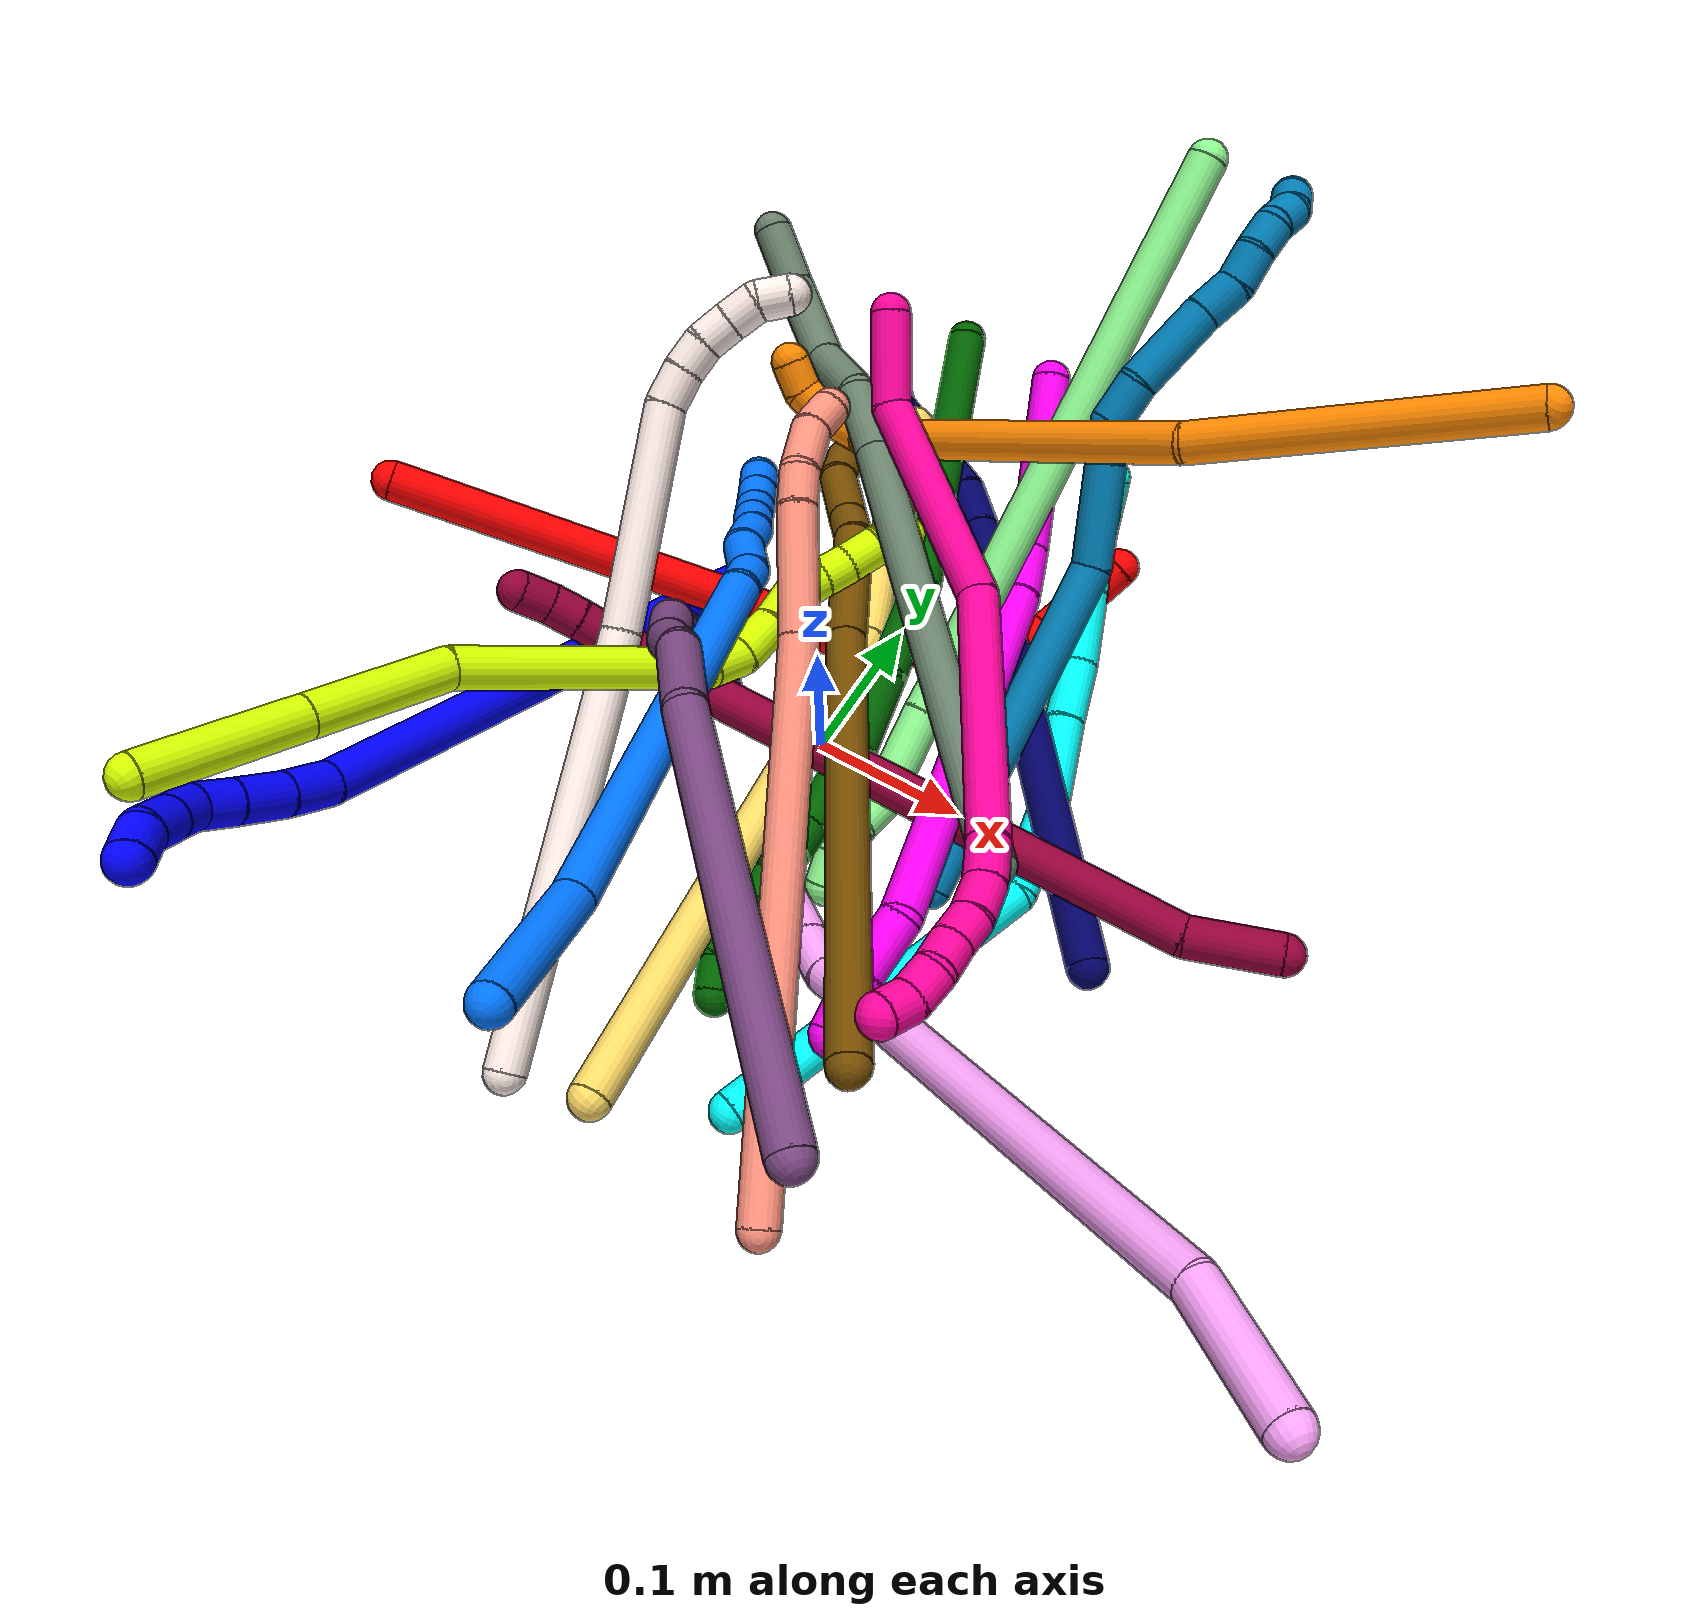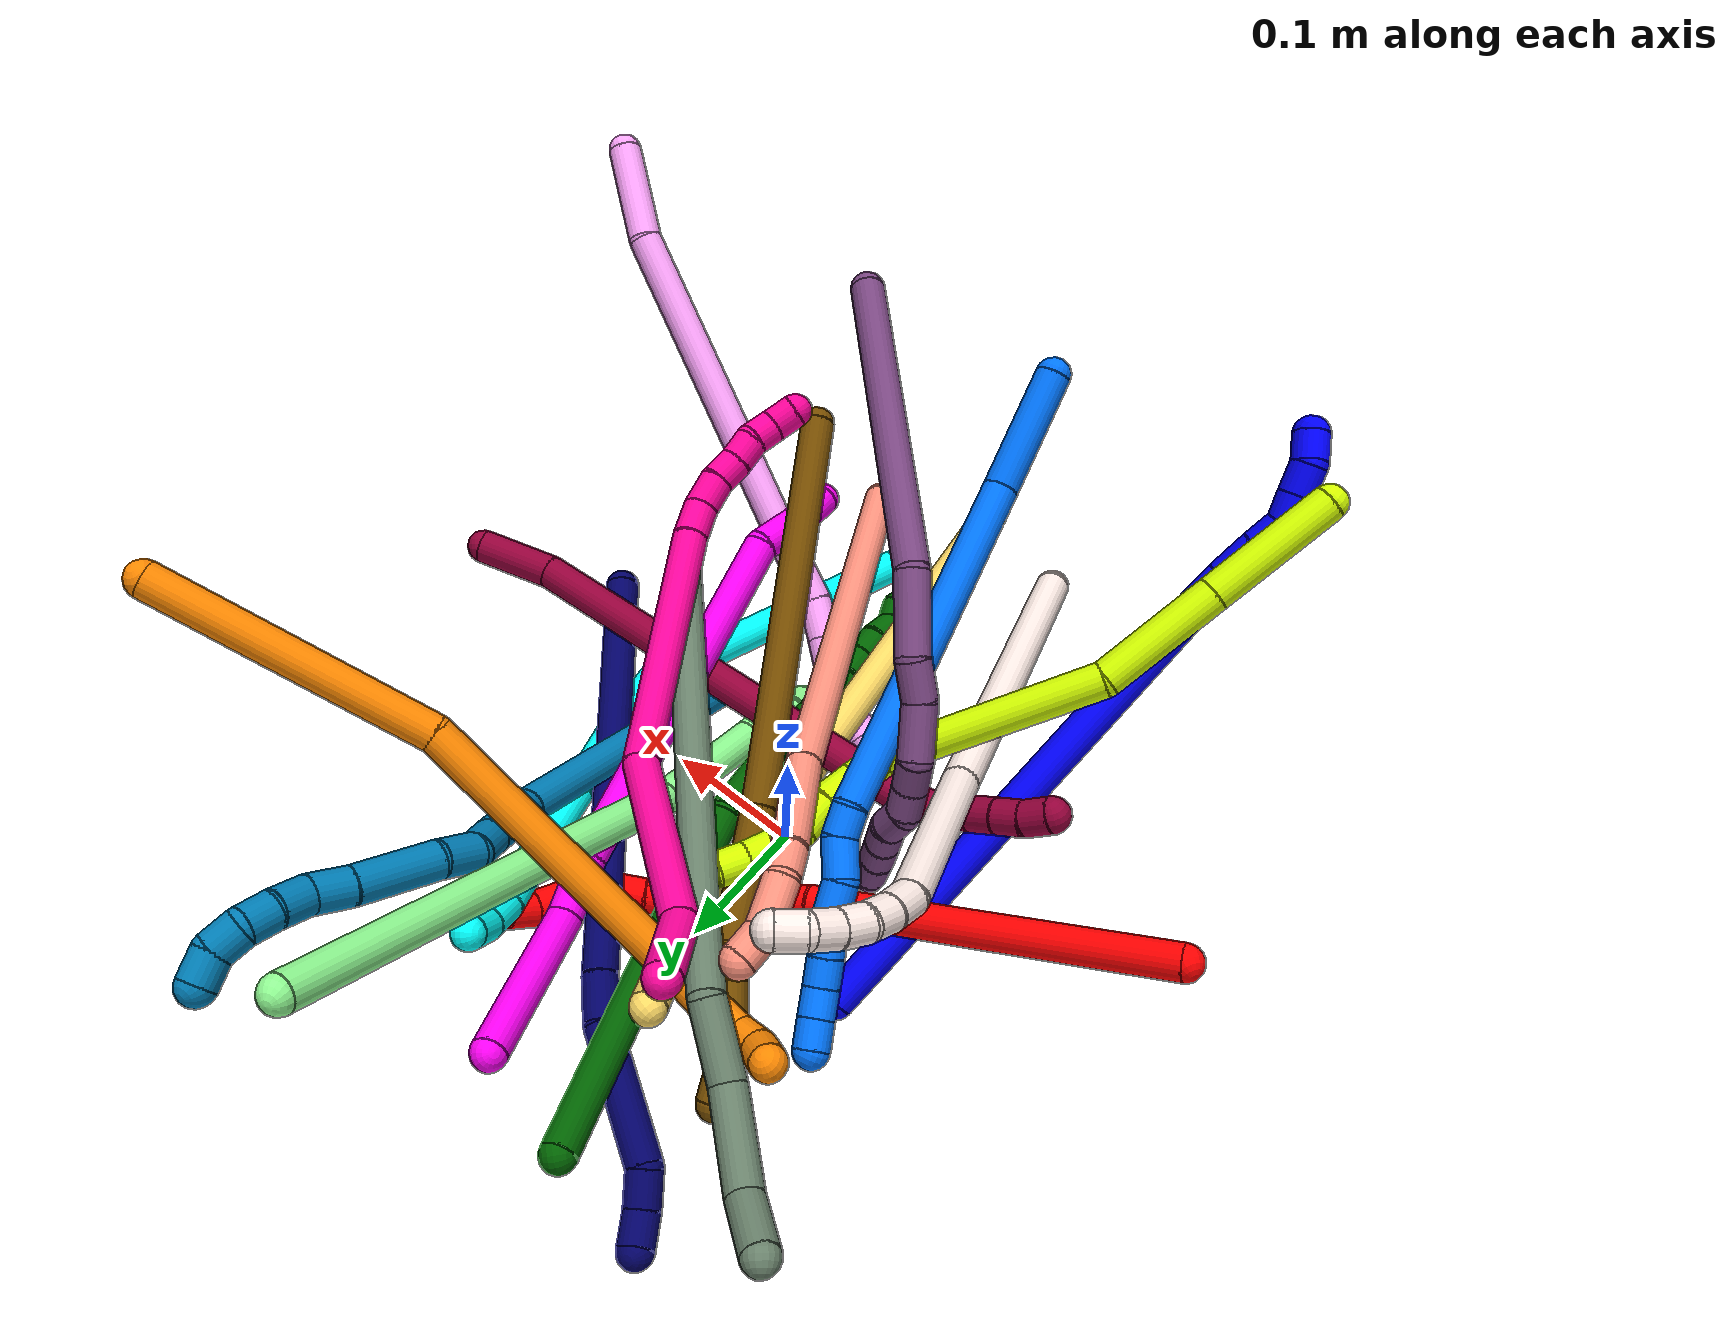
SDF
<sdf version="1.7">
 <world name="default">
  <plugin name="TubeGeneratorPlugin" filename="libtube_generator_plugin.so"/>
  <model name="photoneo_s_sensor">
   <static>1</static>
   <pose>0 0 2 1.57079 1.57079 3.14159</pose>
   <link name="link">
    <inertial><mass>0.1</mass></inertial>
    <sensor name="sensor" type="depth">
     <update_rate>30</update_rate>
     <camera>
      <horizontal_fov>1.22</horizontal_fov>
      <image><width>1920</width><height>1200</height><format>B8G8R8</format></image>
      <clip><near>0.1</near><far>4</far></clip>
      <depth_camera><output>points</output></depth_camera>
     </camera>
     <plugin name="camera_plugin" filename="libgazebo_ros_depth_camera.so">
      <baseline>0.2</baseline>
      <alwaysOn>1</alwaysOn>
      <updateRate>0.0</updateRate>
      <cameraName>camera_ir</cameraName>
      <imageTopicName>/camera/color/image_raw</imageTopicName>
      <cameraInfoTopicName>/camera/color/camera_info</cameraInfoTopicName>
      <depthImageTopicName>/camera/depth/image_raw</depthImageTopicName>
      <depthImageCameraInfoTopicName>/camera/depth/camera_info</depthImageCameraInfoTopicName>
      <pointCloudTopicName>/camera/depth/points</pointCloudTopicName>
      <frameName>fr_optical</frameName>
      <pointCloudCutoff>0.1</pointCloudCutoff>
      <pointCloudCutoffMax>2.0</pointCloudCutoffMax>
      <distortionK1>0</distortionK1>
      <distortionK2>0</distortionK2>
      <distortionK3>0</distortionK3>
      <distortionT1>0</distortionT1>
      <distortionT2>0</distortionT2>
      <CxPrime>0</CxPrime>
      <Cx>0</Cx>
      <Cy>0</Cy>
      <focalLength>0</focalLength>
      <hackBaseline>0</hackBaseline>
     </plugin>
    </sensor>
   </link>
  </model>
  <gravity>0 0 -9.8</gravity>
  <magnetic_field>6e-06 2.3e-05 -4.2e-05</magnetic_field>
  <atmosphere type="adiabatic"/>
  <physics name="default_physics" default="0" type="ode">
   <max_step_size>0.003</max_step_size>
   <real_time_factor>1</real_time_factor>
   <real_time_update_rate>1000</real_time_update_rate>
   <max_contacts>10000</max_contacts>
   <ode>
    <solver>
     <type>quick</type>
     <iters>100</iters>
     <sor>1.3</sor>
     <use_dynamic_moi_rescaling>0</use_dynamic_moi_rescaling>
    </solver>
    <constraints>
     <contact_max_correcting_vel>0</contact_max_correcting_vel>
     <contact_surface_layer>0.001</contact_surface_layer>
     <cfm>0</cfm>
     <erp>0.2</erp>
    </constraints>
   </ode>
  </physics>
  <scene><ambient>0.4 0.4 0.4 1</ambient><background>0.7 0.7 0.7 1</background><shadows>0</shadows></scene>
  <audio><device>default</device></audio>
  <spherical_coordinates>
   <surface_model>EARTH_WGS84</surface_model>
   <latitude_deg>0</latitude_deg>
   <longitude_deg>0</longitude_deg>
   <elevation>0</elevation>
   <heading_deg>0</heading_deg>
  </spherical_coordinates>
  <model name="bin">
   <static>1</static>
   <link name="bottom">
    <collision name="collision-bottom">
     <pose>0 0 -0.01 0 -0 0</pose>
     <geometry><box><size>0.8 0.6 0.02</size></box></geometry>
     <surface>
      <friction><ode><mu>100</mu><mu2>100</mu2></ode></friction>
      <contact><collide_bitmask>65535</collide_bitmask></contact>
     </surface>
    </collision>
   </link>
   <link name="west_wall">
    <collision name="collision-west_wall">
     <pose>-0.41 0 0.1 0 -0 0</pose>
     <geometry><box><size>0.02 0.6 0.2</size></box></geometry>
     <surface>
      <friction><ode><mu>100</mu><mu2>100</mu2></ode></friction>
      <contact><collide_bitmask>65535</collide_bitmask></contact>
     </surface>
    </collision>
   </link>
   <link name="east_wall">
    <collision name="collision-east_wall">
     <pose>0.41 0 0.1 0 -0 0</pose>
     <geometry><box><size>0.02 0.6 0.2</size></box></geometry>
     <surface>
      <friction><ode><mu>100</mu><mu2>100</mu2></ode></friction>
      <contact><collide_bitmask>65535</collide_bitmask></contact>
     </surface>
    </collision>
   </link>
   <link name="south_wall">
    <collision name="collision-south_wall">
     <pose>0 -0.31 0.1 0 -0 0</pose>
     <geometry><box><size>0.8 0.02 0.2</size></box></geometry>
     <surface>
      <friction><ode><mu>100</mu><mu2>100</mu2></ode></friction>
      <contact><collide_bitmask>65535</collide_bitmask></contact>
     </surface>
    </collision>
   </link>
   <link name="north_wall">
    <collision name="collision-north_wall">
     <pose>0 0.31 0.1 0 -0 0</pose>
     <geometry><box><size>0.8 0.02 0.2</size></box></geometry>
     <surface>
      <friction><ode><mu>100</mu><mu2>100</mu2></ode></friction>
      <contact><collide_bitmask>65535</collide_bitmask></contact>
     </surface>
    </collision>
   </link>
  </model>
  <model name="1">
   <static>0</static>
   <link name="1">
    <collision name="collision-cylinder-e_1_1_4">
     <pose>-0.001819 -0.042072 0.172717 0.238934 -0.010231 -0.001228</pose>
     <geometry><cylinder><radius>0.0125</radius><length>0.355554</length></cylinder></geometry>
     <surface>
      <friction><ode><mu>1.16</mu><mu2>1.16</mu2><slip1>0</slip1><slip2>0</slip2></ode></friction>
      <contact><ode><kp>1e+06</kp><kd>1</kd><max_vel>0</max_vel><min_depth>0.001</min_depth></ode></contact>
     </surface>
    </collision>
    <visual name="visual-cylinder-e_1_1_4">
     <pose>-0.001819 -0.042072 0.172717 0.238934 -0.010231 -0.001228</pose>
     <geometry><cylinder><radius>0.0125</radius><length>0.355554</length></cylinder></geometry>
     <material><ambient>0 0 1 1</ambient></material>
    </visual>
    <collision name="collision-cylinder-e_2_4_5">
     <pose>-0.00642 -0.086586 0.35948 0.172169 -0.192775 -0.016687</pose>
     <geometry><cylinder><radius>0.0125</radius><length>0.02905</length></cylinder></geometry>
     <surface>
      <friction><ode><mu>1.16</mu><mu2>1.16</mu2><slip1>0</slip1><slip2>0</slip2></ode></friction>
      <contact><ode><kp>1e+06</kp><kd>1</kd><max_vel>0</max_vel><min_depth>0.001</min_depth></ode></contact>
     </surface>
    </collision>
    <visual name="visual-cylinder-e_2_4_5">
     <pose>-0.00642 -0.086586 0.35948 0.172169 -0.192775 -0.016687</pose>
     <geometry><cylinder><radius>0.0125</radius><length>0.02905</length></cylinder></geometry>
     <material><ambient>0 0 1 1</ambient></material>
    </visual>
    <collision name="collision-cylinder-e_3_5_6">
     <pose>-0.013316 -0.091831 0.387499 0.197934 -0.280907 -0.028075</pose>
     <geometry><cylinder><radius>0.0125</radius><length>0.029668</length></cylinder></geometry>
     <surface>
      <friction><ode><mu>1.16</mu><mu2>1.16</mu2><slip1>0</slip1><slip2>0</slip2></ode></friction>
      <contact><ode><kp>1e+06</kp><kd>1</kd><max_vel>0</max_vel><min_depth>0.001</min_depth></ode></contact>
     </surface>
    </collision>
    <visual name="visual-cylinder-e_3_5_6">
     <pose>-0.013316 -0.091831 0.387499 0.197934 -0.280907 -0.028075</pose>
     <geometry><cylinder><radius>0.0125</radius><length>0.029668</length></cylinder></geometry>
     <material><ambient>0 0 1 1</ambient></material>
    </visual>
    <collision name="collision-cylinder-e_4_6_7">
     <pose>-0.020869 -0.097108 0.411978 0.23137 -0.308626 -0.036147</pose>
     <geometry><cylinder><radius>0.0125</radius><length>0.022655</length></cylinder></geometry>
     <surface>
      <friction><ode><mu>1.16</mu><mu2>1.16</mu2><slip1>0</slip1><slip2>0</slip2></ode></friction>
      <contact><ode><kp>1e+06</kp><kd>1</kd><max_vel>0</max_vel><min_depth>0.001</min_depth></ode></contact>
     </surface>
    </collision>
    <visual name="visual-cylinder-e_4_6_7">
     <pose>-0.020869 -0.097108 0.411978 0.23137 -0.308626 -0.036147</pose>
     <geometry><cylinder><radius>0.0125</radius><length>0.022655</length></cylinder></geometry>
     <material><ambient>0 0 1 1</ambient></material>
    </visual>
    <collision name="collision-cylinder-e_5_7_8">
     <pose>-0.024647 -0.09758 0.432679 -0.193993 -0.032439 0.003157</pose>
     <geometry><cylinder><radius>0.0125</radius><length>0.020794</length></cylinder></geometry>
     <surface>
      <friction><ode><mu>1.16</mu><mu2>1.16</mu2><slip1>0</slip1><slip2>0</slip2></ode></friction>
      <contact><ode><kp>1e+06</kp><kd>1</kd><max_vel>0</max_vel><min_depth>0.001</min_depth></ode></contact>
     </surface>
    </collision>
    <visual name="visual-cylinder-e_5_7_8">
     <pose>-0.024647 -0.09758 0.432679 -0.193993 -0.032439 0.003157</pose>
     <geometry><cylinder><radius>0.0125</radius><length>0.020794</length></cylinder></geometry>
     <material><ambient>0 0 1 1</ambient></material>
    </visual>
    <collision name="collision-cylinder-e_6_8_9">
     <pose>-0.025539 -0.093615 0.453472 -0.183072 -0.051428 0.004722</pose>
     <geometry><cylinder><radius>0.0125</radius><length>0.021581</length></cylinder></geometry>
     <surface>
      <friction><ode><mu>1.16</mu><mu2>1.16</mu2><slip1>0</slip1><slip2>0</slip2></ode></friction>
      <contact><ode><kp>1e+06</kp><kd>1</kd><max_vel>0</max_vel><min_depth>0.001</min_depth></ode></contact>
     </surface>
    </collision>
    <visual name="visual-cylinder-e_6_8_9">
     <pose>-0.025539 -0.093615 0.453472 -0.183072 -0.051428 0.004722</pose>
     <geometry><cylinder><radius>0.0125</radius><length>0.021581</length></cylinder></geometry>
     <material><ambient>0 0 1 1</ambient></material>
    </visual>
    <collision name="collision-cylinder-e_7_9_2">
     <pose>-0.021961 -0.089194 0.473233 -0.262079 0.41069 -0.054887</pose>
     <geometry><cylinder><radius>0.0125</radius><length>0.020698</length></cylinder></geometry>
     <surface>
      <friction><ode><mu>1.16</mu><mu2>1.16</mu2><slip1>0</slip1><slip2>0</slip2></ode></friction>
      <contact><ode><kp>1e+06</kp><kd>1</kd><max_vel>0</max_vel><min_depth>0.001</min_depth></ode></contact>
     </surface>
    </collision>
    <visual name="visual-cylinder-e_7_9_2">
     <pose>-0.021961 -0.089194 0.473233 -0.262079 0.41069 -0.054887</pose>
     <geometry><cylinder><radius>0.0125</radius><length>0.020698</length></cylinder></geometry>
     <material><ambient>0 0 1 1</ambient></material>
    </visual>
    <collision name="collision-sphere-2">
     <pose>-0.01783 -0.086736 0.482398 0 -0 0</pose>
     <geometry><sphere><radius>0.0125</radius></sphere></geometry>
     <surface>
      <friction><ode><mu>1.16</mu><mu2>1.16</mu2><slip1>0</slip1><slip2>0</slip2></ode></friction>
      <contact><ode><kp>1e+06</kp><kd>1</kd><max_vel>0</max_vel><min_depth>0.001</min_depth></ode></contact>
     </surface>
    </collision>
    <visual name="visual-sphere-2">
     <pose>-0.01783 -0.086736 0.482398 0 -0 0</pose>
     <geometry><sphere><radius>0.0125</radius></sphere></geometry>
     <material><ambient>0 0 1 1</ambient></material>
    </visual>
    <collision name="collision-sphere-9">
     <pose>-0.026093 -0.091653 0.464068 0 -0 0</pose>
     <geometry><sphere><radius>0.0125</radius></sphere></geometry>
     <surface>
      <friction><ode><mu>1.16</mu><mu2>1.16</mu2><slip1>0</slip1><slip2>0</slip2></ode></friction>
      <contact><ode><kp>1e+06</kp><kd>1</kd><max_vel>0</max_vel><min_depth>0.001</min_depth></ode></contact>
     </surface>
    </collision>
    <visual name="visual-sphere-9">
     <pose>-0.026093 -0.091653 0.464068 0 -0 0</pose>
     <geometry><sphere><radius>0.0125</radius></sphere></geometry>
     <material><ambient>0 0 1 1</ambient></material>
    </visual>
    <collision name="collision-sphere-4">
     <pose>-0.003638 -0.084143 0.345435 0 -0 0</pose>
     <geometry><sphere><radius>0.0125</radius></sphere></geometry>
     <surface>
      <friction><ode><mu>1.16</mu><mu2>1.16</mu2><slip1>0</slip1><slip2>0</slip2></ode></friction>
      <contact><ode><kp>1e+06</kp><kd>1</kd><max_vel>0</max_vel><min_depth>0.001</min_depth></ode></contact>
     </surface>
    </collision>
    <visual name="visual-sphere-4">
     <pose>-0.003638 -0.084143 0.345435 0 -0 0</pose>
     <geometry><sphere><radius>0.0125</radius></sphere></geometry>
     <material><ambient>0 0 1 1</ambient></material>
    </visual>
    <collision name="collision-sphere-1">
     <geometry><sphere><radius>0.0125</radius></sphere></geometry>
     <surface>
      <friction><ode><mu>1.16</mu><mu2>1.16</mu2><slip1>0</slip1><slip2>0</slip2></ode></friction>
      <contact><ode><kp>1e+06</kp><kd>1</kd><max_vel>0</max_vel><min_depth>0.001</min_depth></ode></contact>
     </surface>
    </collision>
    <visual name="visual-sphere-1">
     <geometry><sphere><radius>0.0125</radius></sphere></geometry>
     <material><ambient>0 0 1 1</ambient></material>
    </visual>
    <collision name="collision-sphere-8">
     <pose>-0.024984 -0.095576 0.442876 0 -0 0</pose>
     <geometry><sphere><radius>0.0125</radius></sphere></geometry>
     <surface>
      <friction><ode><mu>1.16</mu><mu2>1.16</mu2><slip1>0</slip1><slip2>0</slip2></ode></friction>
      <contact><ode><kp>1e+06</kp><kd>1</kd><max_vel>0</max_vel><min_depth>0.001</min_depth></ode></contact>
     </surface>
    </collision>
    <visual name="visual-sphere-8">
     <pose>-0.024984 -0.095576 0.442876 0 -0 0</pose>
     <geometry><sphere><radius>0.0125</radius></sphere></geometry>
     <material><ambient>0 0 1 1</ambient></material>
    </visual>
    <collision name="collision-sphere-5">
     <pose>-0.009203 -0.089028 0.373525 0 -0 0</pose>
     <geometry><sphere><radius>0.0125</radius></sphere></geometry>
     <surface>
      <friction><ode><mu>1.16</mu><mu2>1.16</mu2><slip1>0</slip1><slip2>0</slip2></ode></friction>
      <contact><ode><kp>1e+06</kp><kd>1</kd><max_vel>0</max_vel><min_depth>0.001</min_depth></ode></contact>
     </surface>
    </collision>
    <visual name="visual-sphere-5">
     <pose>-0.009203 -0.089028 0.373525 0 -0 0</pose>
     <geometry><sphere><radius>0.0125</radius></sphere></geometry>
     <material><ambient>0 0 1 1</ambient></material>
    </visual>
    <collision name="collision-sphere-6">
     <pose>-0.017428 -0.094633 0.401474 0 -0 0</pose>
     <geometry><sphere><radius>0.0125</radius></sphere></geometry>
     <surface>
      <friction><ode><mu>1.16</mu><mu2>1.16</mu2><slip1>0</slip1><slip2>0</slip2></ode></friction>
      <contact><ode><kp>1e+06</kp><kd>1</kd><max_vel>0</max_vel><min_depth>0.001</min_depth></ode></contact>
     </surface>
    </collision>
    <visual name="visual-sphere-6">
     <pose>-0.017428 -0.094633 0.401474 0 -0 0</pose>
     <geometry><sphere><radius>0.0125</radius></sphere></geometry>
     <material><ambient>0 0 1 1</ambient></material>
    </visual>
    <collision name="collision-sphere-7">
     <pose>-0.024309 -0.099583 0.422483 0 -0 0</pose>
     <geometry><sphere><radius>0.0125</radius></sphere></geometry>
     <surface>
      <friction><ode><mu>1.16</mu><mu2>1.16</mu2><slip1>0</slip1><slip2>0</slip2></ode></friction>
      <contact><ode><kp>1e+06</kp><kd>1</kd><max_vel>0</max_vel><min_depth>0.001</min_depth></ode></contact>
     </surface>
    </collision>
    <visual name="visual-sphere-7">
     <pose>-0.024309 -0.099583 0.422483 0 -0 0</pose>
     <geometry><sphere><radius>0.0125</radius></sphere></geometry>
     <material><ambient>0 0 1 1</ambient></material>
    </visual>
    <inertial>
     <pose>-0.006438 -0.056588 0.242523 0 -0 0</pose>
     <mass>0.5</mass>
     <inertia>
      <ixx>0.003766</ixx>
      <ixy>0</ixy>
      <ixz>0</ixz>
      <iyy>0.003654</iyy>
      <iyz>0</iyz>
      <izz>0.000968</izz>
     </inertia>
    </inertial>
   </link>
   <pose>-0.109059 0.079149 0.011457 0.741249 0.690955 -0.534343</pose>
  </model>
  <model name="2">
   <static>0</static>
   <link name="2">
    <collision name="collision-cylinder-e_1_1_4">
     <pose>0.085061 0.05128 -0.077461 -2.55682 0.741396 -1.82363</pose>
     <geometry><cylinder><radius>0.0125</radius><length>0.251915</length></cylinder></geometry>
     <surface>
      <friction><ode><mu>1.16</mu><mu2>1.16</mu2><slip1>0</slip1><slip2>0</slip2></ode></friction>
      <contact><ode><kp>1e+06</kp><kd>1</kd><max_vel>0</max_vel><min_depth>0.001</min_depth></ode></contact>
     </surface>
    </collision>
    <visual name="visual-cylinder-e_1_1_4">
     <pose>0.085061 0.05128 -0.077461 -2.55682 0.741396 -1.82363</pose>
     <geometry><cylinder><radius>0.0125</radius><length>0.251915</length></cylinder></geometry>
     <material><ambient>1 0 0 1</ambient></material>
    </visual>
    <collision name="collision-cylinder-e_2_4_5">
     <pose>0.190905 0.120486 -0.173064 -2.36216 0.683736 -1.42784</pose>
     <geometry><cylinder><radius>0.0125</radius><length>0.065799</length></cylinder></geometry>
     <surface>
      <friction><ode><mu>1.16</mu><mu2>1.16</mu2><slip1>0</slip1><slip2>0</slip2></ode></friction>
      <contact><ode><kp>1e+06</kp><kd>1</kd><max_vel>0</max_vel><min_depth>0.001</min_depth></ode></contact>
     </surface>
    </collision>
    <visual name="visual-cylinder-e_2_4_5">
     <pose>0.190905 0.120486 -0.173064 -2.36216 0.683736 -1.42784</pose>
     <geometry><cylinder><radius>0.0125</radius><length>0.065799</length></cylinder></geometry>
     <material><ambient>1 0 0 1</ambient></material>
    </visual>
    <collision name="collision-cylinder-e_3_5_6">
     <pose>0.228065 0.14155 -0.197831 -2.69931 1.14993 -2.47369</pose>
     <geometry><cylinder><radius>0.0125</radius><length>0.035888</length></cylinder></geometry>
     <surface>
      <friction><ode><mu>1.16</mu><mu2>1.16</mu2><slip1>0</slip1><slip2>0</slip2></ode></friction>
      <contact><ode><kp>1e+06</kp><kd>1</kd><max_vel>0</max_vel><min_depth>0.001</min_depth></ode></contact>
     </surface>
    </collision>
    <visual name="visual-cylinder-e_3_5_6">
     <pose>0.228065 0.14155 -0.197831 -2.69931 1.14993 -2.47369</pose>
     <geometry><cylinder><radius>0.0125</radius><length>0.035888</length></cylinder></geometry>
     <material><ambient>1 0 0 1</ambient></material>
    </visual>
    <collision name="collision-cylinder-e_4_6_7">
     <pose>0.255213 0.145419 -0.208829 -2.97593 1.18025 -2.89493</pose>
     <geometry><cylinder><radius>0.0125</radius><length>0.023294</length></cylinder></geometry>
     <surface>
      <friction><ode><mu>1.16</mu><mu2>1.16</mu2><slip1>0</slip1><slip2>0</slip2></ode></friction>
      <contact><ode><kp>1e+06</kp><kd>1</kd><max_vel>0</max_vel><min_depth>0.001</min_depth></ode></contact>
     </surface>
    </collision>
    <visual name="visual-cylinder-e_4_6_7">
     <pose>0.255213 0.145419 -0.208829 -2.97593 1.18025 -2.89493</pose>
     <geometry><cylinder><radius>0.0125</radius><length>0.023294</length></cylinder></geometry>
     <material><ambient>1 0 0 1</ambient></material>
    </visual>
    <collision name="collision-cylinder-e_5_7_8">
     <pose>0.277523 0.14735 -0.219754 -2.96047 1.04735 -2.82962</pose>
     <geometry><cylinder><radius>0.0125</radius><length>0.026648</length></cylinder></geometry>
     <surface>
      <friction><ode><mu>1.16</mu><mu2>1.16</mu2><slip1>0</slip1><slip2>0</slip2></ode></friction>
      <contact><ode><kp>1e+06</kp><kd>1</kd><max_vel>0</max_vel><min_depth>0.001</min_depth></ode></contact>
     </surface>
    </collision>
    <visual name="visual-cylinder-e_5_7_8">
     <pose>0.277523 0.14735 -0.219754 -2.96047 1.04735 -2.82962</pose>
     <geometry><cylinder><radius>0.0125</radius><length>0.026648</length></cylinder></geometry>
     <material><ambient>1 0 0 1</ambient></material>
    </visual>
    <collision name="collision-cylinder-e_6_8_9">
     <pose>0.303253 0.153055 -0.229017 -2.11249 1.21592 -1.77706</pose>
     <geometry><cylinder><radius>0.0125</radius><length>0.030265</length></cylinder></geometry>
     <surface>
      <friction><ode><mu>1.16</mu><mu2>1.16</mu2><slip1>0</slip1><slip2>0</slip2></ode></friction>
      <contact><ode><kp>1e+06</kp><kd>1</kd><max_vel>0</max_vel><min_depth>0.001</min_depth></ode></contact>
     </surface>
    </collision>
    <visual name="visual-cylinder-e_6_8_9">
     <pose>0.303253 0.153055 -0.229017 -2.11249 1.21592 -1.77706</pose>
     <geometry><cylinder><radius>0.0125</radius><length>0.030265</length></cylinder></geometry>
     <material><ambient>1 0 0 1</ambient></material>
    </visual>
    <collision name="collision-cylinder-e_7_9_10">
     <pose>0.329427 0.157215 -0.229335 0.143412 1.37171 0.117433</pose>
     <geometry><cylinder><radius>0.0125</radius><length>0.024452</length></cylinder></geometry>
     <surface>
      <friction><ode><mu>1.16</mu><mu2>1.16</mu2><slip1>0</slip1><slip2>0</slip2></ode></friction>
      <contact><ode><kp>1e+06</kp><kd>1</kd><max_vel>0</max_vel><min_depth>0.001</min_depth></ode></contact>
     </surface>
    </collision>
    <visual name="visual-cylinder-e_7_9_10">
     <pose>0.329427 0.157215 -0.229335 0.143412 1.37171 0.117433</pose>
     <geometry><cylinder><radius>0.0125</radius><length>0.024452</length></cylinder></geometry>
     <material><ambient>1 0 0 1</ambient></material>
    </visual>
    <collision name="collision-cylinder-e_8_10_11">
     <pose>0.351464 0.153709 -0.226044 1.29401 1.25494 1.00249</pose>
     <geometry><cylinder><radius>0.0125</radius><length>0.021151</length></cylinder></geometry>
     <surface>
      <friction><ode><mu>1.16</mu><mu2>1.16</mu2><slip1>0</slip1><slip2>0</slip2></ode></friction>
      <contact><ode><kp>1e+06</kp><kd>1</kd><max_vel>0</max_vel><min_depth>0.001</min_depth></ode></contact>
     </surface>
    </collision>
    <visual name="visual-cylinder-e_8_10_11">
     <pose>0.351464 0.153709 -0.226044 1.29401 1.25494 1.00249</pose>
     <geometry><cylinder><radius>0.0125</radius><length>0.021151</length></cylinder></geometry>
     <material><ambient>1 0 0 1</ambient></material>
    </visual>
    <collision name="collision-cylinder-e_9_11_2">
     <pose>0.371326 0.147684 -0.223915 1.16514 1.26298 0.898098</pose>
     <geometry><cylinder><radius>0.0125</radius><length>0.020589</length></cylinder></geometry>
     <surface>
      <friction><ode><mu>1.16</mu><mu2>1.16</mu2><slip1>0</slip1><slip2>0</slip2></ode></friction>
      <contact><ode><kp>1e+06</kp><kd>1</kd><max_vel>0</max_vel><min_depth>0.001</min_depth></ode></contact>
     </surface>
    </collision>
    <visual name="visual-cylinder-e_9_11_2">
     <pose>0.371326 0.147684 -0.223915 1.16514 1.26298 0.898098</pose>
     <geometry><cylinder><radius>0.0125</radius><length>0.020589</length></cylinder></geometry>
     <material><ambient>1 0 0 1</ambient></material>
    </visual>
    <collision name="collision-sphere-2">
     <pose>0.381137 0.144818 -0.222685 0 -0 0</pose>
     <geometry><sphere><radius>0.0125</radius></sphere></geometry>
     <surface>
      <friction><ode><mu>1.16</mu><mu2>1.16</mu2><slip1>0</slip1><slip2>0</slip2></ode></friction>
      <contact><ode><kp>1e+06</kp><kd>1</kd><max_vel>0</max_vel><min_depth>0.001</min_depth></ode></contact>
     </surface>
    </collision>
    <visual name="visual-sphere-2">
     <pose>0.381137 0.144818 -0.222685 0 -0 0</pose>
     <geometry><sphere><radius>0.0125</radius></sphere></geometry>
     <material><ambient>1 0 0 1</ambient></material>
    </visual>
    <collision name="collision-sphere-11">
     <pose>0.361516 0.150549 -0.225146 0 -0 0</pose>
     <geometry><sphere><radius>0.0125</radius></sphere></geometry>
     <surface>
      <friction><ode><mu>1.16</mu><mu2>1.16</mu2><slip1>0</slip1><slip2>0</slip2></ode></friction>
      <contact><ode><kp>1e+06</kp><kd>1</kd><max_vel>0</max_vel><min_depth>0.001</min_depth></ode></contact>
     </surface>
    </collision>
    <visual name="visual-sphere-11">
     <pose>0.361516 0.150549 -0.225146 0 -0 0</pose>
     <geometry><sphere><radius>0.0125</radius></sphere></geometry>
     <material><ambient>1 0 0 1</ambient></material>
    </visual>
    <collision name="collision-sphere-10">
     <pose>0.341411 0.156869 -0.226941 0 -0 0</pose>
     <geometry><sphere><radius>0.0125</radius></sphere></geometry>
     <surface>
      <friction><ode><mu>1.16</mu><mu2>1.16</mu2><slip1>0</slip1><slip2>0</slip2></ode></friction>
      <contact><ode><kp>1e+06</kp><kd>1</kd><max_vel>0</max_vel><min_depth>0.001</min_depth></ode></contact>
     </surface>
    </collision>
    <visual name="visual-sphere-10">
     <pose>0.341411 0.156869 -0.226941 0 -0 0</pose>
     <geometry><sphere><radius>0.0125</radius></sphere></geometry>
     <material><ambient>1 0 0 1</ambient></material>
    </visual>
    <collision name="collision-sphere-9">
     <pose>0.317443 0.157561 -0.231728 0 -0 0</pose>
     <geometry><sphere><radius>0.0125</radius></sphere></geometry>
     <surface>
      <friction><ode><mu>1.16</mu><mu2>1.16</mu2><slip1>0</slip1><slip2>0</slip2></ode></friction>
      <contact><ode><kp>1e+06</kp><kd>1</kd><max_vel>0</max_vel><min_depth>0.001</min_depth></ode></contact>
     </surface>
    </collision>
    <visual name="visual-sphere-9">
     <pose>0.317443 0.157561 -0.231728 0 -0 0</pose>
     <geometry><sphere><radius>0.0125</radius></sphere></geometry>
     <material><ambient>1 0 0 1</ambient></material>
    </visual>
    <collision name="collision-sphere-4">
     <pose>0.170123 0.10256 -0.154922 0 -0 0</pose>
     <geometry><sphere><radius>0.0125</radius></sphere></geometry>
     <surface>
      <friction><ode><mu>1.16</mu><mu2>1.16</mu2><slip1>0</slip1><slip2>0</slip2></ode></friction>
      <contact><ode><kp>1e+06</kp><kd>1</kd><max_vel>0</max_vel><min_depth>0.001</min_depth></ode></contact>
     </surface>
    </collision>
    <visual name="visual-sphere-4">
     <pose>0.170123 0.10256 -0.154922 0 -0 0</pose>
     <geometry><sphere><radius>0.0125</radius></sphere></geometry>
     <material><ambient>1 0 0 1</ambient></material>
    </visual>
    <collision name="collision-sphere-1">
     <geometry><sphere><radius>0.0125</radius></sphere></geometry>
     <surface>
      <friction><ode><mu>1.16</mu><mu2>1.16</mu2><slip1>0</slip1><slip2>0</slip2></ode></friction>
      <contact><ode><kp>1e+06</kp><kd>1</kd><max_vel>0</max_vel><min_depth>0.001</min_depth></ode></contact>
     </surface>
    </collision>
    <visual name="visual-sphere-1">
     <geometry><sphere><radius>0.0125</radius></sphere></geometry>
     <material><ambient>1 0 0 1</ambient></material>
    </visual>
    <collision name="collision-sphere-8">
     <pose>0.289063 0.14855 -0.226306 0 -0 0</pose>
     <geometry><sphere><radius>0.0125</radius></sphere></geometry>
     <surface>
      <friction><ode><mu>1.16</mu><mu2>1.16</mu2><slip1>0</slip1><slip2>0</slip2></ode></friction>
      <contact><ode><kp>1e+06</kp><kd>1</kd><max_vel>0</max_vel><min_depth>0.001</min_depth></ode></contact>
     </surface>
    </collision>
    <visual name="visual-sphere-8">
     <pose>0.289063 0.14855 -0.226306 0 -0 0</pose>
     <geometry><sphere><radius>0.0125</radius></sphere></geometry>
     <material><ambient>1 0 0 1</ambient></material>
    </visual>
    <collision name="collision-sphere-5">
     <pose>0.211688 0.138412 -0.191205 0 -0 0</pose>
     <geometry><sphere><radius>0.0125</radius></sphere></geometry>
     <surface>
      <friction><ode><mu>1.16</mu><mu2>1.16</mu2><slip1>0</slip1><slip2>0</slip2></ode></friction>
      <contact><ode><kp>1e+06</kp><kd>1</kd><max_vel>0</max_vel><min_depth>0.001</min_depth></ode></contact>
     </surface>
    </collision>
    <visual name="visual-sphere-5">
     <pose>0.211688 0.138412 -0.191205 0 -0 0</pose>
     <geometry><sphere><radius>0.0125</radius></sphere></geometry>
     <material><ambient>1 0 0 1</ambient></material>
    </visual>
    <collision name="collision-sphere-6">
     <pose>0.244443 0.144688 -0.204456 0 -0 0</pose>
     <geometry><sphere><radius>0.0125</radius></sphere></geometry>
     <surface>
      <friction><ode><mu>1.16</mu><mu2>1.16</mu2><slip1>0</slip1><slip2>0</slip2></ode></friction>
      <contact><ode><kp>1e+06</kp><kd>1</kd><max_vel>0</max_vel><min_depth>0.001</min_depth></ode></contact>
     </surface>
    </collision>
    <visual name="visual-sphere-6">
     <pose>0.244443 0.144688 -0.204456 0 -0 0</pose>
     <geometry><sphere><radius>0.0125</radius></sphere></geometry>
     <material><ambient>1 0 0 1</ambient></material>
    </visual>
    <collision name="collision-sphere-7">
     <pose>0.265983 0.14615 -0.213203 0 -0 0</pose>
     <geometry><sphere><radius>0.0125</radius></sphere></geometry>
     <surface>
      <friction><ode><mu>1.16</mu><mu2>1.16</mu2><slip1>0</slip1><slip2>0</slip2></ode></friction>
      <contact><ode><kp>1e+06</kp><kd>1</kd><max_vel>0</max_vel><min_depth>0.001</min_depth></ode></contact>
     </surface>
    </collision>
    <visual name="visual-sphere-7">
     <pose>0.265983 0.14615 -0.213203 0 -0 0</pose>
     <geometry><sphere><radius>0.0125</radius></sphere></geometry>
     <material><ambient>1 0 0 1</ambient></material>
    </visual>
    <inertial>
     <pose>0.175653 0.096016 -0.141302 0 -0 0</pose>
     <mass>0.5</mass>
     <inertia>
      <ixx>-0.001199</ixx>
      <ixy>0</ixy>
      <ixz>0</ixz>
      <iyy>-0.000179</iyy>
      <iyz>0</iyz>
      <izz>-0.00152</izz>
     </inertia>
    </inertial>
   </link>
   <pose>-0.282909 -0.037702 0.125792 -1.47473 -0.194386 1.01135</pose>
  </model>
  <model name="3">
   <static>0</static>
   <link name="3">
    <collision name="collision-cylinder-e_1_1_4">
     <pose>-0.025454 0.084333 -0.061261 -2.19903 -0.239508 0.463776</pose>
     <geometry><cylinder><radius>0.0125</radius><length>0.214596</length></cylinder></geometry>
     <surface>
      <friction><ode><mu>1.16</mu><mu2>1.16</mu2><slip1>0</slip1><slip2>0</slip2></ode></friction>
      <contact><ode><kp>1e+06</kp><kd>1</kd><max_vel>0</max_vel><min_depth>0.001</min_depth></ode></contact>
     </surface>
    </collision>
    <visual name="visual-cylinder-e_1_1_4">
     <pose>-0.025454 0.084333 -0.061261 -2.19903 -0.239508 0.463776</pose>
     <geometry><cylinder><radius>0.0125</radius><length>0.214596</length></cylinder></geometry>
     <material><ambient>0.003922 1 0.996078 1</ambient></material>
    </visual>
    <collision name="collision-cylinder-e_2_4_5">
     <pose>-0.066617 0.192929 -0.127268 -1.76397 -0.566087 0.679149</pose>
     <geometry><cylinder><radius>0.0125</radius><length>0.058582</length></cylinder></geometry>
     <surface>
      <friction><ode><mu>1.16</mu><mu2>1.16</mu2><slip1>0</slip1><slip2>0</slip2></ode></friction>
      <contact><ode><kp>1e+06</kp><kd>1</kd><max_vel>0</max_vel><min_depth>0.001</min_depth></ode></contact>
     </surface>
    </collision>
    <visual name="visual-cylinder-e_2_4_5">
     <pose>-0.066617 0.192929 -0.127268 -1.76397 -0.566087 0.679149</pose>
     <geometry><cylinder><radius>0.0125</radius><length>0.058582</length></cylinder></geometry>
     <material><ambient>0.003922 1 0.996078 1</ambient></material>
    </visual>
    <collision name="collision-cylinder-e_3_5_6">
     <pose>-0.09705 0.243768 -0.130259 -1.50488 -0.504968 0.473962</pose>
     <geometry><cylinder><radius>0.0125</radius><length>0.060869</length></cylinder></geometry>
     <surface>
      <friction><ode><mu>1.16</mu><mu2>1.16</mu2><slip1>0</slip1><slip2>0</slip2></ode></friction>
      <contact><ode><kp>1e+06</kp><kd>1</kd><max_vel>0</max_vel><min_depth>0.001</min_depth></ode></contact>
     </surface>
    </collision>
    <visual name="visual-cylinder-e_3_5_6">
     <pose>-0.09705 0.243768 -0.130259 -1.50488 -0.504968 0.473962</pose>
     <geometry><cylinder><radius>0.0125</radius><length>0.060869</length></cylinder></geometry>
     <material><ambient>0.003922 1 0.996078 1</ambient></material>
    </visual>
    <collision name="collision-cylinder-e_4_6_7">
     <pose>-0.122517 0.28785 -0.128881 -1.59234 -0.550382 0.561754</pose>
     <geometry><cylinder><radius>0.0125</radius><length>0.041083</length></cylinder></geometry>
     <surface>
      <friction><ode><mu>1.16</mu><mu2>1.16</mu2><slip1>0</slip1><slip2>0</slip2></ode></friction>
      <contact><ode><kp>1e+06</kp><kd>1</kd><max_vel>0</max_vel><min_depth>0.001</min_depth></ode></contact>
     </surface>
    </collision>
    <visual name="visual-cylinder-e_4_6_7">
     <pose>-0.122517 0.28785 -0.128881 -1.59234 -0.550382 0.561754</pose>
     <geometry><cylinder><radius>0.0125</radius><length>0.041083</length></cylinder></geometry>
     <material><ambient>0.003922 1 0.996078 1</ambient></material>
    </visual>
    <collision name="collision-cylinder-e_5_7_8">
     <pose>-0.142411 0.327272 -0.125447 -1.39861 -0.390216 0.32943</pose>
     <geometry><cylinder><radius>0.0125</radius><length>0.04811</length></cylinder></geometry>
     <surface>
      <friction><ode><mu>1.16</mu><mu2>1.16</mu2><slip1>0</slip1><slip2>0</slip2></ode></friction>
      <contact><ode><kp>1e+06</kp><kd>1</kd><max_vel>0</max_vel><min_depth>0.001</min_depth></ode></contact>
     </surface>
    </collision>
    <visual name="visual-cylinder-e_5_7_8">
     <pose>-0.142411 0.327272 -0.125447 -1.39861 -0.390216 0.32943</pose>
     <geometry><cylinder><radius>0.0125</radius><length>0.04811</length></cylinder></geometry>
     <material><ambient>0.003922 1 0.996078 1</ambient></material>
    </visual>
    <collision name="collision-cylinder-e_6_8_9">
     <pose>-0.156645 0.360491 -0.119346 -1.37092 -0.415258 0.341187</pose>
     <geometry><cylinder><radius>0.0125</radius><length>0.025205</length></cylinder></geometry>
     <surface>
      <friction><ode><mu>1.16</mu><mu2>1.16</mu2><slip1>0</slip1><slip2>0</slip2></ode></friction>
      <contact><ode><kp>1e+06</kp><kd>1</kd><max_vel>0</max_vel><min_depth>0.001</min_depth></ode></contact>
     </surface>
    </collision>
    <visual name="visual-cylinder-e_6_8_9">
     <pose>-0.156645 0.360491 -0.119346 -1.37092 -0.415258 0.341187</pose>
     <geometry><cylinder><radius>0.0125</radius><length>0.025205</length></cylinder></geometry>
     <material><ambient>0.003922 1 0.996078 1</ambient></material>
    </visual>
    <collision name="collision-cylinder-e_7_9_10">
     <pose>-0.163943 0.384673 -0.114685 -1.38871 -0.167458 0.13954</pose>
     <geometry><cylinder><radius>0.0125</radius><length>0.026564</length></cylinder></geometry>
     <surface>
      <friction><ode><mu>1.16</mu><mu2>1.16</mu2><slip1>0</slip1><slip2>0</slip2></ode></friction>
      <contact><ode><kp>1e+06</kp><kd>1</kd><max_vel>0</max_vel><min_depth>0.001</min_depth></ode></contact>
     </surface>
    </collision>
    <visual name="visual-cylinder-e_7_9_10">
     <pose>-0.163943 0.384673 -0.114685 -1.38871 -0.167458 0.13954</pose>
     <geometry><cylinder><radius>0.0125</radius><length>0.026564</length></cylinder></geometry>
     <material><ambient>0.003922 1 0.996078 1</ambient></material>
    </visual>
    <collision name="collision-cylinder-e_8_10_2">
     <pose>-0.164923 0.409449 -0.108696 -1.27562 0.098921 -0.073341</pose>
     <geometry><cylinder><radius>0.0125</radius><length>0.024992</length></cylinder></geometry>
     <surface>
      <friction><ode><mu>1.16</mu><mu2>1.16</mu2><slip1>0</slip1><slip2>0</slip2></ode></friction>
      <contact><ode><kp>1e+06</kp><kd>1</kd><max_vel>0</max_vel><min_depth>0.001</min_depth></ode></contact>
     </surface>
    </collision>
    <visual name="visual-cylinder-e_8_10_2">
     <pose>-0.164923 0.409449 -0.108696 -1.27562 0.098921 -0.073341</pose>
     <geometry><cylinder><radius>0.0125</radius><length>0.024992</length></cylinder></geometry>
     <material><ambient>0.003922 1 0.996078 1</ambient></material>
    </visual>
    <collision name="collision-sphere-2">
     <pose>-0.163689 0.421346 -0.105079 0 -0 0</pose>
     <geometry><sphere><radius>0.0125</radius></sphere></geometry>
     <surface>
      <friction><ode><mu>1.16</mu><mu2>1.16</mu2><slip1>0</slip1><slip2>0</slip2></ode></friction>
      <contact><ode><kp>1e+06</kp><kd>1</kd><max_vel>0</max_vel><min_depth>0.001</min_depth></ode></contact>
     </surface>
    </collision>
    <visual name="visual-sphere-2">
     <pose>-0.163689 0.421346 -0.105079 0 -0 0</pose>
     <geometry><sphere><radius>0.0125</radius></sphere></geometry>
     <material><ambient>0.003922 1 0.996078 1</ambient></material>
    </visual>
    <collision name="collision-sphere-10">
     <pose>-0.166157 0.397552 -0.112314 0 -0 0</pose>
     <geometry><sphere><radius>0.0125</radius></sphere></geometry>
     <surface>
      <friction><ode><mu>1.16</mu><mu2>1.16</mu2><slip1>0</slip1><slip2>0</slip2></ode></friction>
      <contact><ode><kp>1e+06</kp><kd>1</kd><max_vel>0</max_vel><min_depth>0.001</min_depth></ode></contact>
     </surface>
    </collision>
    <visual name="visual-sphere-10">
     <pose>-0.166157 0.397552 -0.112314 0 -0 0</pose>
     <geometry><sphere><radius>0.0125</radius></sphere></geometry>
     <material><ambient>0.003922 1 0.996078 1</ambient></material>
    </visual>
    <collision name="collision-sphere-9">
     <pose>-0.161729 0.371793 -0.117057 0 -0 0</pose>
     <geometry><sphere><radius>0.0125</radius></sphere></geometry>
     <surface>
      <friction><ode><mu>1.16</mu><mu2>1.16</mu2><slip1>0</slip1><slip2>0</slip2></ode></friction>
      <contact><ode><kp>1e+06</kp><kd>1</kd><max_vel>0</max_vel><min_depth>0.001</min_depth></ode></contact>
     </surface>
    </collision>
    <visual name="visual-sphere-9">
     <pose>-0.161729 0.371793 -0.117057 0 -0 0</pose>
     <geometry><sphere><radius>0.0125</radius></sphere></geometry>
     <material><ambient>0.003922 1 0.996078 1</ambient></material>
    </visual>
    <collision name="collision-sphere-4">
     <pose>-0.050908 0.168667 -0.122522 0 -0 0</pose>
     <geometry><sphere><radius>0.0125</radius></sphere></geometry>
     <surface>
      <friction><ode><mu>1.16</mu><mu2>1.16</mu2><slip1>0</slip1><slip2>0</slip2></ode></friction>
      <contact><ode><kp>1e+06</kp><kd>1</kd><max_vel>0</max_vel><min_depth>0.001</min_depth></ode></contact>
     </surface>
    </collision>
    <visual name="visual-sphere-4">
     <pose>-0.050908 0.168667 -0.122522 0 -0 0</pose>
     <geometry><sphere><radius>0.0125</radius></sphere></geometry>
     <material><ambient>0.003922 1 0.996078 1</ambient></material>
    </visual>
    <collision name="collision-sphere-1">
     <geometry><sphere><radius>0.0125</radius></sphere></geometry>
     <surface>
      <friction><ode><mu>1.16</mu><mu2>1.16</mu2><slip1>0</slip1><slip2>0</slip2></ode></friction>
      <contact><ode><kp>1e+06</kp><kd>1</kd><max_vel>0</max_vel><min_depth>0.001</min_depth></ode></contact>
     </surface>
    </collision>
    <visual name="visual-sphere-1">
     <geometry><sphere><radius>0.0125</radius></sphere></geometry>
     <material><ambient>0.003922 1 0.996078 1</ambient></material>
    </visual>
    <collision name="collision-sphere-8">
     <pose>-0.151561 0.349189 -0.121636 0 -0 0</pose>
     <geometry><sphere><radius>0.0125</radius></sphere></geometry>
     <surface>
      <friction><ode><mu>1.16</mu><mu2>1.16</mu2><slip1>0</slip1><slip2>0</slip2></ode></friction>
      <contact><ode><kp>1e+06</kp><kd>1</kd><max_vel>0</max_vel><min_depth>0.001</min_depth></ode></contact>
     </surface>
    </collision>
    <visual name="visual-sphere-8">
     <pose>-0.151561 0.349189 -0.121636 0 -0 0</pose>
     <geometry><sphere><radius>0.0125</radius></sphere></geometry>
     <material><ambient>0.003922 1 0.996078 1</ambient></material>
    </visual>
    <collision name="collision-sphere-5">
     <pose>-0.082327 0.21719 -0.132014 0 -0 0</pose>
     <geometry><sphere><radius>0.0125</radius></sphere></geometry>
     <surface>
      <friction><ode><mu>1.16</mu><mu2>1.16</mu2><slip1>0</slip1><slip2>0</slip2></ode></friction>
      <contact><ode><kp>1e+06</kp><kd>1</kd><max_vel>0</max_vel><min_depth>0.001</min_depth></ode></contact>
     </surface>
    </collision>
    <visual name="visual-sphere-5">
     <pose>-0.082327 0.21719 -0.132014 0 -0 0</pose>
     <geometry><sphere><radius>0.0125</radius></sphere></geometry>
     <material><ambient>0.003922 1 0.996078 1</ambient></material>
    </visual>
    <collision name="collision-sphere-6">
     <pose>-0.111774 0.270346 -0.128504 0 -0 0</pose>
     <geometry><sphere><radius>0.0125</radius></sphere></geometry>
     <surface>
      <friction><ode><mu>1.16</mu><mu2>1.16</mu2><slip1>0</slip1><slip2>0</slip2></ode></friction>
      <contact><ode><kp>1e+06</kp><kd>1</kd><max_vel>0</max_vel><min_depth>0.001</min_depth></ode></contact>
     </surface>
    </collision>
    <visual name="visual-sphere-6">
     <pose>-0.111774 0.270346 -0.128504 0 -0 0</pose>
     <geometry><sphere><radius>0.0125</radius></sphere></geometry>
     <material><ambient>0.003922 1 0.996078 1</ambient></material>
    </visual>
    <collision name="collision-sphere-7">
     <pose>-0.133261 0.305354 -0.129259 0 -0 0</pose>
     <geometry><sphere><radius>0.0125</radius></sphere></geometry>
     <surface>
      <friction><ode><mu>1.16</mu><mu2>1.16</mu2><slip1>0</slip1><slip2>0</slip2></ode></friction>
      <contact><ode><kp>1e+06</kp><kd>1</kd><max_vel>0</max_vel><min_depth>0.001</min_depth></ode></contact>
     </surface>
    </collision>
    <visual name="visual-sphere-7">
     <pose>-0.133261 0.305354 -0.129259 0 -0 0</pose>
     <geometry><sphere><radius>0.0125</radius></sphere></geometry>
     <material><ambient>0.003922 1 0.996078 1</ambient></material>
    </visual>
    <inertial>
     <pose>-0.079164 0.202691 -0.097264 0 -0 0</pose>
     <mass>0.5</mass>
     <inertia>
      <ixx>0.001149</ixx>
      <ixy>0</ixy>
      <ixz>0</ixz>
      <iyy>7.1e-05</iyy>
      <iyz>0</iyz>
      <izz>-0.000493</izz>
     </inertia>
    </inertial>
   </link>
   <pose>0.086507 -0.236645 0.011492 0.850955 -0.730439 -0.670181</pose>
  </model>
  <model name="4">
   <static>0</static>
   <link name="4">
    <collision name="collision-cylinder-e_1_1_4">
     <pose>-0.008515 -0.000313 -0.037858 3.13333 -0.221224 -3.06723</pose>
     <geometry><cylinder><radius>0.0125</radius><length>0.07761</length></cylinder></geometry>
     <surface>
      <friction><ode><mu>1.16</mu><mu2>1.16</mu2><slip1>0</slip1><slip2>0</slip2></ode></friction>
      <contact><ode><kp>1e+06</kp><kd>1</kd><max_vel>0</max_vel><min_depth>0.001</min_depth></ode></contact>
     </surface>
    </collision>
    <visual name="visual-cylinder-e_1_1_4">
     <pose>-0.008515 -0.000313 -0.037858 3.13333 -0.221224 -3.06723</pose>
     <geometry><cylinder><radius>0.0125</radius><length>0.07761</length></cylinder></geometry>
     <material><ambient>1 0.65098 0.996078 1</ambient></material>
    </visual>
    <collision name="collision-cylinder-e_2_4_5">
     <pose>-0.063872 0.026676 -0.193125 -2.91312 -0.370645 2.04318</pose>
     <geometry><cylinder><radius>0.0125</radius><length>0.258647</length></cylinder></geometry>
     <surface>
      <friction><ode><mu>1.16</mu><mu2>1.16</mu2><slip1>0</slip1><slip2>0</slip2></ode></friction>
      <contact><ode><kp>1e+06</kp><kd>1</kd><max_vel>0</max_vel><min_depth>0.001</min_depth></ode></contact>
     </surface>
    </collision>
    <visual name="visual-cylinder-e_2_4_5">
     <pose>-0.063872 0.026676 -0.193125 -2.91312 -0.370645 2.04318</pose>
     <geometry><cylinder><radius>0.0125</radius><length>0.258647</length></cylinder></geometry>
     <material><ambient>1 0.65098 0.996078 1</ambient></material>
    </visual>
    <collision name="collision-cylinder-e_3_5_6">
     <pose>-0.119539 0.060053 -0.332651 -2.87351 -0.367246 1.8855</pose>
     <geometry><cylinder><radius>0.0125</radius><length>0.04915</length></cylinder></geometry>
     <surface>
      <friction><ode><mu>1.16</mu><mu2>1.16</mu2><slip1>0</slip1><slip2>0</slip2></ode></friction>
      <contact><ode><kp>1e+06</kp><kd>1</kd><max_vel>0</max_vel><min_depth>0.001</min_depth></ode></contact>
     </surface>
    </collision>
    <visual name="visual-cylinder-e_3_5_6">
     <pose>-0.119539 0.060053 -0.332651 -2.87351 -0.367246 1.8855</pose>
     <geometry><cylinder><radius>0.0125</radius><length>0.04915</length></cylinder></geometry>
     <material><ambient>1 0.65098 0.996078 1</ambient></material>
    </visual>
    <collision name="collision-cylinder-e_4_6_7">
     <pose>-0.132047 0.066111 -0.369662 3.14041 -0.24251 -3.13187</pose>
     <geometry><cylinder><radius>0.0125</radius><length>0.030685</length></cylinder></geometry>
     <surface>
      <friction><ode><mu>1.16</mu><mu2>1.16</mu2><slip1>0</slip1><slip2>0</slip2></ode></friction>
      <contact><ode><kp>1e+06</kp><kd>1</kd><max_vel>0</max_vel><min_depth>0.001</min_depth></ode></contact>
     </surface>
    </collision>
    <visual name="visual-cylinder-e_4_6_7">
     <pose>-0.132047 0.066111 -0.369662 3.14041 -0.24251 -3.13187</pose>
     <geometry><cylinder><radius>0.0125</radius><length>0.030685</length></cylinder></geometry>
     <material><ambient>1 0.65098 0.996078 1</ambient></material>
    </visual>
    <collision name="collision-cylinder-e_5_7_8">
     <pose>-0.139533 0.065777 -0.403173 3.1246 -0.201405 -2.9738</pose>
     <geometry><cylinder><radius>0.0125</radius><length>0.038009</length></cylinder></geometry>
     <surface>
      <friction><ode><mu>1.16</mu><mu2>1.16</mu2><slip1>0</slip1><slip2>0</slip2></ode></friction>
      <contact><ode><kp>1e+06</kp><kd>1</kd><max_vel>0</max_vel><min_depth>0.001</min_depth></ode></contact>
     </surface>
    </collision>
    <visual name="visual-cylinder-e_5_7_8">
     <pose>-0.139533 0.065777 -0.403173 3.1246 -0.201405 -2.9738</pose>
     <geometry><cylinder><radius>0.0125</radius><length>0.038009</length></cylinder></geometry>
     <material><ambient>1 0.65098 0.996078 1</ambient></material>
    </visual>
    <collision name="collision-cylinder-e_6_8_9">
     <pose>-0.144297 0.068259 -0.432605 -2.88842 -0.085871 0.651134</pose>
     <geometry><cylinder><radius>0.0125</radius><length>0.022424</length></cylinder></geometry>
     <surface>
      <friction><ode><mu>1.16</mu><mu2>1.16</mu2><slip1>0</slip1><slip2>0</slip2></ode></friction>
      <contact><ode><kp>1e+06</kp><kd>1</kd><max_vel>0</max_vel><min_depth>0.001</min_depth></ode></contact>
     </surface>
    </collision>
    <visual name="visual-cylinder-e_6_8_9">
     <pose>-0.144297 0.068259 -0.432605 -2.88842 -0.085871 0.651134</pose>
     <geometry><cylinder><radius>0.0125</radius><length>0.022424</length></cylinder></geometry>
     <material><ambient>1 0.65098 0.996078 1</ambient></material>
    </visual>
    <collision name="collision-cylinder-e_7_9_2">
     <pose>-0.146214 0.073887 -0.454771 -2.89724 -0.081526 0.641391</pose>
     <geometry><cylinder><radius>0.0125</radius><length>0.023475</length></cylinder></geometry>
     <surface>
      <friction><ode><mu>1.16</mu><mu2>1.16</mu2><slip1>0</slip1><slip2>0</slip2></ode></friction>
      <contact><ode><kp>1e+06</kp><kd>1</kd><max_vel>0</max_vel><min_depth>0.001</min_depth></ode></contact>
     </surface>
    </collision>
    <visual name="visual-cylinder-e_7_9_2">
     <pose>-0.146214 0.073887 -0.454771 -2.89724 -0.081526 0.641391</pose>
     <geometry><cylinder><radius>0.0125</radius><length>0.023475</length></cylinder></geometry>
     <material><ambient>1 0.65098 0.996078 1</ambient></material>
    </visual>
    <collision name="collision-sphere-2">
     <pose>-0.14717 0.076717 -0.466122 0 -0 0</pose>
     <geometry><sphere><radius>0.0125</radius></sphere></geometry>
     <surface>
      <friction><ode><mu>1.16</mu><mu2>1.16</mu2><slip1>0</slip1><slip2>0</slip2></ode></friction>
      <contact><ode><kp>1e+06</kp><kd>1</kd><max_vel>0</max_vel><min_depth>0.001</min_depth></ode></contact>
     </surface>
    </collision>
    <visual name="visual-sphere-2">
     <pose>-0.14717 0.076717 -0.466122 0 -0 0</pose>
     <geometry><sphere><radius>0.0125</radius></sphere></geometry>
     <material><ambient>1 0.65098 0.996078 1</ambient></material>
    </visual>
    <collision name="collision-sphere-9">
     <pose>-0.145258 0.071057 -0.44342 0 -0 0</pose>
     <geometry><sphere><radius>0.0125</radius></sphere></geometry>
     <surface>
      <friction><ode><mu>1.16</mu><mu2>1.16</mu2><slip1>0</slip1><slip2>0</slip2></ode></friction>
      <contact><ode><kp>1e+06</kp><kd>1</kd><max_vel>0</max_vel><min_depth>0.001</min_depth></ode></contact>
     </surface>
    </collision>
    <visual name="visual-sphere-9">
     <pose>-0.145258 0.071057 -0.44342 0 -0 0</pose>
     <geometry><sphere><radius>0.0125</radius></sphere></geometry>
     <material><ambient>1 0.65098 0.996078 1</ambient></material>
    </visual>
    <collision name="collision-sphere-4">
     <pose>-0.017029 -0.000626 -0.075716 0 -0 0</pose>
     <geometry><sphere><radius>0.0125</radius></sphere></geometry>
     <surface>
      <friction><ode><mu>1.16</mu><mu2>1.16</mu2><slip1>0</slip1><slip2>0</slip2></ode></friction>
      <contact><ode><kp>1e+06</kp><kd>1</kd><max_vel>0</max_vel><min_depth>0.001</min_depth></ode></contact>
     </surface>
    </collision>
    <visual name="visual-sphere-4">
     <pose>-0.017029 -0.000626 -0.075716 0 -0 0</pose>
     <geometry><sphere><radius>0.0125</radius></sphere></geometry>
     <material><ambient>1 0.65098 0.996078 1</ambient></material>
    </visual>
    <collision name="collision-sphere-1">
     <geometry><sphere><radius>0.0125</radius></sphere></geometry>
     <surface>
      <friction><ode><mu>1.16</mu><mu2>1.16</mu2><slip1>0</slip1><slip2>0</slip2></ode></friction>
      <contact><ode><kp>1e+06</kp><kd>1</kd><max_vel>0</max_vel><min_depth>0.001</min_depth></ode></contact>
     </surface>
    </collision>
    <visual name="visual-sphere-1">
     <geometry><sphere><radius>0.0125</radius></sphere></geometry>
     <material><ambient>1 0.65098 0.996078 1</ambient></material>
    </visual>
    <collision name="collision-sphere-8">
     <pose>-0.143335 0.065461 -0.421791 0 -0 0</pose>
     <geometry><sphere><radius>0.0125</radius></sphere></geometry>
     <surface>
      <friction><ode><mu>1.16</mu><mu2>1.16</mu2><slip1>0</slip1><slip2>0</slip2></ode></friction>
      <contact><ode><kp>1e+06</kp><kd>1</kd><max_vel>0</max_vel><min_depth>0.001</min_depth></ode></contact>
     </surface>
    </collision>
    <visual name="visual-sphere-8">
     <pose>-0.143335 0.065461 -0.421791 0 -0 0</pose>
     <geometry><sphere><radius>0.0125</radius></sphere></geometry>
     <material><ambient>1 0.65098 0.996078 1</ambient></material>
    </visual>
    <collision name="collision-sphere-5">
     <pose>-0.110715 0.053978 -0.310534 0 -0 0</pose>
     <geometry><sphere><radius>0.0125</radius></sphere></geometry>
     <surface>
      <friction><ode><mu>1.16</mu><mu2>1.16</mu2><slip1>0</slip1><slip2>0</slip2></ode></friction>
      <contact><ode><kp>1e+06</kp><kd>1</kd><max_vel>0</max_vel><min_depth>0.001</min_depth></ode></contact>
     </surface>
    </collision>
    <visual name="visual-sphere-5">
     <pose>-0.110715 0.053978 -0.310534 0 -0 0</pose>
     <geometry><sphere><radius>0.0125</radius></sphere></geometry>
     <material><ambient>1 0.65098 0.996078 1</ambient></material>
    </visual>
    <collision name="collision-sphere-6">
     <pose>-0.128363 0.066129 -0.354768 0 -0 0</pose>
     <geometry><sphere><radius>0.0125</radius></sphere></geometry>
     <surface>
      <friction><ode><mu>1.16</mu><mu2>1.16</mu2><slip1>0</slip1><slip2>0</slip2></ode></friction>
      <contact><ode><kp>1e+06</kp><kd>1</kd><max_vel>0</max_vel><min_depth>0.001</min_depth></ode></contact>
     </surface>
    </collision>
    <visual name="visual-sphere-6">
     <pose>-0.128363 0.066129 -0.354768 0 -0 0</pose>
     <geometry><sphere><radius>0.0125</radius></sphere></geometry>
     <material><ambient>1 0.65098 0.996078 1</ambient></material>
    </visual>
    <collision name="collision-sphere-7">
     <pose>-0.135731 0.066094 -0.384555 0 -0 0</pose>
     <geometry><sphere><radius>0.0125</radius></sphere></geometry>
     <surface>
      <friction><ode><mu>1.16</mu><mu2>1.16</mu2><slip1>0</slip1><slip2>0</slip2></ode></friction>
      <contact><ode><kp>1e+06</kp><kd>1</kd><max_vel>0</max_vel><min_depth>0.001</min_depth></ode></contact>
     </surface>
    </collision>
    <visual name="visual-sphere-7">
     <pose>-0.135731 0.066094 -0.384555 0 -0 0</pose>
     <geometry><sphere><radius>0.0125</radius></sphere></geometry>
     <material><ambient>1 0.65098 0.996078 1</ambient></material>
    </visual>
    <inertial>
     <pose>-0.07816 0.035242 -0.232566 0 -0 0</pose>
     <mass>0.5</mass>
     <inertia>
      <ixx>0.000536</ixx>
      <ixy>0</ixy>
      <ixz>0</ixz>
      <iyy>0.002023</iyy>
      <iyz>0</iyz>
      <izz>0.000195</izz>
     </inertia>
    </inertial>
   </link>
   <pose>0.409086 -0.291246 0.217897 0.312833 -1.42549 2.18963</pose>
  </model>
  <model name="5">
   <static>0</static>
   <link name="5">
    <collision name="collision-cylinder-e_1_1_4">
     <pose>-0.034045 0.161458 -0.060806 -1.93098 -0.194825 0.280594</pose>
     <geometry><cylinder><radius>0.0125</radius><length>0.351712</length></cylinder></geometry>
     <surface>
      <friction><ode><mu>1.16</mu><mu2>1.16</mu2><slip1>0</slip1><slip2>0</slip2></ode></friction>
      <contact><ode><kp>1e+06</kp><kd>1</kd><max_vel>0</max_vel><min_depth>0.001</min_depth></ode></contact>
     </surface>
    </collision>
    <visual name="visual-cylinder-e_1_1_4">
     <pose>-0.034045 0.161458 -0.060806 -1.93098 -0.194825 0.280594</pose>
     <geometry><cylinder><radius>0.0125</radius><length>0.351712</length></cylinder></geometry>
     <material><ambient>1 0.858824 0.4 1</ambient></material>
    </visual>
    <collision name="collision-cylinder-e_2_4_5">
     <pose>-0.076827 0.343616 -0.138139 -2.24454 -0.318651 0.64453</pose>
     <geometry><cylinder><radius>0.0125</radius><length>0.055782</length></cylinder></geometry>
     <surface>
      <friction><ode><mu>1.16</mu><mu2>1.16</mu2><slip1>0</slip1><slip2>0</slip2></ode></friction>
      <contact><ode><kp>1e+06</kp><kd>1</kd><max_vel>0</max_vel><min_depth>0.001</min_depth></ode></contact>
     </surface>
    </collision>
    <visual name="visual-cylinder-e_2_4_5">
     <pose>-0.076827 0.343616 -0.138139 -2.24454 -0.318651 0.64453</pose>
     <geometry><cylinder><radius>0.0125</radius><length>0.055782</length></cylinder></geometry>
     <material><ambient>1 0.858824 0.4 1</ambient></material>
    </visual>
    <collision name="collision-cylinder-e_3_5_6">
     <pose>-0.098019 0.37456 -0.161293 -2.14509 -0.795588 1.31533</pose>
     <geometry><cylinder><radius>0.0125</radius><length>0.034871</length></cylinder></geometry>
     <surface>
      <friction><ode><mu>1.16</mu><mu2>1.16</mu2><slip1>0</slip1><slip2>0</slip2></ode></friction>
      <contact><ode><kp>1e+06</kp><kd>1</kd><max_vel>0</max_vel><min_depth>0.001</min_depth></ode></contact>
     </surface>
    </collision>
    <visual name="visual-cylinder-e_3_5_6">
     <pose>-0.098019 0.37456 -0.161293 -2.14509 -0.795588 1.31533</pose>
     <geometry><cylinder><radius>0.0125</radius><length>0.034871</length></cylinder></geometry>
     <material><ambient>1 0.858824 0.4 1</ambient></material>
    </visual>
    <collision name="collision-cylinder-e_4_6_7">
     <pose>-0.12463 0.392476 -0.172244 -2.08389 -1.01441 1.52049</pose>
     <geometry><cylinder><radius>0.0125</radius><length>0.033343</length></cylinder></geometry>
     <surface>
      <friction><ode><mu>1.16</mu><mu2>1.16</mu2><slip1>0</slip1><slip2>0</slip2></ode></friction>
      <contact><ode><kp>1e+06</kp><kd>1</kd><max_vel>0</max_vel><min_depth>0.001</min_depth></ode></contact>
     </surface>
    </collision>
    <visual name="visual-cylinder-e_4_6_7">
     <pose>-0.12463 0.392476 -0.172244 -2.08389 -1.01441 1.52049</pose>
     <geometry><cylinder><radius>0.0125</radius><length>0.033343</length></cylinder></geometry>
     <material><ambient>1 0.858824 0.4 1</ambient></material>
    </visual>
    <collision name="collision-cylinder-e_5_7_2">
     <pose>-0.146787 0.406044 -0.183548 -2.4402 -0.719063 1.59789</pose>
     <geometry><cylinder><radius>0.0125</radius><length>0.024292</length></cylinder></geometry>
     <surface>
      <friction><ode><mu>1.16</mu><mu2>1.16</mu2><slip1>0</slip1><slip2>0</slip2></ode></friction>
      <contact><ode><kp>1e+06</kp><kd>1</kd><max_vel>0</max_vel><min_depth>0.001</min_depth></ode></contact>
     </surface>
    </collision>
    <visual name="visual-cylinder-e_5_7_2">
     <pose>-0.146787 0.406044 -0.183548 -2.4402 -0.719063 1.59789</pose>
     <geometry><cylinder><radius>0.0125</radius><length>0.024292</length></cylinder></geometry>
     <material><ambient>1 0.858824 0.4 1</ambient></material>
    </visual>
    <collision name="collision-sphere-2">
     <pose>-0.154787 0.411941 -0.190529 0 -0 0</pose>
     <geometry><sphere><radius>0.0125</radius></sphere></geometry>
     <surface>
      <friction><ode><mu>1.16</mu><mu2>1.16</mu2><slip1>0</slip1><slip2>0</slip2></ode></friction>
      <contact><ode><kp>1e+06</kp><kd>1</kd><max_vel>0</max_vel><min_depth>0.001</min_depth></ode></contact>
     </surface>
    </collision>
    <visual name="visual-sphere-2">
     <pose>-0.154787 0.411941 -0.190529 0 -0 0</pose>
     <geometry><sphere><radius>0.0125</radius></sphere></geometry>
     <material><ambient>1 0.858824 0.4 1</ambient></material>
    </visual>
    <collision name="collision-sphere-7">
     <pose>-0.138787 0.400147 -0.176566 0 -0 0</pose>
     <geometry><sphere><radius>0.0125</radius></sphere></geometry>
     <surface>
      <friction><ode><mu>1.16</mu><mu2>1.16</mu2><slip1>0</slip1><slip2>0</slip2></ode></friction>
      <contact><ode><kp>1e+06</kp><kd>1</kd><max_vel>0</max_vel><min_depth>0.001</min_depth></ode></contact>
     </surface>
    </collision>
    <visual name="visual-sphere-7">
     <pose>-0.138787 0.400147 -0.176566 0 -0 0</pose>
     <geometry><sphere><radius>0.0125</radius></sphere></geometry>
     <material><ambient>1 0.858824 0.4 1</ambient></material>
    </visual>
    <collision name="collision-sphere-6">
     <pose>-0.110473 0.384805 -0.167922 0 -0 0</pose>
     <geometry><sphere><radius>0.0125</radius></sphere></geometry>
     <surface>
      <friction><ode><mu>1.16</mu><mu2>1.16</mu2><slip1>0</slip1><slip2>0</slip2></ode></friction>
      <contact><ode><kp>1e+06</kp><kd>1</kd><max_vel>0</max_vel><min_depth>0.001</min_depth></ode></contact>
     </surface>
    </collision>
    <visual name="visual-sphere-6">
     <pose>-0.110473 0.384805 -0.167922 0 -0 0</pose>
     <geometry><sphere><radius>0.0125</radius></sphere></geometry>
     <material><ambient>1 0.858824 0.4 1</ambient></material>
    </visual>
    <collision name="collision-sphere-5">
     <pose>-0.085565 0.364315 -0.154665 0 -0 0</pose>
     <geometry><sphere><radius>0.0125</radius></sphere></geometry>
     <surface>
      <friction><ode><mu>1.16</mu><mu2>1.16</mu2><slip1>0</slip1><slip2>0</slip2></ode></friction>
      <contact><ode><kp>1e+06</kp><kd>1</kd><max_vel>0</max_vel><min_depth>0.001</min_depth></ode></contact>
     </surface>
    </collision>
    <visual name="visual-sphere-5">
     <pose>-0.085565 0.364315 -0.154665 0 -0 0</pose>
     <geometry><sphere><radius>0.0125</radius></sphere></geometry>
     <material><ambient>1 0.858824 0.4 1</ambient></material>
    </visual>
    <collision name="collision-sphere-1">
     <geometry><sphere><radius>0.0125</radius></sphere></geometry>
     <surface>
      <friction><ode><mu>1.16</mu><mu2>1.16</mu2><slip1>0</slip1><slip2>0</slip2></ode></friction>
      <contact><ode><kp>1e+06</kp><kd>1</kd><max_vel>0</max_vel><min_depth>0.001</min_depth></ode></contact>
     </surface>
    </collision>
    <visual name="visual-sphere-1">
     <geometry><sphere><radius>0.0125</radius></sphere></geometry>
     <material><ambient>1 0.858824 0.4 1</ambient></material>
    </visual>
    <collision name="collision-sphere-4">
     <pose>-0.068089 0.322917 -0.121613 0 -0 0</pose>
     <geometry><sphere><radius>0.0125</radius></sphere></geometry>
     <surface>
      <friction><ode><mu>1.16</mu><mu2>1.16</mu2><slip1>0</slip1><slip2>0</slip2></ode></friction>
      <contact><ode><kp>1e+06</kp><kd>1</kd><max_vel>0</max_vel><min_depth>0.001</min_depth></ode></contact>
     </surface>
    </collision>
    <visual name="visual-sphere-4">
     <pose>-0.068089 0.322917 -0.121613 0 -0 0</pose>
     <geometry><sphere><radius>0.0125</radius></sphere></geometry>
     <material><ambient>1 0.858824 0.4 1</ambient></material>
    </visual>
    <inertial>
     <pose>-0.054798 0.223931 -0.089837 0 -0 0</pose>
     <mass>0.5</mass>
     <inertia>
      <ixx>0.004438</ixx>
      <ixy>0</ixy>
      <ixz>0</ixz>
      <iyy>-1.2e-05</iyy>
      <iyz>0</iyz>
      <izz>-0.002656</izz>
     </inertia>
    </inertial>
   </link>
   <pose>0.034252 -0.285366 0.071116 -1.60764 1.26359 -1.85376</pose>
  </model>
  <model name="6">
   <static>0</static>
   <link name="6">
    <collision name="collision-cylinder-e_1_1_4">
     <pose>0.048312 -0.072552 0.035409 1.11675 0.539267 0.341914</pose>
     <geometry><cylinder><radius>0.0125</radius><length>0.188166</length></cylinder></geometry>
     <surface>
      <friction><ode><mu>1.16</mu><mu2>1.16</mu2><slip1>0</slip1><slip2>0</slip2></ode></friction>
      <contact><ode><kp>1e+06</kp><kd>1</kd><max_vel>0</max_vel><min_depth>0.001</min_depth></ode></contact>
     </surface>
    </collision>
    <visual name="visual-cylinder-e_1_1_4">
     <pose>0.048312 -0.072552 0.035409 1.11675 0.539267 0.341914</pose>
     <geometry><cylinder><radius>0.0125</radius><length>0.188166</length></cylinder></geometry>
     <material><ambient>0 0.392157 0.003922 1</ambient></material>
    </visual>
    <collision name="collision-cylinder-e_2_4_5">
     <pose>0.123617 -0.165837 0.092542 0.762059 0.732166 0.304775</pose>
     <geometry><cylinder><radius>0.0125</radius><length>0.080757</length></cylinder></geometry>
     <surface>
      <friction><ode><mu>1.16</mu><mu2>1.16</mu2><slip1>0</slip1><slip2>0</slip2></ode></friction>
      <contact><ode><kp>1e+06</kp><kd>1</kd><max_vel>0</max_vel><min_depth>0.001</min_depth></ode></contact>
     </surface>
    </collision>
    <visual name="visual-cylinder-e_2_4_5">
     <pose>0.123617 -0.165837 0.092542 0.762059 0.732166 0.304775</pose>
     <geometry><cylinder><radius>0.0125</radius><length>0.080757</length></cylinder></geometry>
     <material><ambient>0 0.392157 0.003922 1</ambient></material>
    </visual>
    <collision name="collision-cylinder-e_3_5_6">
     <pose>0.161131 -0.20515 0.127869 0.938858 0.428593 0.219903</pose>
     <geometry><cylinder><radius>0.0125</radius><length>0.050633</length></cylinder></geometry>
     <surface>
      <friction><ode><mu>1.16</mu><mu2>1.16</mu2><slip1>0</slip1><slip2>0</slip2></ode></friction>
      <contact><ode><kp>1e+06</kp><kd>1</kd><max_vel>0</max_vel><min_depth>0.001</min_depth></ode></contact>
     </surface>
    </collision>
    <visual name="visual-cylinder-e_3_5_6">
     <pose>0.161131 -0.20515 0.127869 0.938858 0.428593 0.219903</pose>
     <geometry><cylinder><radius>0.0125</radius><length>0.050633</length></cylinder></geometry>
     <material><ambient>0 0.392157 0.003922 1</ambient></material>
    </visual>
    <collision name="collision-cylinder-e_4_6_7">
     <pose>0.184509 -0.241433 0.16146 0.724815 0.448755 0.172631</pose>
     <geometry><cylinder><radius>0.0125</radius><length>0.059272</length></cylinder></geometry>
     <surface>
      <friction><ode><mu>1.16</mu><mu2>1.16</mu2><slip1>0</slip1><slip2>0</slip2></ode></friction>
      <contact><ode><kp>1e+06</kp><kd>1</kd><max_vel>0</max_vel><min_depth>0.001</min_depth></ode></contact>
     </surface>
    </collision>
    <visual name="visual-cylinder-e_4_6_7">
     <pose>0.184509 -0.241433 0.16146 0.724815 0.448755 0.172631</pose>
     <geometry><cylinder><radius>0.0125</radius><length>0.059272</length></cylinder></geometry>
     <material><ambient>0 0.392157 0.003922 1</ambient></material>
    </visual>
    <collision name="collision-cylinder-e_5_7_8">
     <pose>0.202884 -0.264056 0.188616 0.60166 0.565611 0.179825</pose>
     <geometry><cylinder><radius>0.0125</radius><length>0.02059</length></cylinder></geometry>
     <surface>
      <friction><ode><mu>1.16</mu><mu2>1.16</mu2><slip1>0</slip1><slip2>0</slip2></ode></friction>
      <contact><ode><kp>1e+06</kp><kd>1</kd><max_vel>0</max_vel><min_depth>0.001</min_depth></ode></contact>
     </surface>
    </collision>
    <visual name="visual-cylinder-e_5_7_8">
     <pose>0.202884 -0.264056 0.188616 0.60166 0.565611 0.179825</pose>
     <geometry><cylinder><radius>0.0125</radius><length>0.02059</length></cylinder></geometry>
     <material><ambient>0 0.392157 0.003922 1</ambient></material>
    </visual>
    <collision name="collision-cylinder-e_6_8_9">
     <pose>0.213898 -0.27378 0.202984 0.588197 0.565649 0.175591</pose>
     <geometry><cylinder><radius>0.0125</radius><length>0.02051</length></cylinder></geometry>
     <surface>
      <friction><ode><mu>1.16</mu><mu2>1.16</mu2><slip1>0</slip1><slip2>0</slip2></ode></friction>
      <contact><ode><kp>1e+06</kp><kd>1</kd><max_vel>0</max_vel><min_depth>0.001</min_depth></ode></contact>
     </surface>
    </collision>
    <visual name="visual-cylinder-e_6_8_9">
     <pose>0.213898 -0.27378 0.202984 0.588197 0.565649 0.175591</pose>
     <geometry><cylinder><radius>0.0125</radius><length>0.02051</length></cylinder></geometry>
     <material><ambient>0 0.392157 0.003922 1</ambient></material>
    </visual>
    <collision name="collision-cylinder-e_7_9_10">
     <pose>0.224194 -0.284634 0.216593 0.75682 0.498689 0.20179</pose>
     <geometry><cylinder><radius>0.0125</radius><length>0.020068</length></cylinder></geometry>
     <surface>
      <friction><ode><mu>1.16</mu><mu2>1.16</mu2><slip1>0</slip1><slip2>0</slip2></ode></friction>
      <contact><ode><kp>1e+06</kp><kd>1</kd><max_vel>0</max_vel><min_depth>0.001</min_depth></ode></contact>
     </surface>
    </collision>
    <visual name="visual-cylinder-e_7_9_10">
     <pose>0.224194 -0.284634 0.216593 0.75682 0.498689 0.20179</pose>
     <geometry><cylinder><radius>0.0125</radius><length>0.020068</length></cylinder></geometry>
     <material><ambient>0 0.392157 0.003922 1</ambient></material>
    </visual>
    <collision name="collision-cylinder-e_8_10_11">
     <pose>0.233861 -0.296609 0.229419 0.745365 0.508486 0.202496</pose>
     <geometry><cylinder><radius>0.0125</radius><length>0.020001</length></cylinder></geometry>
     <surface>
      <friction><ode><mu>1.16</mu><mu2>1.16</mu2><slip1>0</slip1><slip2>0</slip2></ode></friction>
      <contact><ode><kp>1e+06</kp><kd>1</kd><max_vel>0</max_vel><min_depth>0.001</min_depth></ode></contact>
     </surface>
    </collision>
    <visual name="visual-cylinder-e_8_10_11">
     <pose>0.233861 -0.296609 0.229419 0.745365 0.508486 0.202496</pose>
     <geometry><cylinder><radius>0.0125</radius><length>0.020001</length></cylinder></geometry>
     <material><ambient>0 0.392157 0.003922 1</ambient></material>
    </visual>
    <collision name="collision-cylinder-e_9_11_12">
     <pose>0.24184 -0.308654 0.24311 0.699562 0.316201 0.116184</pose>
     <geometry><cylinder><radius>0.0125</radius><length>0.020001</length></cylinder></geometry>
     <surface>
      <friction><ode><mu>1.16</mu><mu2>1.16</mu2><slip1>0</slip1><slip2>0</slip2></ode></friction>
      <contact><ode><kp>1e+06</kp><kd>1</kd><max_vel>0</max_vel><min_depth>0.001</min_depth></ode></contact>
     </surface>
    </collision>
    <visual name="visual-cylinder-e_9_11_12">
     <pose>0.24184 -0.308654 0.24311 0.699562 0.316201 0.116184</pose>
     <geometry><cylinder><radius>0.0125</radius><length>0.020001</length></cylinder></geometry>
     <material><ambient>0 0.392157 0.003922 1</ambient></material>
    </visual>
    <collision name="collision-cylinder-e_10_12_2">
     <pose>0.250813 -0.322237 0.253534 1.17125 0.626437 0.423187</pose>
     <geometry><cylinder><radius>0.0125</radius><length>0.020001</length></cylinder></geometry>
     <surface>
      <friction><ode><mu>1.16</mu><mu2>1.16</mu2><slip1>0</slip1><slip2>0</slip2></ode></friction>
      <contact><ode><kp>1e+06</kp><kd>1</kd><max_vel>0</max_vel><min_depth>0.001</min_depth></ode></contact>
     </surface>
    </collision>
    <visual name="visual-cylinder-e_10_12_2">
     <pose>0.250813 -0.322237 0.253534 1.17125 0.626437 0.423187</pose>
     <geometry><cylinder><radius>0.0125</radius><length>0.020001</length></cylinder></geometry>
     <material><ambient>0 0.392157 0.003922 1</ambient></material>
    </visual>
    <collision name="collision-sphere-2">
     <pose>0.256675 -0.329701 0.256686 0 -0 0</pose>
     <geometry><sphere><radius>0.0125</radius></sphere></geometry>
     <surface>
      <friction><ode><mu>1.16</mu><mu2>1.16</mu2><slip1>0</slip1><slip2>0</slip2></ode></friction>
      <contact><ode><kp>1e+06</kp><kd>1</kd><max_vel>0</max_vel><min_depth>0.001</min_depth></ode></contact>
     </surface>
    </collision>
    <visual name="visual-sphere-2">
     <pose>0.256675 -0.329701 0.256686 0 -0 0</pose>
     <geometry><sphere><radius>0.0125</radius></sphere></geometry>
     <material><ambient>0 0.392157 0.003922 1</ambient></material>
    </visual>
    <collision name="collision-sphere-12">
     <pose>0.24495 -0.314774 0.250383 0 -0 0</pose>
     <geometry><sphere><radius>0.0125</radius></sphere></geometry>
     <surface>
      <friction><ode><mu>1.16</mu><mu2>1.16</mu2><slip1>0</slip1><slip2>0</slip2></ode></friction>
      <contact><ode><kp>1e+06</kp><kd>1</kd><max_vel>0</max_vel><min_depth>0.001</min_depth></ode></contact>
     </surface>
    </collision>
    <visual name="visual-sphere-12">
     <pose>0.24495 -0.314774 0.250383 0 -0 0</pose>
     <geometry><sphere><radius>0.0125</radius></sphere></geometry>
     <material><ambient>0 0.392157 0.003922 1</ambient></material>
    </visual>
    <collision name="collision-sphere-11">
     <pose>0.23873 -0.302534 0.235838 0 -0 0</pose>
     <geometry><sphere><radius>0.0125</radius></sphere></geometry>
     <surface>
      <friction><ode><mu>1.16</mu><mu2>1.16</mu2><slip1>0</slip1><slip2>0</slip2></ode></friction>
      <contact><ode><kp>1e+06</kp><kd>1</kd><max_vel>0</max_vel><min_depth>0.001</min_depth></ode></contact>
     </surface>
    </collision>
    <visual name="visual-sphere-11">
     <pose>0.23873 -0.302534 0.235838 0 -0 0</pose>
     <geometry><sphere><radius>0.0125</radius></sphere></geometry>
     <material><ambient>0 0.392157 0.003922 1</ambient></material>
    </visual>
    <collision name="collision-sphere-10">
     <pose>0.228993 -0.290684 0.223 0 -0 0</pose>
     <geometry><sphere><radius>0.0125</radius></sphere></geometry>
     <surface>
      <friction><ode><mu>1.16</mu><mu2>1.16</mu2><slip1>0</slip1><slip2>0</slip2></ode></friction>
      <contact><ode><kp>1e+06</kp><kd>1</kd><max_vel>0</max_vel><min_depth>0.001</min_depth></ode></contact>
     </surface>
    </collision>
    <visual name="visual-sphere-10">
     <pose>0.228993 -0.290684 0.223 0 -0 0</pose>
     <geometry><sphere><radius>0.0125</radius></sphere></geometry>
     <material><ambient>0 0.392157 0.003922 1</ambient></material>
    </visual>
    <collision name="collision-sphere-9">
     <pose>0.219395 -0.278584 0.210187 0 -0 0</pose>
     <geometry><sphere><radius>0.0125</radius></sphere></geometry>
     <surface>
      <friction><ode><mu>1.16</mu><mu2>1.16</mu2><slip1>0</slip1><slip2>0</slip2></ode></friction>
      <contact><ode><kp>1e+06</kp><kd>1</kd><max_vel>0</max_vel><min_depth>0.001</min_depth></ode></contact>
     </surface>
    </collision>
    <visual name="visual-sphere-9">
     <pose>0.219395 -0.278584 0.210187 0 -0 0</pose>
     <geometry><sphere><radius>0.0125</radius></sphere></geometry>
     <material><ambient>0 0.392157 0.003922 1</ambient></material>
    </visual>
    <collision name="collision-sphere-4">
     <pose>0.096624 -0.145103 0.070817 0 -0 0</pose>
     <geometry><sphere><radius>0.0125</radius></sphere></geometry>
     <surface>
      <friction><ode><mu>1.16</mu><mu2>1.16</mu2><slip1>0</slip1><slip2>0</slip2></ode></friction>
      <contact><ode><kp>1e+06</kp><kd>1</kd><max_vel>0</max_vel><min_depth>0.001</min_depth></ode></contact>
     </surface>
    </collision>
    <visual name="visual-sphere-4">
     <pose>0.096624 -0.145103 0.070817 0 -0 0</pose>
     <geometry><sphere><radius>0.0125</radius></sphere></geometry>
     <material><ambient>0 0.392157 0.003922 1</ambient></material>
    </visual>
    <collision name="collision-sphere-1">
     <geometry><sphere><radius>0.0125</radius></sphere></geometry>
     <surface>
      <friction><ode><mu>1.16</mu><mu2>1.16</mu2><slip1>0</slip1><slip2>0</slip2></ode></friction>
      <contact><ode><kp>1e+06</kp><kd>1</kd><max_vel>0</max_vel><min_depth>0.001</min_depth></ode></contact>
     </surface>
    </collision>
    <visual name="visual-sphere-1">
     <geometry><sphere><radius>0.0125</radius></sphere></geometry>
     <material><ambient>0 0.392157 0.003922 1</ambient></material>
    </visual>
    <collision name="collision-sphere-8">
     <pose>0.208402 -0.268976 0.195781 0 -0 0</pose>
     <geometry><sphere><radius>0.0125</radius></sphere></geometry>
     <surface>
      <friction><ode><mu>1.16</mu><mu2>1.16</mu2><slip1>0</slip1><slip2>0</slip2></ode></friction>
      <contact><ode><kp>1e+06</kp><kd>1</kd><max_vel>0</max_vel><min_depth>0.001</min_depth></ode></contact>
     </surface>
    </collision>
    <visual name="visual-sphere-8">
     <pose>0.208402 -0.268976 0.195781 0 -0 0</pose>
     <geometry><sphere><radius>0.0125</radius></sphere></geometry>
     <material><ambient>0 0.392157 0.003922 1</ambient></material>
    </visual>
    <collision name="collision-sphere-5">
     <pose>0.150609 -0.18657 0.114267 0 -0 0</pose>
     <geometry><sphere><radius>0.0125</radius></sphere></geometry>
     <surface>
      <friction><ode><mu>1.16</mu><mu2>1.16</mu2><slip1>0</slip1><slip2>0</slip2></ode></friction>
      <contact><ode><kp>1e+06</kp><kd>1</kd><max_vel>0</max_vel><min_depth>0.001</min_depth></ode></contact>
     </surface>
    </collision>
    <visual name="visual-sphere-5">
     <pose>0.150609 -0.18657 0.114267 0 -0 0</pose>
     <geometry><sphere><radius>0.0125</radius></sphere></geometry>
     <material><ambient>0 0.392157 0.003922 1</ambient></material>
    </visual>
    <collision name="collision-sphere-6">
     <pose>0.171652 -0.22373 0.141471 0 -0 0</pose>
     <geometry><sphere><radius>0.0125</radius></sphere></geometry>
     <surface>
      <friction><ode><mu>1.16</mu><mu2>1.16</mu2><slip1>0</slip1><slip2>0</slip2></ode></friction>
      <contact><ode><kp>1e+06</kp><kd>1</kd><max_vel>0</max_vel><min_depth>0.001</min_depth></ode></contact>
     </surface>
    </collision>
    <visual name="visual-sphere-6">
     <pose>0.171652 -0.22373 0.141471 0 -0 0</pose>
     <geometry><sphere><radius>0.0125</radius></sphere></geometry>
     <material><ambient>0 0.392157 0.003922 1</ambient></material>
    </visual>
    <collision name="collision-sphere-7">
     <pose>0.197367 -0.259136 0.18145 0 -0 0</pose>
     <geometry><sphere><radius>0.0125</radius></sphere></geometry>
     <surface>
      <friction><ode><mu>1.16</mu><mu2>1.16</mu2><slip1>0</slip1><slip2>0</slip2></ode></friction>
      <contact><ode><kp>1e+06</kp><kd>1</kd><max_vel>0</max_vel><min_depth>0.001</min_depth></ode></contact>
     </surface>
    </collision>
    <visual name="visual-sphere-7">
     <pose>0.197367 -0.259136 0.18145 0 -0 0</pose>
     <geometry><sphere><radius>0.0125</radius></sphere></geometry>
     <material><ambient>0 0.392157 0.003922 1</ambient></material>
    </visual>
    <inertial>
     <pose>0.131526 -0.174114 0.114192 0 -0 0</pose>
     <mass>0.5</mass>
     <inertia>
      <ixx>0.000724</ixx>
      <ixy>0</ixy>
      <ixz>0</ixz>
      <iyy>0.000543</iyy>
      <iyz>0</iyz>
      <izz>0.000166</izz>
     </inertia>
    </inertial>
   </link>
   <pose>-0.05841 0.286217 0.078039 1.33532 -0.682329 -0.619314</pose>
  </model>
  <model name="7">
   <static>0</static>
   <link name="7">
    <collision name="collision-cylinder-e_1_1_4">
     <pose>-0.096172 0.066322 -0.109323 -2.59629 -0.644853 1.74784</pose>
     <geometry><cylinder><radius>0.0125</radius><length>0.319995</length></cylinder></geometry>
     <surface>
      <friction><ode><mu>1.16</mu><mu2>1.16</mu2><slip1>0</slip1><slip2>0</slip2></ode></friction>
      <contact><ode><kp>1e+06</kp><kd>1</kd><max_vel>0</max_vel><min_depth>0.001</min_depth></ode></contact>
     </surface>
    </collision>
    <visual name="visual-cylinder-e_1_1_4">
     <pose>-0.096172 0.066322 -0.109323 -2.59629 -0.644853 1.74784</pose>
     <geometry><cylinder><radius>0.0125</radius><length>0.319995</length></cylinder></geometry>
     <material><ambient>0.003922 0 0.403922 1</ambient></material>
    </visual>
    <collision name="collision-cylinder-e_2_4_5">
     <pose>-0.20251 0.140926 -0.229331 -2.48223 -0.644832 1.54685</pose>
     <geometry><cylinder><radius>0.0125</radius><length>0.033828</length></cylinder></geometry>
     <surface>
      <friction><ode><mu>1.16</mu><mu2>1.16</mu2><slip1>0</slip1><slip2>0</slip2></ode></friction>
      <contact><ode><kp>1e+06</kp><kd>1</kd><max_vel>0</max_vel><min_depth>0.001</min_depth></ode></contact>
     </surface>
    </collision>
    <visual name="visual-cylinder-e_2_4_5">
     <pose>-0.20251 0.140926 -0.229331 -2.48223 -0.644832 1.54685</pose>
     <geometry><cylinder><radius>0.0125</radius><length>0.033828</length></cylinder></geometry>
     <material><ambient>0.003922 0 0.403922 1</ambient></material>
    </visual>
    <collision name="collision-cylinder-e_3_5_6">
     <pose>-0.239902 0.181668 -0.26216 -2.16948 -0.605906 1.06848</pose>
     <geometry><cylinder><radius>0.0125</radius><length>0.095611</length></cylinder></geometry>
     <surface>
      <friction><ode><mu>1.16</mu><mu2>1.16</mu2><slip1>0</slip1><slip2>0</slip2></ode></friction>
      <contact><ode><kp>1e+06</kp><kd>1</kd><max_vel>0</max_vel><min_depth>0.001</min_depth></ode></contact>
     </surface>
    </collision>
    <visual name="visual-cylinder-e_3_5_6">
     <pose>-0.239902 0.181668 -0.26216 -2.16948 -0.605906 1.06848</pose>
     <geometry><cylinder><radius>0.0125</radius><length>0.095611</length></cylinder></geometry>
     <material><ambient>0.003922 0 0.403922 1</ambient></material>
    </visual>
    <collision name="collision-cylinder-e_4_6_7">
     <pose>-0.278187 0.218399 -0.28976 -2.47743 -1.01123 2.02739</pose>
     <geometry><cylinder><radius>0.0125</radius><length>0.0261</length></cylinder></geometry>
     <surface>
      <friction><ode><mu>1.16</mu><mu2>1.16</mu2><slip1>0</slip1><slip2>0</slip2></ode></friction>
      <contact><ode><kp>1e+06</kp><kd>1</kd><max_vel>0</max_vel><min_depth>0.001</min_depth></ode></contact>
     </surface>
    </collision>
    <visual name="visual-cylinder-e_4_6_7">
     <pose>-0.278187 0.218399 -0.28976 -2.47743 -1.01123 2.02739</pose>
     <geometry><cylinder><radius>0.0125</radius><length>0.0261</length></cylinder></geometry>
     <material><ambient>0.003922 0 0.403922 1</ambient></material>
    </visual>
    <collision name="collision-cylinder-e_5_7_2">
     <pose>-0.296943 0.226312 -0.303998 -2.74843 -0.680531 2.11679</pose>
     <geometry><cylinder><radius>0.0125</radius><length>0.024466</length></cylinder></geometry>
     <surface>
      <friction><ode><mu>1.16</mu><mu2>1.16</mu2><slip1>0</slip1><slip2>0</slip2></ode></friction>
      <contact><ode><kp>1e+06</kp><kd>1</kd><max_vel>0</max_vel><min_depth>0.001</min_depth></ode></contact>
     </surface>
    </collision>
    <visual name="visual-cylinder-e_5_7_2">
     <pose>-0.296943 0.226312 -0.303998 -2.74843 -0.680531 2.11679</pose>
     <geometry><cylinder><radius>0.0125</radius><length>0.024466</length></cylinder></geometry>
     <material><ambient>0.003922 0 0.403922 1</ambient></material>
    </visual>
    <collision name="collision-sphere-2">
     <pose>-0.30464 0.229954 -0.31278 0 -0 0</pose>
     <geometry><sphere><radius>0.0125</radius></sphere></geometry>
     <surface>
      <friction><ode><mu>1.16</mu><mu2>1.16</mu2><slip1>0</slip1><slip2>0</slip2></ode></friction>
      <contact><ode><kp>1e+06</kp><kd>1</kd><max_vel>0</max_vel><min_depth>0.001</min_depth></ode></contact>
     </surface>
    </collision>
    <visual name="visual-sphere-2">
     <pose>-0.30464 0.229954 -0.31278 0 -0 0</pose>
     <geometry><sphere><radius>0.0125</radius></sphere></geometry>
     <material><ambient>0.003922 0 0.403922 1</ambient></material>
    </visual>
    <collision name="collision-sphere-7">
     <pose>-0.289247 0.222669 -0.295215 0 -0 0</pose>
     <geometry><sphere><radius>0.0125</radius></sphere></geometry>
     <surface>
      <friction><ode><mu>1.16</mu><mu2>1.16</mu2><slip1>0</slip1><slip2>0</slip2></ode></friction>
      <contact><ode><kp>1e+06</kp><kd>1</kd><max_vel>0</max_vel><min_depth>0.001</min_depth></ode></contact>
     </surface>
    </collision>
    <visual name="visual-sphere-7">
     <pose>-0.289247 0.222669 -0.295215 0 -0 0</pose>
     <geometry><sphere><radius>0.0125</radius></sphere></geometry>
     <material><ambient>0.003922 0 0.403922 1</ambient></material>
    </visual>
    <collision name="collision-sphere-6">
     <pose>-0.267127 0.214129 -0.284306 0 -0 0</pose>
     <geometry><sphere><radius>0.0125</radius></sphere></geometry>
     <surface>
      <friction><ode><mu>1.16</mu><mu2>1.16</mu2><slip1>0</slip1><slip2>0</slip2></ode></friction>
      <contact><ode><kp>1e+06</kp><kd>1</kd><max_vel>0</max_vel><min_depth>0.001</min_depth></ode></contact>
     </surface>
    </collision>
    <visual name="visual-sphere-6">
     <pose>-0.267127 0.214129 -0.284306 0 -0 0</pose>
     <geometry><sphere><radius>0.0125</radius></sphere></geometry>
     <material><ambient>0.003922 0 0.403922 1</ambient></material>
    </visual>
    <collision name="collision-sphere-5">
     <pose>-0.212676 0.149207 -0.240015 0 -0 0</pose>
     <geometry><sphere><radius>0.0125</radius></sphere></geometry>
     <surface>
      <friction><ode><mu>1.16</mu><mu2>1.16</mu2><slip1>0</slip1><slip2>0</slip2></ode></friction>
      <contact><ode><kp>1e+06</kp><kd>1</kd><max_vel>0</max_vel><min_depth>0.001</min_depth></ode></contact>
     </surface>
    </collision>
    <visual name="visual-sphere-5">
     <pose>-0.212676 0.149207 -0.240015 0 -0 0</pose>
     <geometry><sphere><radius>0.0125</radius></sphere></geometry>
     <material><ambient>0.003922 0 0.403922 1</ambient></material>
    </visual>
    <collision name="collision-sphere-1">
     <geometry><sphere><radius>0.0125</radius></sphere></geometry>
     <surface>
      <friction><ode><mu>1.16</mu><mu2>1.16</mu2><slip1>0</slip1><slip2>0</slip2></ode></friction>
      <contact><ode><kp>1e+06</kp><kd>1</kd><max_vel>0</max_vel><min_depth>0.001</min_depth></ode></contact>
     </surface>
    </collision>
    <visual name="visual-sphere-1">
     <geometry><sphere><radius>0.0125</radius></sphere></geometry>
     <material><ambient>0.003922 0 0.403922 1</ambient></material>
    </visual>
    <collision name="collision-sphere-4">
     <pose>-0.192343 0.132645 -0.218647 0 -0 0</pose>
     <geometry><sphere><radius>0.0125</radius></sphere></geometry>
     <surface>
      <friction><ode><mu>1.16</mu><mu2>1.16</mu2><slip1>0</slip1><slip2>0</slip2></ode></friction>
      <contact><ode><kp>1e+06</kp><kd>1</kd><max_vel>0</max_vel><min_depth>0.001</min_depth></ode></contact>
     </surface>
    </collision>
    <visual name="visual-sphere-4">
     <pose>-0.192343 0.132645 -0.218647 0 -0 0</pose>
     <geometry><sphere><radius>0.0125</radius></sphere></geometry>
     <material><ambient>0.003922 0 0.403922 1</ambient></material>
    </visual>
    <inertial>
     <pose>-0.150176 0.109193 -0.165613 0 -0 0</pose>
     <mass>0.5</mass>
     <inertia>
      <ixx>0.001838</ixx>
      <ixy>0</ixy>
      <ixz>0</ixz>
      <iyy>0.003508</iyy>
      <iyz>0</iyz>
      <izz>0.000481</izz>
     </inertia>
    </inertial>
   </link>
   <pose>0.221533 -0.068715 0.039499 3.0824 -0.867069 -1.25299</pose>
  </model>
  <model name="8">
   <static>0</static>
   <link name="8">
    <collision name="collision-cylinder-e_1_1_4">
     <pose>-0.024145 -0.005072 -0.013574 2.78398 -1.03027 -2.52354</pose>
     <geometry><cylinder><radius>0.0125</radius><length>0.056319</length></cylinder></geometry>
     <surface>
      <friction><ode><mu>1.16</mu><mu2>1.16</mu2><slip1>0</slip1><slip2>0</slip2></ode></friction>
      <contact><ode><kp>1e+06</kp><kd>1</kd><max_vel>0</max_vel><min_depth>0.001</min_depth></ode></contact>
     </surface>
    </collision>
    <visual name="visual-cylinder-e_1_1_4">
     <pose>-0.024145 -0.005072 -0.013574 2.78398 -1.03027 -2.52354</pose>
     <geometry><cylinder><radius>0.0125</radius><length>0.056319</length></cylinder></geometry>
     <material><ambient>0.584314 0 0.227451 1</ambient></material>
    </visual>
    <collision name="collision-cylinder-e_2_4_5">
     <pose>-0.194208 0.008656 -0.099208 -2.88638 -1.09889 2.72851</pose>
     <geometry><cylinder><radius>0.0125</radius><length>0.327646</length></cylinder></geometry>
     <surface>
      <friction><ode><mu>1.16</mu><mu2>1.16</mu2><slip1>0</slip1><slip2>0</slip2></ode></friction>
      <contact><ode><kp>1e+06</kp><kd>1</kd><max_vel>0</max_vel><min_depth>0.001</min_depth></ode></contact>
     </surface>
    </collision>
    <visual name="visual-cylinder-e_2_4_5">
     <pose>-0.194208 0.008656 -0.099208 -2.88638 -1.09889 2.72851</pose>
     <geometry><cylinder><radius>0.0125</radius><length>0.327646</length></cylinder></geometry>
     <material><ambient>0.584314 0 0.227451 1</ambient></material>
    </visual>
    <collision name="collision-cylinder-e_3_5_6">
     <pose>-0.355355 0.029116 -0.174366 -2.65005 -1.34395 2.53065</pose>
     <geometry><cylinder><radius>0.0125</radius><length>0.03126</length></cylinder></geometry>
     <surface>
      <friction><ode><mu>1.16</mu><mu2>1.16</mu2><slip1>0</slip1><slip2>0</slip2></ode></friction>
      <contact><ode><kp>1e+06</kp><kd>1</kd><max_vel>0</max_vel><min_depth>0.001</min_depth></ode></contact>
     </surface>
    </collision>
    <visual name="visual-cylinder-e_3_5_6">
     <pose>-0.355355 0.029116 -0.174366 -2.65005 -1.34395 2.53065</pose>
     <geometry><cylinder><radius>0.0125</radius><length>0.03126</length></cylinder></geometry>
     <material><ambient>0.584314 0 0.227451 1</ambient></material>
    </visual>
    <collision name="collision-cylinder-e_4_6_7">
     <pose>-0.382248 0.030501 -0.176599 0.306279 -1.493 -0.283652</pose>
     <geometry><cylinder><radius>0.0125</radius><length>0.023399</length></cylinder></geometry>
     <surface>
      <friction><ode><mu>1.16</mu><mu2>1.16</mu2><slip1>0</slip1><slip2>0</slip2></ode></friction>
      <contact><ode><kp>1e+06</kp><kd>1</kd><max_vel>0</max_vel><min_depth>0.001</min_depth></ode></contact>
     </surface>
    </collision>
    <visual name="visual-cylinder-e_4_6_7">
     <pose>-0.382248 0.030501 -0.176599 0.306279 -1.493 -0.283652</pose>
     <geometry><cylinder><radius>0.0125</radius><length>0.023399</length></cylinder></geometry>
     <material><ambient>0.584314 0 0.227451 1</ambient></material>
    </visual>
    <collision name="collision-cylinder-e_5_7_8">
     <pose>-0.404431 0.030442 -0.174919 -0.259115 -1.49101 0.239421</pose>
     <geometry><cylinder><radius>0.0125</radius><length>0.021103</length></cylinder></geometry>
     <surface>
      <friction><ode><mu>1.16</mu><mu2>1.16</mu2><slip1>0</slip1><slip2>0</slip2></ode></friction>
      <contact><ode><kp>1e+06</kp><kd>1</kd><max_vel>0</max_vel><min_depth>0.001</min_depth></ode></contact>
     </surface>
    </collision>
    <visual name="visual-cylinder-e_5_7_8">
     <pose>-0.404431 0.030442 -0.174919 -0.259115 -1.49101 0.239421</pose>
     <geometry><cylinder><radius>0.0125</radius><length>0.021103</length></cylinder></geometry>
     <material><ambient>0.584314 0 0.227451 1</ambient></material>
    </visual>
    <collision name="collision-cylinder-e_6_8_9">
     <pose>-0.424996 0.030507 -0.173764 0.415208 -1.53364 -0.400469</pose>
     <geometry><cylinder><radius>0.0125</radius><length>0.02011</length></cylinder></geometry>
     <surface>
      <friction><ode><mu>1.16</mu><mu2>1.16</mu2><slip1>0</slip1><slip2>0</slip2></ode></friction>
      <contact><ode><kp>1e+06</kp><kd>1</kd><max_vel>0</max_vel><min_depth>0.001</min_depth></ode></contact>
     </surface>
    </collision>
    <visual name="visual-cylinder-e_6_8_9">
     <pose>-0.424996 0.030507 -0.173764 0.415208 -1.53364 -0.400469</pose>
     <geometry><cylinder><radius>0.0125</radius><length>0.02011</length></cylinder></geometry>
     <material><ambient>0.584314 0 0.227451 1</ambient></material>
    </visual>
    <collision name="collision-cylinder-e_7_9_2">
     <pose>-0.444846 0.028733 -0.17171 0.758598 -1.33456 -0.60856</pose>
     <geometry><cylinder><radius>0.0125</radius><length>0.020163</length></cylinder></geometry>
     <surface>
      <friction><ode><mu>1.16</mu><mu2>1.16</mu2><slip1>0</slip1><slip2>0</slip2></ode></friction>
      <contact><ode><kp>1e+06</kp><kd>1</kd><max_vel>0</max_vel><min_depth>0.001</min_depth></ode></contact>
     </surface>
    </collision>
    <visual name="visual-cylinder-e_7_9_2">
     <pose>-0.444846 0.028733 -0.17171 0.758598 -1.33456 -0.60856</pose>
     <geometry><cylinder><radius>0.0125</radius><length>0.020163</length></cylinder></geometry>
     <material><ambient>0.584314 0 0.227451 1</ambient></material>
    </visual>
    <collision name="collision-sphere-2">
     <pose>-0.454647 0.02711 -0.169997 0 -0 0</pose>
     <geometry><sphere><radius>0.0125</radius></sphere></geometry>
     <surface>
      <friction><ode><mu>1.16</mu><mu2>1.16</mu2><slip1>0</slip1><slip2>0</slip2></ode></friction>
      <contact><ode><kp>1e+06</kp><kd>1</kd><max_vel>0</max_vel><min_depth>0.001</min_depth></ode></contact>
     </surface>
    </collision>
    <visual name="visual-sphere-2">
     <pose>-0.454647 0.02711 -0.169997 0 -0 0</pose>
     <geometry><sphere><radius>0.0125</radius></sphere></geometry>
     <material><ambient>0.584314 0 0.227451 1</ambient></material>
    </visual>
    <collision name="collision-sphere-9">
     <pose>-0.435045 0.030356 -0.173422 0 -0 0</pose>
     <geometry><sphere><radius>0.0125</radius></sphere></geometry>
     <surface>
      <friction><ode><mu>1.16</mu><mu2>1.16</mu2><slip1>0</slip1><slip2>0</slip2></ode></friction>
      <contact><ode><kp>1e+06</kp><kd>1</kd><max_vel>0</max_vel><min_depth>0.001</min_depth></ode></contact>
     </surface>
    </collision>
    <visual name="visual-sphere-9">
     <pose>-0.435045 0.030356 -0.173422 0 -0 0</pose>
     <geometry><sphere><radius>0.0125</radius></sphere></geometry>
     <material><ambient>0.584314 0 0.227451 1</ambient></material>
    </visual>
    <collision name="collision-sphere-4">
     <pose>-0.04829 -0.010145 -0.027148 0 -0 0</pose>
     <geometry><sphere><radius>0.0125</radius></sphere></geometry>
     <surface>
      <friction><ode><mu>1.16</mu><mu2>1.16</mu2><slip1>0</slip1><slip2>0</slip2></ode></friction>
      <contact><ode><kp>1e+06</kp><kd>1</kd><max_vel>0</max_vel><min_depth>0.001</min_depth></ode></contact>
     </surface>
    </collision>
    <visual name="visual-sphere-4">
     <pose>-0.04829 -0.010145 -0.027148 0 -0 0</pose>
     <geometry><sphere><radius>0.0125</radius></sphere></geometry>
     <material><ambient>0.584314 0 0.227451 1</ambient></material>
    </visual>
    <collision name="collision-sphere-1">
     <geometry><sphere><radius>0.0125</radius></sphere></geometry>
     <surface>
      <friction><ode><mu>1.16</mu><mu2>1.16</mu2><slip1>0</slip1><slip2>0</slip2></ode></friction>
      <contact><ode><kp>1e+06</kp><kd>1</kd><max_vel>0</max_vel><min_depth>0.001</min_depth></ode></contact>
     </surface>
    </collision>
    <visual name="visual-sphere-1">
     <geometry><sphere><radius>0.0125</radius></sphere></geometry>
     <material><ambient>0.584314 0 0.227451 1</ambient></material>
    </visual>
    <collision name="collision-sphere-8">
     <pose>-0.414948 0.030657 -0.174106 0 -0 0</pose>
     <geometry><sphere><radius>0.0125</radius></sphere></geometry>
     <surface>
      <friction><ode><mu>1.16</mu><mu2>1.16</mu2><slip1>0</slip1><slip2>0</slip2></ode></friction>
      <contact><ode><kp>1e+06</kp><kd>1</kd><max_vel>0</max_vel><min_depth>0.001</min_depth></ode></contact>
     </surface>
    </collision>
    <visual name="visual-sphere-8">
     <pose>-0.414948 0.030657 -0.174106 0 -0 0</pose>
     <geometry><sphere><radius>0.0125</radius></sphere></geometry>
     <material><ambient>0.584314 0 0.227451 1</ambient></material>
    </visual>
    <collision name="collision-sphere-5">
     <pose>-0.340125 0.027456 -0.171267 0 -0 0</pose>
     <geometry><sphere><radius>0.0125</radius></sphere></geometry>
     <surface>
      <friction><ode><mu>1.16</mu><mu2>1.16</mu2><slip1>0</slip1><slip2>0</slip2></ode></friction>
      <contact><ode><kp>1e+06</kp><kd>1</kd><max_vel>0</max_vel><min_depth>0.001</min_depth></ode></contact>
     </surface>
    </collision>
    <visual name="visual-sphere-5">
     <pose>-0.340125 0.027456 -0.171267 0 -0 0</pose>
     <geometry><sphere><radius>0.0125</radius></sphere></geometry>
     <material><ambient>0.584314 0 0.227451 1</ambient></material>
    </visual>
    <collision name="collision-sphere-6">
     <pose>-0.370584 0.030775 -0.177465 0 -0 0</pose>
     <geometry><sphere><radius>0.0125</radius></sphere></geometry>
     <surface>
      <friction><ode><mu>1.16</mu><mu2>1.16</mu2><slip1>0</slip1><slip2>0</slip2></ode></friction>
      <contact><ode><kp>1e+06</kp><kd>1</kd><max_vel>0</max_vel><min_depth>0.001</min_depth></ode></contact>
     </surface>
    </collision>
    <visual name="visual-sphere-6">
     <pose>-0.370584 0.030775 -0.177465 0 -0 0</pose>
     <geometry><sphere><radius>0.0125</radius></sphere></geometry>
     <material><ambient>0.584314 0 0.227451 1</ambient></material>
    </visual>
    <collision name="collision-sphere-7">
     <pose>-0.393913 0.030226 -0.175732 0 -0 0</pose>
     <geometry><sphere><radius>0.0125</radius></sphere></geometry>
     <surface>
      <friction><ode><mu>1.16</mu><mu2>1.16</mu2><slip1>0</slip1><slip2>0</slip2></ode></friction>
      <contact><ode><kp>1e+06</kp><kd>1</kd><max_vel>0</max_vel><min_depth>0.001</min_depth></ode></contact>
     </surface>
    </collision>
    <visual name="visual-sphere-7">
     <pose>-0.393913 0.030226 -0.175732 0 -0 0</pose>
     <geometry><sphere><radius>0.0125</radius></sphere></geometry>
     <material><ambient>0.584314 0 0.227451 1</ambient></material>
    </visual>
    <inertial>
     <pose>-0.222189 0.012019 -0.107 0 -0 0</pose>
     <mass>0.5</mass>
     <inertia>
      <ixx>-0.000736</ixx>
      <ixy>0</ixy>
      <ixz>0</ixz>
      <iyy>0.003435</iyy>
      <iyz>0</iyz>
      <izz>0.002299</izz>
     </inertia>
    </inertial>
   </link>
   <pose>0.315136 -0.016576 0.063373 0.245841 0.47462 0.247326</pose>
  </model>
  <model name="9">
   <static>0</static>
   <link name="9">
    <collision name="collision-cylinder-e_1_1_4">
     <pose>0.000724 0.019752 0.106603 -0.183209 0.006674 -0.000613</pose>
     <geometry><cylinder><radius>0.0125</radius><length>0.216839</length></cylinder></geometry>
     <surface>
      <friction><ode><mu>1.16</mu><mu2>1.16</mu2><slip1>0</slip1><slip2>0</slip2></ode></friction>
      <contact><ode><kp>1e+06</kp><kd>1</kd><max_vel>0</max_vel><min_depth>0.001</min_depth></ode></contact>
     </surface>
    </collision>
    <visual name="visual-cylinder-e_1_1_4">
     <pose>0.000724 0.019752 0.106603 -0.183209 0.006674 -0.000613</pose>
     <geometry><cylinder><radius>0.0125</radius><length>0.216839</length></cylinder></geometry>
     <material><ambient>0 0.490196 0.709804 1</ambient></material>
    </visual>
    <collision name="collision-cylinder-e_2_4_5">
     <pose>0.01436 0.044448 0.241824 -0.171054 0.418369 -0.036398</pose>
     <geometry><cylinder><radius>0.0125</radius><length>0.063566</length></cylinder></geometry>
     <surface>
      <friction><ode><mu>1.16</mu><mu2>1.16</mu2><slip1>0</slip1><slip2>0</slip2></ode></friction>
      <contact><ode><kp>1e+06</kp><kd>1</kd><max_vel>0</max_vel><min_depth>0.001</min_depth></ode></contact>
     </surface>
    </collision>
    <visual name="visual-cylinder-e_2_4_5">
     <pose>0.01436 0.044448 0.241824 -0.171054 0.418369 -0.036398</pose>
     <geometry><cylinder><radius>0.0125</radius><length>0.063566</length></cylinder></geometry>
     <material><ambient>0 0.490196 0.709804 1</ambient></material>
    </visual>
    <collision name="collision-cylinder-e_3_5_6">
     <pose>0.032144 0.050999 0.281536 -0.143897 0.409983 -0.029967</pose>
     <geometry><cylinder><radius>0.0125</radius><length>0.024445</length></cylinder></geometry>
     <surface>
      <friction><ode><mu>1.16</mu><mu2>1.16</mu2><slip1>0</slip1><slip2>0</slip2></ode></friction>
      <contact><ode><kp>1e+06</kp><kd>1</kd><max_vel>0</max_vel><min_depth>0.001</min_depth></ode></contact>
     </surface>
    </collision>
    <visual name="visual-cylinder-e_3_5_6">
     <pose>0.032144 0.050999 0.281536 -0.143897 0.409983 -0.029967</pose>
     <geometry><cylinder><radius>0.0125</radius><length>0.024445</length></cylinder></geometry>
     <material><ambient>0 0.490196 0.709804 1</ambient></material>
    </visual>
    <collision name="collision-cylinder-e_4_6_7">
     <pose>0.037502 0.058813 0.305444 -0.451077 0.034143 -0.007835</pose>
     <geometry><cylinder><radius>0.0125</radius><length>0.028494</length></cylinder></geometry>
     <surface>
      <friction><ode><mu>1.16</mu><mu2>1.16</mu2><slip1>0</slip1><slip2>0</slip2></ode></friction>
      <contact><ode><kp>1e+06</kp><kd>1</kd><max_vel>0</max_vel><min_depth>0.001</min_depth></ode></contact>
     </surface>
    </collision>
    <visual name="visual-cylinder-e_4_6_7">
     <pose>0.037502 0.058813 0.305444 -0.451077 0.034143 -0.007835</pose>
     <geometry><cylinder><radius>0.0125</radius><length>0.028494</length></cylinder></geometry>
     <material><ambient>0 0.490196 0.709804 1</ambient></material>
    </visual>
    <collision name="collision-cylinder-e_5_7_8">
     <pose>0.032248 0.075373 0.343913 -0.383542 -0.204606 0.039859</pose>
     <geometry><cylinder><radius>0.0125</radius><length>0.056507</length></cylinder></geometry>
     <surface>
      <friction><ode><mu>1.16</mu><mu2>1.16</mu2><slip1>0</slip1><slip2>0</slip2></ode></friction>
      <contact><ode><kp>1e+06</kp><kd>1</kd><max_vel>0</max_vel><min_depth>0.001</min_depth></ode></contact>
     </surface>
    </collision>
    <visual name="visual-cylinder-e_5_7_8">
     <pose>0.032248 0.075373 0.343913 -0.383542 -0.204606 0.039859</pose>
     <geometry><cylinder><radius>0.0125</radius><length>0.056507</length></cylinder></geometry>
     <material><ambient>0 0.490196 0.709804 1</ambient></material>
    </visual>
    <collision name="collision-cylinder-e_6_8_9">
     <pose>0.023152 0.09156 0.380707 -0.482517 -0.260716 0.064493</pose>
     <geometry><cylinder><radius>0.0125</radius><length>0.026031</length></cylinder></geometry>
     <surface>
      <friction><ode><mu>1.16</mu><mu2>1.16</mu2><slip1>0</slip1><slip2>0</slip2></ode></friction>
      <contact><ode><kp>1e+06</kp><kd>1</kd><max_vel>0</max_vel><min_depth>0.001</min_depth></ode></contact>
     </surface>
    </collision>
    <visual name="visual-cylinder-e_6_8_9">
     <pose>0.023152 0.09156 0.380707 -0.482517 -0.260716 0.064493</pose>
     <geometry><cylinder><radius>0.0125</radius><length>0.026031</length></cylinder></geometry>
     <material><ambient>0 0.490196 0.709804 1</ambient></material>
    </visual>
    <collision name="collision-cylinder-e_7_9_10">
     <pose>0.019903 0.100717 0.403209 -0.284446 0.008951 -0.001282</pose>
     <geometry><cylinder><radius>0.0125</radius><length>0.023677</length></cylinder></geometry>
     <surface>
      <friction><ode><mu>1.16</mu><mu2>1.16</mu2><slip1>0</slip1><slip2>0</slip2></ode></friction>
      <contact><ode><kp>1e+06</kp><kd>1</kd><max_vel>0</max_vel><min_depth>0.001</min_depth></ode></contact>
     </surface>
    </collision>
    <visual name="visual-cylinder-e_7_9_10">
     <pose>0.019903 0.100717 0.403209 -0.284446 0.008951 -0.001282</pose>
     <geometry><cylinder><radius>0.0125</radius><length>0.023677</length></cylinder></geometry>
     <material><ambient>0 0.490196 0.709804 1</ambient></material>
    </visual>
    <collision name="collision-cylinder-e_8_10_11">
     <pose>0.018266 0.105874 0.424384 -0.184866 -0.172847 0.016062</pose>
     <geometry><cylinder><radius>0.0125</radius><length>0.020267</length></cylinder></geometry>
     <surface>
      <friction><ode><mu>1.16</mu><mu2>1.16</mu2><slip1>0</slip1><slip2>0</slip2></ode></friction>
      <contact><ode><kp>1e+06</kp><kd>1</kd><max_vel>0</max_vel><min_depth>0.001</min_depth></ode></contact>
     </surface>
    </collision>
    <visual name="visual-cylinder-e_8_10_11">
     <pose>0.018266 0.105874 0.424384 -0.184866 -0.172847 0.016062</pose>
     <geometry><cylinder><radius>0.0125</radius><length>0.020267</length></cylinder></geometry>
     <material><ambient>0 0.490196 0.709804 1</ambient></material>
    </visual>
    <collision name="collision-cylinder-e_9_11_12">
     <pose>0.011225 0.106733 0.442717 0.114157 -0.553417 -0.032452</pose>
     <geometry><cylinder><radius>0.0125</radius><length>0.02016</length></cylinder></geometry>
     <surface>
      <friction><ode><mu>1.16</mu><mu2>1.16</mu2><slip1>0</slip1><slip2>0</slip2></ode></friction>
      <contact><ode><kp>1e+06</kp><kd>1</kd><max_vel>0</max_vel><min_depth>0.001</min_depth></ode></contact>
     </surface>
    </collision>
    <visual name="visual-cylinder-e_9_11_12">
     <pose>0.011225 0.106733 0.442717 0.114157 -0.553417 -0.032452</pose>
     <geometry><cylinder><radius>0.0125</radius><length>0.02016</length></cylinder></geometry>
     <material><ambient>0 0.490196 0.709804 1</ambient></material>
    </visual>
    <collision name="collision-cylinder-e_10_12_2">
     <pose>0.002933 0.100708 0.45934 0.557118 -0.303837 -0.087515</pose>
     <geometry><cylinder><radius>0.0125</radius><length>0.020012</length></cylinder></geometry>
     <surface>
      <friction><ode><mu>1.16</mu><mu2>1.16</mu2><slip1>0</slip1><slip2>0</slip2></ode></friction>
      <contact><ode><kp>1e+06</kp><kd>1</kd><max_vel>0</max_vel><min_depth>0.001</min_depth></ode></contact>
     </surface>
    </collision>
    <visual name="visual-cylinder-e_10_12_2">
     <pose>0.002933 0.100708 0.45934 0.557118 -0.303837 -0.087515</pose>
     <geometry><cylinder><radius>0.0125</radius><length>0.020012</length></cylinder></geometry>
     <material><ambient>0 0.490196 0.709804 1</ambient></material>
    </visual>
    <collision name="collision-sphere-2">
     <pose>-6e-05 0.095659 0.467444 0 -0 0</pose>
     <geometry><sphere><radius>0.0125</radius></sphere></geometry>
     <surface>
      <friction><ode><mu>1.16</mu><mu2>1.16</mu2><slip1>0</slip1><slip2>0</slip2></ode></friction>
      <contact><ode><kp>1e+06</kp><kd>1</kd><max_vel>0</max_vel><min_depth>0.001</min_depth></ode></contact>
     </surface>
    </collision>
    <visual name="visual-sphere-2">
     <pose>-6e-05 0.095659 0.467444 0 -0 0</pose>
     <geometry><sphere><radius>0.0125</radius></sphere></geometry>
     <material><ambient>0 0.490196 0.709804 1</ambient></material>
    </visual>
    <collision name="collision-sphere-12">
     <pose>0.005927 0.105756 0.451236 0 -0 0</pose>
     <geometry><sphere><radius>0.0125</radius></sphere></geometry>
     <surface>
      <friction><ode><mu>1.16</mu><mu2>1.16</mu2><slip1>0</slip1><slip2>0</slip2></ode></friction>
      <contact><ode><kp>1e+06</kp><kd>1</kd><max_vel>0</max_vel><min_depth>0.001</min_depth></ode></contact>
     </surface>
    </collision>
    <visual name="visual-sphere-12">
     <pose>0.005927 0.105756 0.451236 0 -0 0</pose>
     <geometry><sphere><radius>0.0125</radius></sphere></geometry>
     <material><ambient>0 0.490196 0.709804 1</ambient></material>
    </visual>
    <collision name="collision-sphere-11">
     <pose>0.016523 0.107709 0.434197 0 -0 0</pose>
     <geometry><sphere><radius>0.0125</radius></sphere></geometry>
     <surface>
      <friction><ode><mu>1.16</mu><mu2>1.16</mu2><slip1>0</slip1><slip2>0</slip2></ode></friction>
      <contact><ode><kp>1e+06</kp><kd>1</kd><max_vel>0</max_vel><min_depth>0.001</min_depth></ode></contact>
     </surface>
    </collision>
    <visual name="visual-sphere-11">
     <pose>0.016523 0.107709 0.434197 0 -0 0</pose>
     <geometry><sphere><radius>0.0125</radius></sphere></geometry>
     <material><ambient>0 0.490196 0.709804 1</ambient></material>
    </visual>
    <collision name="collision-sphere-10">
     <pose>0.020009 0.10404 0.414572 0 -0 0</pose>
     <geometry><sphere><radius>0.0125</radius></sphere></geometry>
     <surface>
      <friction><ode><mu>1.16</mu><mu2>1.16</mu2><slip1>0</slip1><slip2>0</slip2></ode></friction>
      <contact><ode><kp>1e+06</kp><kd>1</kd><max_vel>0</max_vel><min_depth>0.001</min_depth></ode></contact>
     </surface>
    </collision>
    <visual name="visual-sphere-10">
     <pose>0.020009 0.10404 0.414572 0 -0 0</pose>
     <geometry><sphere><radius>0.0125</radius></sphere></geometry>
     <material><ambient>0 0.490196 0.709804 1</ambient></material>
    </visual>
    <collision name="collision-sphere-9">
     <pose>0.019797 0.097395 0.391847 0 -0 0</pose>
     <geometry><sphere><radius>0.0125</radius></sphere></geometry>
     <surface>
      <friction><ode><mu>1.16</mu><mu2>1.16</mu2><slip1>0</slip1><slip2>0</slip2></ode></friction>
      <contact><ode><kp>1e+06</kp><kd>1</kd><max_vel>0</max_vel><min_depth>0.001</min_depth></ode></contact>
     </surface>
    </collision>
    <visual name="visual-sphere-9">
     <pose>0.019797 0.097395 0.391847 0 -0 0</pose>
     <geometry><sphere><radius>0.0125</radius></sphere></geometry>
     <material><ambient>0 0.490196 0.709804 1</ambient></material>
    </visual>
    <collision name="collision-sphere-4">
     <pose>0.001447 0.039504 0.213206 0 -0 0</pose>
     <geometry><sphere><radius>0.0125</radius></sphere></geometry>
     <surface>
      <friction><ode><mu>1.16</mu><mu2>1.16</mu2><slip1>0</slip1><slip2>0</slip2></ode></friction>
      <contact><ode><kp>1e+06</kp><kd>1</kd><max_vel>0</max_vel><min_depth>0.001</min_depth></ode></contact>
     </surface>
    </collision>
    <visual name="visual-sphere-4">
     <pose>0.001447 0.039504 0.213206 0 -0 0</pose>
     <geometry><sphere><radius>0.0125</radius></sphere></geometry>
     <material><ambient>0 0.490196 0.709804 1</ambient></material>
    </visual>
    <collision name="collision-sphere-1">
     <geometry><sphere><radius>0.0125</radius></sphere></geometry>
     <surface>
      <friction><ode><mu>1.16</mu><mu2>1.16</mu2><slip1>0</slip1><slip2>0</slip2></ode></friction>
      <contact><ode><kp>1e+06</kp><kd>1</kd><max_vel>0</max_vel><min_depth>0.001</min_depth></ode></contact>
     </surface>
    </collision>
    <visual name="visual-sphere-1">
     <geometry><sphere><radius>0.0125</radius></sphere></geometry>
     <material><ambient>0 0.490196 0.709804 1</ambient></material>
    </visual>
    <collision name="collision-sphere-8">
     <pose>0.026507 0.085725 0.369567 0 -0 0</pose>
     <geometry><sphere><radius>0.0125</radius></sphere></geometry>
     <surface>
      <friction><ode><mu>1.16</mu><mu2>1.16</mu2><slip1>0</slip1><slip2>0</slip2></ode></friction>
      <contact><ode><kp>1e+06</kp><kd>1</kd><max_vel>0</max_vel><min_depth>0.001</min_depth></ode></contact>
     </surface>
    </collision>
    <visual name="visual-sphere-8">
     <pose>0.026507 0.085725 0.369567 0 -0 0</pose>
     <geometry><sphere><radius>0.0125</radius></sphere></geometry>
     <material><ambient>0 0.490196 0.709804 1</ambient></material>
    </visual>
    <collision name="collision-sphere-5">
     <pose>0.027272 0.049391 0.270442 0 -0 0</pose>
     <geometry><sphere><radius>0.0125</radius></sphere></geometry>
     <surface>
      <friction><ode><mu>1.16</mu><mu2>1.16</mu2><slip1>0</slip1><slip2>0</slip2></ode></friction>
      <contact><ode><kp>1e+06</kp><kd>1</kd><max_vel>0</max_vel><min_depth>0.001</min_depth></ode></contact>
     </surface>
    </collision>
    <visual name="visual-sphere-5">
     <pose>0.027272 0.049391 0.270442 0 -0 0</pose>
     <geometry><sphere><radius>0.0125</radius></sphere></geometry>
     <material><ambient>0 0.490196 0.709804 1</ambient></material>
    </visual>
    <collision name="collision-sphere-6">
     <pose>0.037016 0.052606 0.292629 0 -0 0</pose>
     <geometry><sphere><radius>0.0125</radius></sphere></geometry>
     <surface>
      <friction><ode><mu>1.16</mu><mu2>1.16</mu2><slip1>0</slip1><slip2>0</slip2></ode></friction>
      <contact><ode><kp>1e+06</kp><kd>1</kd><max_vel>0</max_vel><min_depth>0.001</min_depth></ode></contact>
     </surface>
    </collision>
    <visual name="visual-sphere-6">
     <pose>0.037016 0.052606 0.292629 0 -0 0</pose>
     <geometry><sphere><radius>0.0125</radius></sphere></geometry>
     <material><ambient>0 0.490196 0.709804 1</ambient></material>
    </visual>
    <collision name="collision-sphere-7">
     <pose>0.037989 0.06502 0.318258 0 -0 0</pose>
     <geometry><sphere><radius>0.0125</radius></sphere></geometry>
     <surface>
      <friction><ode><mu>1.16</mu><mu2>1.16</mu2><slip1>0</slip1><slip2>0</slip2></ode></friction>
      <contact><ode><kp>1e+06</kp><kd>1</kd><max_vel>0</max_vel><min_depth>0.001</min_depth></ode></contact>
     </surface>
    </collision>
    <visual name="visual-sphere-7">
     <pose>0.037989 0.06502 0.318258 0 -0 0</pose>
     <geometry><sphere><radius>0.0125</radius></sphere></geometry>
     <material><ambient>0 0.490196 0.709804 1</ambient></material>
    </visual>
    <inertial>
     <pose>0.012951 0.050742 0.239365 0 -0 0</pose>
     <mass>0.5</mass>
     <inertia>
      <ixx>0.00091</ixx>
      <ixy>0</ixy>
      <ixz>0</ixz>
      <iyy>0.000903</iyy>
      <iyz>0</iyz>
      <izz>-0.000143</izz>
     </inertia>
    </inertial>
   </link>
   <pose>0.113657 -0.058278 0.012508 1.13224 -0.75678 -2.67267</pose>
  </model>
  <model name="10">
   <static>0</static>
   <link name="10">
    <collision name="collision-cylinder-e_1_1_4">
     <pose>-0.004536 -0.05368 -0.02765 2.04645 -0.074975 -0.12286</pose>
     <geometry><cylinder><radius>0.0125</radius><length>0.121105</length></cylinder></geometry>
     <surface>
      <friction><ode><mu>1.16</mu><mu2>1.16</mu2><slip1>0</slip1><slip2>0</slip2></ode></friction>
      <contact><ode><kp>1e+06</kp><kd>1</kd><max_vel>0</max_vel><min_depth>0.001</min_depth></ode></contact>
     </surface>
    </collision>
    <visual name="visual-cylinder-e_1_1_4">
     <pose>-0.004536 -0.05368 -0.02765 2.04645 -0.074975 -0.12286</pose>
     <geometry><cylinder><radius>0.0125</radius><length>0.121105</length></cylinder></geometry>
     <material><ambient>1 0 0.964706 1</ambient></material>
    </visual>
    <collision name="collision-cylinder-e_2_4_5">
     <pose>-0.005223 -0.129 -0.055724 1.59036 0.17596 0.179418</pose>
     <geometry><cylinder><radius>0.0125</radius><length>0.04397</length></cylinder></geometry>
     <surface>
      <friction><ode><mu>1.16</mu><mu2>1.16</mu2><slip1>0</slip1><slip2>0</slip2></ode></friction>
      <contact><ode><kp>1e+06</kp><kd>1</kd><max_vel>0</max_vel><min_depth>0.001</min_depth></ode></contact>
     </surface>
    </collision>
    <visual name="visual-cylinder-e_2_4_5">
     <pose>-0.005223 -0.129 -0.055724 1.59036 0.17596 0.179418</pose>
     <geometry><cylinder><radius>0.0125</radius><length>0.04397</length></cylinder></geometry>
     <material><ambient>1 0 0.964706 1</ambient></material>
    </visual>
    <collision name="collision-cylinder-e_3_5_6">
     <pose>0.007709 -0.281212 -0.051118 1.5323 0.069407 0.066787</pose>
     <geometry><cylinder><radius>0.0125</radius><length>0.261966</length></cylinder></geometry>
     <surface>
      <friction><ode><mu>1.16</mu><mu2>1.16</mu2><slip1>0</slip1><slip2>0</slip2></ode></friction>
      <contact><ode><kp>1e+06</kp><kd>1</kd><max_vel>0</max_vel><min_depth>0.001</min_depth></ode></contact>
     </surface>
    </collision>
    <visual name="visual-cylinder-e_3_5_6">
     <pose>0.007709 -0.281212 -0.051118 1.5323 0.069407 0.066787</pose>
     <geometry><cylinder><radius>0.0125</radius><length>0.261966</length></cylinder></geometry>
     <material><ambient>1 0 0.964706 1</ambient></material>
    </visual>
    <collision name="collision-cylinder-e_4_6_7">
     <pose>0.009994 -0.42924 -0.047878 1.67289 -0.369638 -0.408398</pose>
     <geometry><cylinder><radius>0.0125</radius><length>0.037639</length></cylinder></geometry>
     <surface>
      <friction><ode><mu>1.16</mu><mu2>1.16</mu2><slip1>0</slip1><slip2>0</slip2></ode></friction>
      <contact><ode><kp>1e+06</kp><kd>1</kd><max_vel>0</max_vel><min_depth>0.001</min_depth></ode></contact>
     </surface>
    </collision>
    <visual name="visual-cylinder-e_4_6_7">
     <pose>0.009994 -0.42924 -0.047878 1.67289 -0.369638 -0.408398</pose>
     <geometry><cylinder><radius>0.0125</radius><length>0.037639</length></cylinder></geometry>
     <material><ambient>1 0 0.964706 1</ambient></material>
    </visual>
    <collision name="collision-cylinder-e_5_7_2">
     <pose>-0.001474 -0.463377 -0.053109 1.77435 -0.267566 -0.327452</pose>
     <geometry><cylinder><radius>0.0125</radius><length>0.035321</length></cylinder></geometry>
     <surface>
      <friction><ode><mu>1.16</mu><mu2>1.16</mu2><slip1>0</slip1><slip2>0</slip2></ode></friction>
      <contact><ode><kp>1e+06</kp><kd>1</kd><max_vel>0</max_vel><min_depth>0.001</min_depth></ode></contact>
     </surface>
    </collision>
    <visual name="visual-cylinder-e_5_7_2">
     <pose>-0.001474 -0.463377 -0.053109 1.77435 -0.267566 -0.327452</pose>
     <geometry><cylinder><radius>0.0125</radius><length>0.035321</length></cylinder></geometry>
     <material><ambient>1 0 0.964706 1</ambient></material>
    </visual>
    <collision name="collision-sphere-2">
     <pose>-0.006143 -0.480057 -0.056552 0 -0 0</pose>
     <geometry><sphere><radius>0.0125</radius></sphere></geometry>
     <surface>
      <friction><ode><mu>1.16</mu><mu2>1.16</mu2><slip1>0</slip1><slip2>0</slip2></ode></friction>
      <contact><ode><kp>1e+06</kp><kd>1</kd><max_vel>0</max_vel><min_depth>0.001</min_depth></ode></contact>
     </surface>
    </collision>
    <visual name="visual-sphere-2">
     <pose>-0.006143 -0.480057 -0.056552 0 -0 0</pose>
     <geometry><sphere><radius>0.0125</radius></sphere></geometry>
     <material><ambient>1 0 0.964706 1</ambient></material>
    </visual>
    <collision name="collision-sphere-7">
     <pose>0.003195 -0.446697 -0.049666 0 -0 0</pose>
     <geometry><sphere><radius>0.0125</radius></sphere></geometry>
     <surface>
      <friction><ode><mu>1.16</mu><mu2>1.16</mu2><slip1>0</slip1><slip2>0</slip2></ode></friction>
      <contact><ode><kp>1e+06</kp><kd>1</kd><max_vel>0</max_vel><min_depth>0.001</min_depth></ode></contact>
     </surface>
    </collision>
    <visual name="visual-sphere-7">
     <pose>0.003195 -0.446697 -0.049666 0 -0 0</pose>
     <geometry><sphere><radius>0.0125</radius></sphere></geometry>
     <material><ambient>1 0 0.964706 1</ambient></material>
    </visual>
    <collision name="collision-sphere-6">
     <pose>0.016793 -0.411783 -0.046089 0 -0 0</pose>
     <geometry><sphere><radius>0.0125</radius></sphere></geometry>
     <surface>
      <friction><ode><mu>1.16</mu><mu2>1.16</mu2><slip1>0</slip1><slip2>0</slip2></ode></friction>
      <contact><ode><kp>1e+06</kp><kd>1</kd><max_vel>0</max_vel><min_depth>0.001</min_depth></ode></contact>
     </surface>
    </collision>
    <visual name="visual-sphere-6">
     <pose>0.016793 -0.411783 -0.046089 0 -0 0</pose>
     <geometry><sphere><radius>0.0125</radius></sphere></geometry>
     <material><ambient>1 0 0.964706 1</ambient></material>
    </visual>
    <collision name="collision-sphere-5">
     <pose>-0.001374 -0.150642 -0.056148 0 -0 0</pose>
     <geometry><sphere><radius>0.0125</radius></sphere></geometry>
     <surface>
      <friction><ode><mu>1.16</mu><mu2>1.16</mu2><slip1>0</slip1><slip2>0</slip2></ode></friction>
      <contact><ode><kp>1e+06</kp><kd>1</kd><max_vel>0</max_vel><min_depth>0.001</min_depth></ode></contact>
     </surface>
    </collision>
    <visual name="visual-sphere-5">
     <pose>-0.001374 -0.150642 -0.056148 0 -0 0</pose>
     <geometry><sphere><radius>0.0125</radius></sphere></geometry>
     <material><ambient>1 0 0.964706 1</ambient></material>
    </visual>
    <collision name="collision-sphere-1">
     <geometry><sphere><radius>0.0125</radius></sphere></geometry>
     <surface>
      <friction><ode><mu>1.16</mu><mu2>1.16</mu2><slip1>0</slip1><slip2>0</slip2></ode></friction>
      <contact><ode><kp>1e+06</kp><kd>1</kd><max_vel>0</max_vel><min_depth>0.001</min_depth></ode></contact>
     </surface>
    </collision>
    <visual name="visual-sphere-1">
     <geometry><sphere><radius>0.0125</radius></sphere></geometry>
     <material><ambient>1 0 0.964706 1</ambient></material>
    </visual>
    <collision name="collision-sphere-4">
     <pose>-0.009071 -0.107359 -0.055301 0 -0 0</pose>
     <geometry><sphere><radius>0.0125</radius></sphere></geometry>
     <surface>
      <friction><ode><mu>1.16</mu><mu2>1.16</mu2><slip1>0</slip1><slip2>0</slip2></ode></friction>
      <contact><ode><kp>1e+06</kp><kd>1</kd><max_vel>0</max_vel><min_depth>0.001</min_depth></ode></contact>
     </surface>
    </collision>
    <visual name="visual-sphere-4">
     <pose>-0.009071 -0.107359 -0.055301 0 -0 0</pose>
     <geometry><sphere><radius>0.0125</radius></sphere></geometry>
     <material><ambient>1 0 0.964706 1</ambient></material>
    </visual>
    <inertial>
     <pose>0.00313 -0.236728 -0.045736 0 -0 0</pose>
     <mass>0.5</mass>
     <inertia><ixx>0.00175</ixx><ixy>0</ixy><ixz>0</ixz><iyy>3.9e-05</iyy><iyz>0</iyz><izz>0.001562</izz></inertia>
    </inertial>
   </link>
   <pose>0.013363 0.270825 0.092936 -0.13164 -0.560823 0.264159</pose>
  </model>
  <model name="11">
   <static>0</static>
   <link name="11">
    <collision name="collision-cylinder-e_1_1_4">
     <pose>-0.060546 0.104959 -0.045536 -1.98014 -0.486731 0.723435</pose>
     <geometry><cylinder><radius>0.0125</radius><length>0.258889</length></cylinder></geometry>
     <surface>
      <friction><ode><mu>1.16</mu><mu2>1.16</mu2><slip1>0</slip1><slip2>0</slip2></ode></friction>
      <contact><ode><kp>1e+06</kp><kd>1</kd><max_vel>0</max_vel><min_depth>0.001</min_depth></ode></contact>
     </surface>
    </collision>
    <visual name="visual-cylinder-e_1_1_4">
     <pose>-0.060546 0.104959 -0.045536 -1.98014 -0.486731 0.723435</pose>
     <geometry><cylinder><radius>0.0125</radius><length>0.258889</length></cylinder></geometry>
     <material><ambient>1 0.933333 0.909804 1</ambient></material>
    </visual>
    <collision name="collision-cylinder-e_2_4_5">
     <pose>-0.159449 0.264236 -0.108344 -1.87866 -0.592345 0.790547</pose>
     <geometry><cylinder><radius>0.0125</radius><length>0.137404</length></cylinder></geometry>
     <surface>
      <friction><ode><mu>1.16</mu><mu2>1.16</mu2><slip1>0</slip1><slip2>0</slip2></ode></friction>
      <contact><ode><kp>1e+06</kp><kd>1</kd><max_vel>0</max_vel><min_depth>0.001</min_depth></ode></contact>
     </surface>
    </collision>
    <visual name="visual-cylinder-e_2_4_5">
     <pose>-0.159449 0.264236 -0.108344 -1.87866 -0.592345 0.790547</pose>
     <geometry><cylinder><radius>0.0125</radius><length>0.137404</length></cylinder></geometry>
     <material><ambient>1 0.933333 0.909804 1</ambient></material>
    </visual>
    <collision name="collision-cylinder-e_3_5_6">
     <pose>-0.201969 0.329605 -0.126259 -1.62898 -0.359711 0.38077</pose>
     <geometry><cylinder><radius>0.0125</radius><length>0.023654</length></cylinder></geometry>
     <surface>
      <friction><ode><mu>1.16</mu><mu2>1.16</mu2><slip1>0</slip1><slip2>0</slip2></ode></friction>
      <contact><ode><kp>1e+06</kp><kd>1</kd><max_vel>0</max_vel><min_depth>0.001</min_depth></ode></contact>
     </surface>
    </collision>
    <visual name="visual-cylinder-e_3_5_6">
     <pose>-0.201969 0.329605 -0.126259 -1.62898 -0.359711 0.38077</pose>
     <geometry><cylinder><radius>0.0125</radius><length>0.023654</length></cylinder></geometry>
     <material><ambient>1 0.933333 0.909804 1</ambient></material>
    </visual>
    <collision name="collision-cylinder-e_4_6_7">
     <pose>-0.208402 0.350404 -0.126571 -1.53671 -0.228657 0.221056</pose>
     <geometry><cylinder><radius>0.0125</radius><length>0.020028</length></cylinder></geometry>
     <surface>
      <friction><ode><mu>1.16</mu><mu2>1.16</mu2><slip1>0</slip1><slip2>0</slip2></ode></friction>
      <contact><ode><kp>1e+06</kp><kd>1</kd><max_vel>0</max_vel><min_depth>0.001</min_depth></ode></contact>
     </surface>
    </collision>
    <visual name="visual-cylinder-e_4_6_7">
     <pose>-0.208402 0.350404 -0.126571 -1.53671 -0.228657 0.221056</pose>
     <geometry><cylinder><radius>0.0125</radius><length>0.020028</length></cylinder></geometry>
     <material><ambient>1 0.933333 0.909804 1</ambient></material>
    </visual>
    <collision name="collision-cylinder-e_5_7_8">
     <pose>-0.210493 0.370086 -0.125053 -1.45198 0.017932 -0.015919</pose>
     <geometry><cylinder><radius>0.0125</radius><length>0.020014</length></cylinder></geometry>
     <surface>
      <friction><ode><mu>1.16</mu><mu2>1.16</mu2><slip1>0</slip1><slip2>0</slip2></ode></friction>
      <contact><ode><kp>1e+06</kp><kd>1</kd><max_vel>0</max_vel><min_depth>0.001</min_depth></ode></contact>
     </surface>
    </collision>
    <visual name="visual-cylinder-e_5_7_8">
     <pose>-0.210493 0.370086 -0.125053 -1.45198 0.017932 -0.015919</pose>
     <geometry><cylinder><radius>0.0125</radius><length>0.020014</length></cylinder></geometry>
     <material><ambient>1 0.933333 0.909804 1</ambient></material>
    </visual>
    <collision name="collision-cylinder-e_6_8_9">
     <pose>-0.209904 0.389758 -0.121602 -1.34233 0.040886 -0.032471</pose>
     <geometry><cylinder><radius>0.0125</radius><length>0.020011</length></cylinder></geometry>
     <surface>
      <friction><ode><mu>1.16</mu><mu2>1.16</mu2><slip1>0</slip1><slip2>0</slip2></ode></friction>
      <contact><ode><kp>1e+06</kp><kd>1</kd><max_vel>0</max_vel><min_depth>0.001</min_depth></ode></contact>
     </surface>
    </collision>
    <visual name="visual-cylinder-e_6_8_9">
     <pose>-0.209904 0.389758 -0.121602 -1.34233 0.040886 -0.032471</pose>
     <geometry><cylinder><radius>0.0125</radius><length>0.020011</length></cylinder></geometry>
     <material><ambient>1 0.933333 0.909804 1</ambient></material>
    </visual>
    <collision name="collision-cylinder-e_7_9_2">
     <pose>-0.204796 0.408122 -0.117466 -1.35714 0.489214 -0.397207</pose>
     <geometry><cylinder><radius>0.0125</radius><length>0.020001</length></cylinder></geometry>
     <surface>
      <friction><ode><mu>1.16</mu><mu2>1.16</mu2><slip1>0</slip1><slip2>0</slip2></ode></friction>
      <contact><ode><kp>1e+06</kp><kd>1</kd><max_vel>0</max_vel><min_depth>0.001</min_depth></ode></contact>
     </surface>
    </collision>
    <visual name="visual-cylinder-e_7_9_2">
     <pose>-0.204796 0.408122 -0.117466 -1.35714 0.489214 -0.397207</pose>
     <geometry><cylinder><radius>0.0125</radius><length>0.020001</length></cylinder></geometry>
     <material><ambient>1 0.933333 0.909804 1</ambient></material>
    </visual>
    <collision name="collision-sphere-2">
     <pose>-0.200096 0.416749 -0.115595 0 -0 0</pose>
     <geometry><sphere><radius>0.0125</radius></sphere></geometry>
     <surface>
      <friction><ode><mu>1.16</mu><mu2>1.16</mu2><slip1>0</slip1><slip2>0</slip2></ode></friction>
      <contact><ode><kp>1e+06</kp><kd>1</kd><max_vel>0</max_vel><min_depth>0.001</min_depth></ode></contact>
     </surface>
    </collision>
    <visual name="visual-sphere-2">
     <pose>-0.200096 0.416749 -0.115595 0 -0 0</pose>
     <geometry><sphere><radius>0.0125</radius></sphere></geometry>
     <material><ambient>1 0.933333 0.909804 1</ambient></material>
    </visual>
    <collision name="collision-sphere-9">
     <pose>-0.209495 0.399496 -0.119338 0 -0 0</pose>
     <geometry><sphere><radius>0.0125</radius></sphere></geometry>
     <surface>
      <friction><ode><mu>1.16</mu><mu2>1.16</mu2><slip1>0</slip1><slip2>0</slip2></ode></friction>
      <contact><ode><kp>1e+06</kp><kd>1</kd><max_vel>0</max_vel><min_depth>0.001</min_depth></ode></contact>
     </surface>
    </collision>
    <visual name="visual-sphere-9">
     <pose>-0.209495 0.399496 -0.119338 0 -0 0</pose>
     <geometry><sphere><radius>0.0125</radius></sphere></geometry>
     <material><ambient>1 0.933333 0.909804 1</ambient></material>
    </visual>
    <collision name="collision-sphere-4">
     <pose>-0.121092 0.209919 -0.091072 0 -0 0</pose>
     <geometry><sphere><radius>0.0125</radius></sphere></geometry>
     <surface>
      <friction><ode><mu>1.16</mu><mu2>1.16</mu2><slip1>0</slip1><slip2>0</slip2></ode></friction>
      <contact><ode><kp>1e+06</kp><kd>1</kd><max_vel>0</max_vel><min_depth>0.001</min_depth></ode></contact>
     </surface>
    </collision>
    <visual name="visual-sphere-4">
     <pose>-0.121092 0.209919 -0.091072 0 -0 0</pose>
     <geometry><sphere><radius>0.0125</radius></sphere></geometry>
     <material><ambient>1 0.933333 0.909804 1</ambient></material>
    </visual>
    <collision name="collision-sphere-1">
     <geometry><sphere><radius>0.0125</radius></sphere></geometry>
     <surface>
      <friction><ode><mu>1.16</mu><mu2>1.16</mu2><slip1>0</slip1><slip2>0</slip2></ode></friction>
      <contact><ode><kp>1e+06</kp><kd>1</kd><max_vel>0</max_vel><min_depth>0.001</min_depth></ode></contact>
     </surface>
    </collision>
    <visual name="visual-sphere-1">
     <geometry><sphere><radius>0.0125</radius></sphere></geometry>
     <material><ambient>1 0.933333 0.909804 1</ambient></material>
    </visual>
    <collision name="collision-sphere-8">
     <pose>-0.210313 0.380021 -0.123867 0 -0 0</pose>
     <geometry><sphere><radius>0.0125</radius></sphere></geometry>
     <surface>
      <friction><ode><mu>1.16</mu><mu2>1.16</mu2><slip1>0</slip1><slip2>0</slip2></ode></friction>
      <contact><ode><kp>1e+06</kp><kd>1</kd><max_vel>0</max_vel><min_depth>0.001</min_depth></ode></contact>
     </surface>
    </collision>
    <visual name="visual-sphere-8">
     <pose>-0.210313 0.380021 -0.123867 0 -0 0</pose>
     <geometry><sphere><radius>0.0125</radius></sphere></geometry>
     <material><ambient>1 0.933333 0.909804 1</ambient></material>
    </visual>
    <collision name="collision-sphere-5">
     <pose>-0.197806 0.318553 -0.125616 0 -0 0</pose>
     <geometry><sphere><radius>0.0125</radius></sphere></geometry>
     <surface>
      <friction><ode><mu>1.16</mu><mu2>1.16</mu2><slip1>0</slip1><slip2>0</slip2></ode></friction>
      <contact><ode><kp>1e+06</kp><kd>1</kd><max_vel>0</max_vel><min_depth>0.001</min_depth></ode></contact>
     </surface>
    </collision>
    <visual name="visual-sphere-5">
     <pose>-0.197806 0.318553 -0.125616 0 -0 0</pose>
     <geometry><sphere><radius>0.0125</radius></sphere></geometry>
     <material><ambient>1 0.933333 0.909804 1</ambient></material>
    </visual>
    <collision name="collision-sphere-6">
     <pose>-0.206132 0.340656 -0.126903 0 -0 0</pose>
     <geometry><sphere><radius>0.0125</radius></sphere></geometry>
     <surface>
      <friction><ode><mu>1.16</mu><mu2>1.16</mu2><slip1>0</slip1><slip2>0</slip2></ode></friction>
      <contact><ode><kp>1e+06</kp><kd>1</kd><max_vel>0</max_vel><min_depth>0.001</min_depth></ode></contact>
     </surface>
    </collision>
    <visual name="visual-sphere-6">
     <pose>-0.206132 0.340656 -0.126903 0 -0 0</pose>
     <geometry><sphere><radius>0.0125</radius></sphere></geometry>
     <material><ambient>1 0.933333 0.909804 1</ambient></material>
    </visual>
    <collision name="collision-sphere-7">
     <pose>-0.210672 0.360151 -0.126238 0 -0 0</pose>
     <geometry><sphere><radius>0.0125</radius></sphere></geometry>
     <surface>
      <friction><ode><mu>1.16</mu><mu2>1.16</mu2><slip1>0</slip1><slip2>0</slip2></ode></friction>
      <contact><ode><kp>1e+06</kp><kd>1</kd><max_vel>0</max_vel><min_depth>0.001</min_depth></ode></contact>
     </surface>
    </collision>
    <visual name="visual-sphere-7">
     <pose>-0.210672 0.360151 -0.126238 0 -0 0</pose>
     <geometry><sphere><radius>0.0125</radius></sphere></geometry>
     <material><ambient>1 0.933333 0.909804 1</ambient></material>
    </visual>
    <inertial>
     <pose>-0.118088 0.203326 -0.078966 0 -0 0</pose>
     <mass>0.5</mass>
     <inertia>
      <ixx>0.002069</ixx>
      <ixy>0</ixy>
      <ixz>0</ixz>
      <iyy>0.001033</iyy>
      <iyz>0</iyz>
      <izz>-0.000567</izz>
     </inertia>
    </inertial>
   </link>
   <pose>-0.02814 -0.287772 0.031294 0.439333 0.743276 -0.051743</pose>
  </model>
  <model name="12">
   <static>0</static>
   <link name="12">
    <collision name="collision-cylinder-e_1_1_4">
     <pose>-0.038997 0.046308 -0.138949 -2.81989 -0.260222 1.35735</pose>
     <geometry><cylinder><radius>0.0125</radius><length>0.30313</length></cylinder></geometry>
     <surface>
      <friction><ode><mu>1.16</mu><mu2>1.16</mu2><slip1>0</slip1><slip2>0</slip2></ode></friction>
      <contact><ode><kp>1e+06</kp><kd>1</kd><max_vel>0</max_vel><min_depth>0.001</min_depth></ode></contact>
     </surface>
    </collision>
    <visual name="visual-cylinder-e_1_1_4">
     <pose>-0.038997 0.046308 -0.138949 -2.81989 -0.260222 1.35735</pose>
     <geometry><cylinder><radius>0.0125</radius><length>0.30313</length></cylinder></geometry>
     <material><ambient>0.466667 0.301961 0 1</ambient></material>
    </visual>
    <collision name="collision-cylinder-e_2_4_5">
     <pose>-0.088279 0.108856 -0.321131 -2.78227 -0.219139 1.08924</pose>
     <geometry><cylinder><radius>0.0125</radius><length>0.09463</length></cylinder></geometry>
     <surface>
      <friction><ode><mu>1.16</mu><mu2>1.16</mu2><slip1>0</slip1><slip2>0</slip2></ode></friction>
      <contact><ode><kp>1e+06</kp><kd>1</kd><max_vel>0</max_vel><min_depth>0.001</min_depth></ode></contact>
     </surface>
    </collision>
    <visual name="visual-cylinder-e_2_4_5">
     <pose>-0.088279 0.108856 -0.321131 -2.78227 -0.219139 1.08924</pose>
     <geometry><cylinder><radius>0.0125</radius><length>0.09463</length></cylinder></geometry>
     <material><ambient>0.466667 0.301961 0 1</ambient></material>
    </visual>
    <collision name="collision-cylinder-e_3_5_6">
     <pose>-0.101944 0.12638 -0.375666 -3.02839 -0.288803 2.39847</pose>
     <geometry><cylinder><radius>0.0125</radius><length>0.023729</length></cylinder></geometry>
     <surface>
      <friction><ode><mu>1.16</mu><mu2>1.16</mu2><slip1>0</slip1><slip2>0</slip2></ode></friction>
      <contact><ode><kp>1e+06</kp><kd>1</kd><max_vel>0</max_vel><min_depth>0.001</min_depth></ode></contact>
     </surface>
    </collision>
    <visual name="visual-cylinder-e_3_5_6">
     <pose>-0.101944 0.12638 -0.375666 -3.02839 -0.288803 2.39847</pose>
     <geometry><cylinder><radius>0.0125</radius><length>0.023729</length></cylinder></geometry>
     <material><ambient>0.466667 0.301961 0 1</ambient></material>
    </visual>
    <collision name="collision-cylinder-e_4_6_7">
     <pose>-0.11287 0.131661 -0.406895 -2.94368 -0.355499 2.13185</pose>
     <geometry><cylinder><radius>0.0125</radius><length>0.043363</length></cylinder></geometry>
     <surface>
      <friction><ode><mu>1.16</mu><mu2>1.16</mu2><slip1>0</slip1><slip2>0</slip2></ode></friction>
      <contact><ode><kp>1e+06</kp><kd>1</kd><max_vel>0</max_vel><min_depth>0.001</min_depth></ode></contact>
     </surface>
    </collision>
    <visual name="visual-cylinder-e_4_6_7">
     <pose>-0.11287 0.131661 -0.406895 -2.94368 -0.355499 2.13185</pose>
     <geometry><cylinder><radius>0.0125</radius><length>0.043363</length></cylinder></geometry>
     <material><ambient>0.466667 0.301961 0 1</ambient></material>
    </visual>
    <collision name="collision-cylinder-e_5_7_2">
     <pose>-0.120546 0.139202 -0.444037 -2.93855 -0.007386 0.072465</pose>
     <geometry><cylinder><radius>0.0125</radius><length>0.035148</length></cylinder></geometry>
     <surface>
      <friction><ode><mu>1.16</mu><mu2>1.16</mu2><slip1>0</slip1><slip2>0</slip2></ode></friction>
      <contact><ode><kp>1e+06</kp><kd>1</kd><max_vel>0</max_vel><min_depth>0.001</min_depth></ode></contact>
     </surface>
    </collision>
    <visual name="visual-cylinder-e_5_7_2">
     <pose>-0.120546 0.139202 -0.444037 -2.93855 -0.007386 0.072465</pose>
     <geometry><cylinder><radius>0.0125</radius><length>0.035148</length></cylinder></geometry>
     <material><ambient>0.466667 0.301961 0 1</ambient></material>
    </visual>
    <collision name="collision-sphere-2">
     <pose>-0.120676 0.142745 -0.461249 0 -0 0</pose>
     <geometry><sphere><radius>0.0125</radius></sphere></geometry>
     <surface>
      <friction><ode><mu>1.16</mu><mu2>1.16</mu2><slip1>0</slip1><slip2>0</slip2></ode></friction>
      <contact><ode><kp>1e+06</kp><kd>1</kd><max_vel>0</max_vel><min_depth>0.001</min_depth></ode></contact>
     </surface>
    </collision>
    <visual name="visual-sphere-2">
     <pose>-0.120676 0.142745 -0.461249 0 -0 0</pose>
     <geometry><sphere><radius>0.0125</radius></sphere></geometry>
     <material><ambient>0.466667 0.301961 0 1</ambient></material>
    </visual>
    <collision name="collision-sphere-7">
     <pose>-0.120416 0.135658 -0.426824 0 -0 0</pose>
     <geometry><sphere><radius>0.0125</radius></sphere></geometry>
     <surface>
      <friction><ode><mu>1.16</mu><mu2>1.16</mu2><slip1>0</slip1><slip2>0</slip2></ode></friction>
      <contact><ode><kp>1e+06</kp><kd>1</kd><max_vel>0</max_vel><min_depth>0.001</min_depth></ode></contact>
     </surface>
    </collision>
    <visual name="visual-sphere-7">
     <pose>-0.120416 0.135658 -0.426824 0 -0 0</pose>
     <geometry><sphere><radius>0.0125</radius></sphere></geometry>
     <material><ambient>0.466667 0.301961 0 1</ambient></material>
    </visual>
    <collision name="collision-sphere-6">
     <pose>-0.105323 0.127665 -0.386966 0 -0 0</pose>
     <geometry><sphere><radius>0.0125</radius></sphere></geometry>
     <surface>
      <friction><ode><mu>1.16</mu><mu2>1.16</mu2><slip1>0</slip1><slip2>0</slip2></ode></friction>
      <contact><ode><kp>1e+06</kp><kd>1</kd><max_vel>0</max_vel><min_depth>0.001</min_depth></ode></contact>
     </surface>
    </collision>
    <visual name="visual-sphere-6">
     <pose>-0.105323 0.127665 -0.386966 0 -0 0</pose>
     <geometry><sphere><radius>0.0125</radius></sphere></geometry>
     <material><ambient>0.466667 0.301961 0 1</ambient></material>
    </visual>
    <collision name="collision-sphere-5">
     <pose>-0.098565 0.125095 -0.364365 0 -0 0</pose>
     <geometry><sphere><radius>0.0125</radius></sphere></geometry>
     <surface>
      <friction><ode><mu>1.16</mu><mu2>1.16</mu2><slip1>0</slip1><slip2>0</slip2></ode></friction>
      <contact><ode><kp>1e+06</kp><kd>1</kd><max_vel>0</max_vel><min_depth>0.001</min_depth></ode></contact>
     </surface>
    </collision>
    <visual name="visual-sphere-5">
     <pose>-0.098565 0.125095 -0.364365 0 -0 0</pose>
     <geometry><sphere><radius>0.0125</radius></sphere></geometry>
     <material><ambient>0.466667 0.301961 0 1</ambient></material>
    </visual>
    <collision name="collision-sphere-1">
     <geometry><sphere><radius>0.0125</radius></sphere></geometry>
     <surface>
      <friction><ode><mu>1.16</mu><mu2>1.16</mu2><slip1>0</slip1><slip2>0</slip2></ode></friction>
      <contact><ode><kp>1e+06</kp><kd>1</kd><max_vel>0</max_vel><min_depth>0.001</min_depth></ode></contact>
     </surface>
    </collision>
    <visual name="visual-sphere-1">
     <geometry><sphere><radius>0.0125</radius></sphere></geometry>
     <material><ambient>0.466667 0.301961 0 1</ambient></material>
    </visual>
    <collision name="collision-sphere-4">
     <pose>-0.077994 0.092616 -0.277897 0 -0 0</pose>
     <geometry><sphere><radius>0.0125</radius></sphere></geometry>
     <surface>
      <friction><ode><mu>1.16</mu><mu2>1.16</mu2><slip1>0</slip1><slip2>0</slip2></ode></friction>
      <contact><ode><kp>1e+06</kp><kd>1</kd><max_vel>0</max_vel><min_depth>0.001</min_depth></ode></contact>
     </surface>
    </collision>
    <visual name="visual-sphere-4">
     <pose>-0.077994 0.092616 -0.277897 0 -0 0</pose>
     <geometry><sphere><radius>0.0125</radius></sphere></geometry>
     <material><ambient>0.466667 0.301961 0 1</ambient></material>
    </visual>
    <inertial>
     <pose>-0.063451 0.075878 -0.229347 0 -0 0</pose>
     <mass>0.5</mass>
     <inertia>
      <ixx>0.002777</ixx>
      <ixy>0</ixy>
      <ixz>0</ixz>
      <iyy>0.001978</iyy>
      <iyz>0</iyz>
      <izz>-0.000157</izz>
     </inertia>
    </inertial>
   </link>
   <pose>0.157393 -0.223059 0.140423 0.857647 0.505662 0.12858</pose>
  </model>
  <model name="13">
   <static>0</static>
   <link name="13">
    <collision name="collision-cylinder-e_1_1_4">
     <pose>-0.034142 -0.038258 -0.16053 2.90763 -0.204009 -1.43315</pose>
     <geometry><cylinder><radius>0.0125</radius><length>0.337042</length></cylinder></geometry>
     <surface>
      <friction><ode><mu>1.16</mu><mu2>1.16</mu2><slip1>0</slip1><slip2>0</slip2></ode></friction>
      <contact><ode><kp>1e+06</kp><kd>1</kd><max_vel>0</max_vel><min_depth>0.001</min_depth></ode></contact>
     </surface>
    </collision>
    <visual name="visual-cylinder-e_1_1_4">
     <pose>-0.034142 -0.038258 -0.16053 2.90763 -0.204009 -1.43315</pose>
     <geometry><cylinder><radius>0.0125</radius><length>0.337042</length></cylinder></geometry>
     <material><ambient>0.564706 0.984314 0.572549 1</ambient></material>
    </visual>
    <collision name="collision-cylinder-e_2_4_5">
     <pose>-0.069395 -0.082617 -0.339866 2.82788 -0.056162 -0.351534</pose>
     <geometry><cylinder><radius>0.0125</radius><length>0.039603</length></cylinder></geometry>
     <surface>
      <friction><ode><mu>1.16</mu><mu2>1.16</mu2><slip1>0</slip1><slip2>0</slip2></ode></friction>
      <contact><ode><kp>1e+06</kp><kd>1</kd><max_vel>0</max_vel><min_depth>0.001</min_depth></ode></contact>
     </surface>
    </collision>
    <visual name="visual-cylinder-e_2_4_5">
     <pose>-0.069395 -0.082617 -0.339866 2.82788 -0.056162 -0.351534</pose>
     <geometry><cylinder><radius>0.0125</radius><length>0.039603</length></cylinder></geometry>
     <material><ambient>0.564706 0.984314 0.572549 1</ambient></material>
    </visual>
    <collision name="collision-cylinder-e_3_5_6">
     <pose>-0.071944 -0.09672 -0.3878 2.87351 -0.047544 -0.349053</pose>
     <geometry><cylinder><radius>0.0125</radius><length>0.060483</length></cylinder></geometry>
     <surface>
      <friction><ode><mu>1.16</mu><mu2>1.16</mu2><slip1>0</slip1><slip2>0</slip2></ode></friction>
      <contact><ode><kp>1e+06</kp><kd>1</kd><max_vel>0</max_vel><min_depth>0.001</min_depth></ode></contact>
     </surface>
    </collision>
    <visual name="visual-cylinder-e_3_5_6">
     <pose>-0.071944 -0.09672 -0.3878 2.87351 -0.047544 -0.349053</pose>
     <geometry><cylinder><radius>0.0125</radius><length>0.060483</length></cylinder></geometry>
     <material><ambient>0.564706 0.984314 0.572549 1</ambient></material>
    </visual>
    <collision name="collision-cylinder-e_4_6_7">
     <pose>-0.071007 -0.111422 -0.424787 2.43552 0.225982 0.597481</pose>
     <geometry><cylinder><radius>0.0125</radius><length>0.021194</length></cylinder></geometry>
     <surface>
      <friction><ode><mu>1.16</mu><mu2>1.16</mu2><slip1>0</slip1><slip2>0</slip2></ode></friction>
      <contact><ode><kp>1e+06</kp><kd>1</kd><max_vel>0</max_vel><min_depth>0.001</min_depth></ode></contact>
     </surface>
    </collision>
    <visual name="visual-cylinder-e_4_6_7">
     <pose>-0.071007 -0.111422 -0.424787 2.43552 0.225982 0.597481</pose>
     <geometry><cylinder><radius>0.0125</radius><length>0.021194</length></cylinder></geometry>
     <material><ambient>0.564706 0.984314 0.572549 1</ambient></material>
    </visual>
    <collision name="collision-cylinder-e_5_7_8">
     <pose>-0.070483 -0.122599 -0.441627 2.67931 -0.182381 -0.741186</pose>
     <geometry><cylinder><radius>0.0125</radius><length>0.020407</length></cylinder></geometry>
     <surface>
      <friction><ode><mu>1.16</mu><mu2>1.16</mu2><slip1>0</slip1><slip2>0</slip2></ode></friction>
      <contact><ode><kp>1e+06</kp><kd>1</kd><max_vel>0</max_vel><min_depth>0.001</min_depth></ode></contact>
     </surface>
    </collision>
    <visual name="visual-cylinder-e_5_7_8">
     <pose>-0.070483 -0.122599 -0.441627 2.67931 -0.182381 -0.741186</pose>
     <geometry><cylinder><radius>0.0125</radius><length>0.020407</length></cylinder></geometry>
     <material><ambient>0.564706 0.984314 0.572549 1</ambient></material>
    </visual>
    <collision name="collision-cylinder-e_6_8_2">
     <pose>-0.073719 -0.128273 -0.461084 3.0276 -0.130684 -1.7074</pose>
     <geometry><cylinder><radius>0.0125</radius><length>0.02127</length></cylinder></geometry>
     <surface>
      <friction><ode><mu>1.16</mu><mu2>1.16</mu2><slip1>0</slip1><slip2>0</slip2></ode></friction>
      <contact><ode><kp>1e+06</kp><kd>1</kd><max_vel>0</max_vel><min_depth>0.001</min_depth></ode></contact>
     </surface>
    </collision>
    <visual name="visual-cylinder-e_6_8_2">
     <pose>-0.073719 -0.128273 -0.461084 3.0276 -0.130684 -1.7074</pose>
     <geometry><cylinder><radius>0.0125</radius><length>0.02127</length></cylinder></geometry>
     <material><ambient>0.564706 0.984314 0.572549 1</ambient></material>
    </visual>
    <collision name="collision-sphere-2">
     <pose>-0.075105 -0.129473 -0.47156 0 -0 0</pose>
     <geometry><sphere><radius>0.0125</radius></sphere></geometry>
     <surface>
      <friction><ode><mu>1.16</mu><mu2>1.16</mu2><slip1>0</slip1><slip2>0</slip2></ode></friction>
      <contact><ode><kp>1e+06</kp><kd>1</kd><max_vel>0</max_vel><min_depth>0.001</min_depth></ode></contact>
     </surface>
    </collision>
    <visual name="visual-sphere-2">
     <pose>-0.075105 -0.129473 -0.47156 0 -0 0</pose>
     <geometry><sphere><radius>0.0125</radius></sphere></geometry>
     <material><ambient>0.564706 0.984314 0.572549 1</ambient></material>
    </visual>
    <collision name="collision-sphere-4">
     <pose>-0.068284 -0.076516 -0.321061 0 -0 0</pose>
     <geometry><sphere><radius>0.0125</radius></sphere></geometry>
     <surface>
      <friction><ode><mu>1.16</mu><mu2>1.16</mu2><slip1>0</slip1><slip2>0</slip2></ode></friction>
      <contact><ode><kp>1e+06</kp><kd>1</kd><max_vel>0</max_vel><min_depth>0.001</min_depth></ode></contact>
     </surface>
    </collision>
    <visual name="visual-sphere-4">
     <pose>-0.068284 -0.076516 -0.321061 0 -0 0</pose>
     <geometry><sphere><radius>0.0125</radius></sphere></geometry>
     <material><ambient>0.564706 0.984314 0.572549 1</ambient></material>
    </visual>
    <collision name="collision-sphere-1">
     <geometry><sphere><radius>0.0125</radius></sphere></geometry>
     <surface>
      <friction><ode><mu>1.16</mu><mu2>1.16</mu2><slip1>0</slip1><slip2>0</slip2></ode></friction>
      <contact><ode><kp>1e+06</kp><kd>1</kd><max_vel>0</max_vel><min_depth>0.001</min_depth></ode></contact>
     </surface>
    </collision>
    <visual name="visual-sphere-1">
     <geometry><sphere><radius>0.0125</radius></sphere></geometry>
     <material><ambient>0.564706 0.984314 0.572549 1</ambient></material>
    </visual>
    <collision name="collision-sphere-8">
     <pose>-0.072334 -0.127074 -0.450608 0 -0 0</pose>
     <geometry><sphere><radius>0.0125</radius></sphere></geometry>
     <surface>
      <friction><ode><mu>1.16</mu><mu2>1.16</mu2><slip1>0</slip1><slip2>0</slip2></ode></friction>
      <contact><ode><kp>1e+06</kp><kd>1</kd><max_vel>0</max_vel><min_depth>0.001</min_depth></ode></contact>
     </surface>
    </collision>
    <visual name="visual-sphere-8">
     <pose>-0.072334 -0.127074 -0.450608 0 -0 0</pose>
     <geometry><sphere><radius>0.0125</radius></sphere></geometry>
     <material><ambient>0.564706 0.984314 0.572549 1</ambient></material>
    </visual>
    <collision name="collision-sphere-5">
     <pose>-0.070507 -0.088719 -0.358672 0 -0 0</pose>
     <geometry><sphere><radius>0.0125</radius></sphere></geometry>
     <surface>
      <friction><ode><mu>1.16</mu><mu2>1.16</mu2><slip1>0</slip1><slip2>0</slip2></ode></friction>
      <contact><ode><kp>1e+06</kp><kd>1</kd><max_vel>0</max_vel><min_depth>0.001</min_depth></ode></contact>
     </surface>
    </collision>
    <visual name="visual-sphere-5">
     <pose>-0.070507 -0.088719 -0.358672 0 -0 0</pose>
     <geometry><sphere><radius>0.0125</radius></sphere></geometry>
     <material><ambient>0.564706 0.984314 0.572549 1</ambient></material>
    </visual>
    <collision name="collision-sphere-6">
     <pose>-0.073381 -0.104721 -0.416928 0 -0 0</pose>
     <geometry><sphere><radius>0.0125</radius></sphere></geometry>
     <surface>
      <friction><ode><mu>1.16</mu><mu2>1.16</mu2><slip1>0</slip1><slip2>0</slip2></ode></friction>
      <contact><ode><kp>1e+06</kp><kd>1</kd><max_vel>0</max_vel><min_depth>0.001</min_depth></ode></contact>
     </surface>
    </collision>
    <visual name="visual-sphere-6">
     <pose>-0.073381 -0.104721 -0.416928 0 -0 0</pose>
     <geometry><sphere><radius>0.0125</radius></sphere></geometry>
     <material><ambient>0.564706 0.984314 0.572549 1</ambient></material>
    </visual>
    <collision name="collision-sphere-7">
     <pose>-0.068632 -0.118123 -0.432645 0 -0 0</pose>
     <geometry><sphere><radius>0.0125</radius></sphere></geometry>
     <surface>
      <friction><ode><mu>1.16</mu><mu2>1.16</mu2><slip1>0</slip1><slip2>0</slip2></ode></friction>
      <contact><ode><kp>1e+06</kp><kd>1</kd><max_vel>0</max_vel><min_depth>0.001</min_depth></ode></contact>
     </surface>
    </collision>
    <visual name="visual-sphere-7">
     <pose>-0.068632 -0.118123 -0.432645 0 -0 0</pose>
     <geometry><sphere><radius>0.0125</radius></sphere></geometry>
     <material><ambient>0.564706 0.984314 0.572549 1</ambient></material>
    </visual>
    <inertial>
     <pose>-0.046236 -0.059217 -0.237687 0 -0 0</pose>
     <mass>0.5</mass>
     <inertia>
      <ixx>-0.002666</ixx>
      <ixy>0</ixy>
      <ixz>0</ixz>
      <iyy>-0.003434</iyy>
      <iyz>0</iyz>
      <izz>0.00135</izz>
     </inertia>
    </inertial>
   </link>
   <pose>0.065304 0.348418 0.243846 -0.705896 -0.902575 -0.411692</pose>
  </model>
  <model name="14">
   <static>0</static>
   <link name="14">
    <collision name="collision-cylinder-e_1_1_4">
     <pose>0.002171 0.00106 -0.044407 -3.11772 0.048831 -2.23221</pose>
     <geometry><cylinder><radius>0.0125</radius><length>0.088945</length></cylinder></geometry>
     <surface>
      <friction><ode><mu>1.16</mu><mu2>1.16</mu2><slip1>0</slip1><slip2>0</slip2></ode></friction>
      <contact><ode><kp>1e+06</kp><kd>1</kd><max_vel>0</max_vel><min_depth>0.001</min_depth></ode></contact>
     </surface>
    </collision>
    <visual name="visual-cylinder-e_1_1_4">
     <pose>0.002171 0.00106 -0.044407 -3.11772 0.048831 -2.23221</pose>
     <geometry><cylinder><radius>0.0125</radius><length>0.088945</length></cylinder></geometry>
     <material><ambient>0 0.462745 1 1</ambient></material>
    </visual>
    <collision name="collision-cylinder-e_2_4_5">
     <pose>0.02455 0.033191 -0.20921 -2.88903 0.161117 -1.13283</pose>
     <geometry><cylinder><radius>0.0125</radius><length>0.251943</length></cylinder></geometry>
     <surface>
      <friction><ode><mu>1.16</mu><mu2>1.16</mu2><slip1>0</slip1><slip2>0</slip2></ode></friction>
      <contact><ode><kp>1e+06</kp><kd>1</kd><max_vel>0</max_vel><min_depth>0.001</min_depth></ode></contact>
     </surface>
    </collision>
    <visual name="visual-cylinder-e_2_4_5">
     <pose>0.02455 0.033191 -0.20921 -2.88903 0.161117 -1.13283</pose>
     <geometry><cylinder><radius>0.0125</radius><length>0.251943</length></cylinder></geometry>
     <material><ambient>0 0.462745 1 1</ambient></material>
    </visual>
    <collision name="collision-cylinder-e_3_5_6">
     <pose>0.044509 0.065231 -0.34024 -3.05069 -0.02335 0.502533</pose>
     <geometry><cylinder><radius>0.0125</radius><length>0.021363</length></cylinder></geometry>
     <surface>
      <friction><ode><mu>1.16</mu><mu2>1.16</mu2><slip1>0</slip1><slip2>0</slip2></ode></friction>
      <contact><ode><kp>1e+06</kp><kd>1</kd><max_vel>0</max_vel><min_depth>0.001</min_depth></ode></contact>
     </surface>
    </collision>
    <visual name="visual-cylinder-e_3_5_6">
     <pose>0.044509 0.065231 -0.34024 -3.05069 -0.02335 0.502533</pose>
     <geometry><cylinder><radius>0.0125</radius><length>0.021363</length></cylinder></geometry>
     <material><ambient>0 0.462745 1 1</ambient></material>
    </visual>
    <collision name="collision-cylinder-e_4_6_7">
     <pose>0.040224 0.071432 -0.36331 -2.74338 -0.290636 1.255</pose>
     <geometry><cylinder><radius>0.0125</radius><length>0.028165</length></cylinder></geometry>
     <surface>
      <friction><ode><mu>1.16</mu><mu2>1.16</mu2><slip1>0</slip1><slip2>0</slip2></ode></friction>
      <contact><ode><kp>1e+06</kp><kd>1</kd><max_vel>0</max_vel><min_depth>0.001</min_depth></ode></contact>
     </surface>
    </collision>
    <visual name="visual-cylinder-e_4_6_7">
     <pose>0.040224 0.071432 -0.36331 -2.74338 -0.290636 1.255</pose>
     <geometry><cylinder><radius>0.0125</radius><length>0.028165</length></cylinder></geometry>
     <material><ambient>0 0.462745 1 1</ambient></material>
    </visual>
    <collision name="collision-cylinder-e_5_7_8">
     <pose>0.035025 0.077558 -0.38935 -3.076 -0.085169 1.82926</pose>
     <geometry><cylinder><radius>0.0125</radius><length>0.027364</length></cylinder></geometry>
     <surface>
      <friction><ode><mu>1.16</mu><mu2>1.16</mu2><slip1>0</slip1><slip2>0</slip2></ode></friction>
      <contact><ode><kp>1e+06</kp><kd>1</kd><max_vel>0</max_vel><min_depth>0.001</min_depth></ode></contact>
     </surface>
    </collision>
    <visual name="visual-cylinder-e_5_7_8">
     <pose>0.035025 0.077558 -0.38935 -3.076 -0.085169 1.82926</pose>
     <geometry><cylinder><radius>0.0125</radius><length>0.027364</length></cylinder></geometry>
     <material><ambient>0 0.462745 1 1</ambient></material>
    </visual>
    <collision name="collision-cylinder-e_6_8_9">
     <pose>0.03082 0.079911 -0.413418 -3.003 -0.280227 2.22693</pose>
     <geometry><cylinder><radius>0.0125</radius><length>0.021991</length></cylinder></geometry>
     <surface>
      <friction><ode><mu>1.16</mu><mu2>1.16</mu2><slip1>0</slip1><slip2>0</slip2></ode></friction>
      <contact><ode><kp>1e+06</kp><kd>1</kd><max_vel>0</max_vel><min_depth>0.001</min_depth></ode></contact>
     </surface>
    </collision>
    <visual name="visual-cylinder-e_6_8_9">
     <pose>0.03082 0.079911 -0.413418 -3.003 -0.280227 2.22693</pose>
     <geometry><cylinder><radius>0.0125</radius><length>0.021991</length></cylinder></geometry>
     <material><ambient>0 0.462745 1 1</ambient></material>
    </visual>
    <collision name="collision-cylinder-e_7_9_10">
     <pose>0.025644 0.082544 -0.433593 -3.02134 -0.214939 2.12366</pose>
     <geometry><cylinder><radius>0.0125</radius><length>0.020021</length></cylinder></geometry>
     <surface>
      <friction><ode><mu>1.16</mu><mu2>1.16</mu2><slip1>0</slip1><slip2>0</slip2></ode></friction>
      <contact><ode><kp>1e+06</kp><kd>1</kd><max_vel>0</max_vel><min_depth>0.001</min_depth></ode></contact>
     </surface>
    </collision>
    <visual name="visual-cylinder-e_7_9_10">
     <pose>0.025644 0.082544 -0.433593 -3.02134 -0.214939 2.12366</pose>
     <geometry><cylinder><radius>0.0125</radius><length>0.020021</length></cylinder></geometry>
     <material><ambient>0 0.462745 1 1</ambient></material>
    </visual>
    <collision name="collision-cylinder-e_8_10_11">
     <pose>0.022249 0.08651 -0.452874 -2.85774 -0.125703 0.829777</pose>
     <geometry><cylinder><radius>0.0125</radius><length>0.020101</length></cylinder></geometry>
     <surface>
      <friction><ode><mu>1.16</mu><mu2>1.16</mu2><slip1>0</slip1><slip2>0</slip2></ode></friction>
      <contact><ode><kp>1e+06</kp><kd>1</kd><max_vel>0</max_vel><min_depth>0.001</min_depth></ode></contact>
     </surface>
    </collision>
    <visual name="visual-cylinder-e_8_10_11">
     <pose>0.022249 0.08651 -0.452874 -2.85774 -0.125703 0.829777</pose>
     <geometry><cylinder><radius>0.0125</radius><length>0.020101</length></cylinder></geometry>
     <material><ambient>0 0.462745 1 1</ambient></material>
    </visual>
    <collision name="collision-cylinder-e_9_11_2">
     <pose>0.019625 0.092169 -0.471985 -2.8496 -0.136028 0.867645</pose>
     <geometry><cylinder><radius>0.0125</radius><length>0.020107</length></cylinder></geometry>
     <surface>
      <friction><ode><mu>1.16</mu><mu2>1.16</mu2><slip1>0</slip1><slip2>0</slip2></ode></friction>
      <contact><ode><kp>1e+06</kp><kd>1</kd><max_vel>0</max_vel><min_depth>0.001</min_depth></ode></contact>
     </surface>
    </collision>
    <visual name="visual-cylinder-e_9_11_2">
     <pose>0.019625 0.092169 -0.471985 -2.8496 -0.136028 0.867645</pose>
     <geometry><cylinder><radius>0.0125</radius><length>0.020107</length></cylinder></geometry>
     <material><ambient>0 0.462745 1 1</ambient></material>
    </visual>
    <collision name="collision-sphere-2">
     <pose>0.018262 0.095037 -0.481524 0 -0 0</pose>
     <geometry><sphere><radius>0.0125</radius></sphere></geometry>
     <surface>
      <friction><ode><mu>1.16</mu><mu2>1.16</mu2><slip1>0</slip1><slip2>0</slip2></ode></friction>
      <contact><ode><kp>1e+06</kp><kd>1</kd><max_vel>0</max_vel><min_depth>0.001</min_depth></ode></contact>
     </surface>
    </collision>
    <visual name="visual-sphere-2">
     <pose>0.018262 0.095037 -0.481524 0 -0 0</pose>
     <geometry><sphere><radius>0.0125</radius></sphere></geometry>
     <material><ambient>0 0.462745 1 1</ambient></material>
    </visual>
    <collision name="collision-sphere-11">
     <pose>0.020989 0.089302 -0.462446 0 -0 0</pose>
     <geometry><sphere><radius>0.0125</radius></sphere></geometry>
     <surface>
      <friction><ode><mu>1.16</mu><mu2>1.16</mu2><slip1>0</slip1><slip2>0</slip2></ode></friction>
      <contact><ode><kp>1e+06</kp><kd>1</kd><max_vel>0</max_vel><min_depth>0.001</min_depth></ode></contact>
     </surface>
    </collision>
    <visual name="visual-sphere-11">
     <pose>0.020989 0.089302 -0.462446 0 -0 0</pose>
     <geometry><sphere><radius>0.0125</radius></sphere></geometry>
     <material><ambient>0 0.462745 1 1</ambient></material>
    </visual>
    <collision name="collision-sphere-10">
     <pose>0.023509 0.083717 -0.443302 0 -0 0</pose>
     <geometry><sphere><radius>0.0125</radius></sphere></geometry>
     <surface>
      <friction><ode><mu>1.16</mu><mu2>1.16</mu2><slip1>0</slip1><slip2>0</slip2></ode></friction>
      <contact><ode><kp>1e+06</kp><kd>1</kd><max_vel>0</max_vel><min_depth>0.001</min_depth></ode></contact>
     </surface>
    </collision>
    <visual name="visual-sphere-10">
     <pose>0.023509 0.083717 -0.443302 0 -0 0</pose>
     <geometry><sphere><radius>0.0125</radius></sphere></geometry>
     <material><ambient>0 0.462745 1 1</ambient></material>
    </visual>
    <collision name="collision-sphere-9">
     <pose>0.027779 0.081371 -0.423883 0 -0 0</pose>
     <geometry><sphere><radius>0.0125</radius></sphere></geometry>
     <surface>
      <friction><ode><mu>1.16</mu><mu2>1.16</mu2><slip1>0</slip1><slip2>0</slip2></ode></friction>
      <contact><ode><kp>1e+06</kp><kd>1</kd><max_vel>0</max_vel><min_depth>0.001</min_depth></ode></contact>
     </surface>
    </collision>
    <visual name="visual-sphere-9">
     <pose>0.027779 0.081371 -0.423883 0 -0 0</pose>
     <geometry><sphere><radius>0.0125</radius></sphere></geometry>
     <material><ambient>0 0.462745 1 1</ambient></material>
    </visual>
    <collision name="collision-sphere-4">
     <pose>0.004342 0.002121 -0.088814 0 -0 0</pose>
     <geometry><sphere><radius>0.0125</radius></sphere></geometry>
     <surface>
      <friction><ode><mu>1.16</mu><mu2>1.16</mu2><slip1>0</slip1><slip2>0</slip2></ode></friction>
      <contact><ode><kp>1e+06</kp><kd>1</kd><max_vel>0</max_vel><min_depth>0.001</min_depth></ode></contact>
     </surface>
    </collision>
    <visual name="visual-sphere-4">
     <pose>0.004342 0.002121 -0.088814 0 -0 0</pose>
     <geometry><sphere><radius>0.0125</radius></sphere></geometry>
     <material><ambient>0 0.462745 1 1</ambient></material>
    </visual>
    <collision name="collision-sphere-1">
     <geometry><sphere><radius>0.0125</radius></sphere></geometry>
     <surface>
      <friction><ode><mu>1.16</mu><mu2>1.16</mu2><slip1>0</slip1><slip2>0</slip2></ode></friction>
      <contact><ode><kp>1e+06</kp><kd>1</kd><max_vel>0</max_vel><min_depth>0.001</min_depth></ode></contact>
     </surface>
    </collision>
    <visual name="visual-sphere-1">
     <geometry><sphere><radius>0.0125</radius></sphere></geometry>
     <material><ambient>0 0.462745 1 1</ambient></material>
    </visual>
    <collision name="collision-sphere-8">
     <pose>0.033861 0.078451 -0.402953 0 -0 0</pose>
     <geometry><sphere><radius>0.0125</radius></sphere></geometry>
     <surface>
      <friction><ode><mu>1.16</mu><mu2>1.16</mu2><slip1>0</slip1><slip2>0</slip2></ode></friction>
      <contact><ode><kp>1e+06</kp><kd>1</kd><max_vel>0</max_vel><min_depth>0.001</min_depth></ode></contact>
     </surface>
    </collision>
    <visual name="visual-sphere-8">
     <pose>0.033861 0.078451 -0.402953 0 -0 0</pose>
     <geometry><sphere><radius>0.0125</radius></sphere></geometry>
     <material><ambient>0 0.462745 1 1</ambient></material>
    </visual>
    <collision name="collision-sphere-5">
     <pose>0.044759 0.064262 -0.329605 0 -0 0</pose>
     <geometry><sphere><radius>0.0125</radius></sphere></geometry>
     <surface>
      <friction><ode><mu>1.16</mu><mu2>1.16</mu2><slip1>0</slip1><slip2>0</slip2></ode></friction>
      <contact><ode><kp>1e+06</kp><kd>1</kd><max_vel>0</max_vel><min_depth>0.001</min_depth></ode></contact>
     </surface>
    </collision>
    <visual name="visual-sphere-5">
     <pose>0.044759 0.064262 -0.329605 0 -0 0</pose>
     <geometry><sphere><radius>0.0125</radius></sphere></geometry>
     <material><ambient>0 0.462745 1 1</ambient></material>
    </visual>
    <collision name="collision-sphere-6">
     <pose>0.04426 0.0662 -0.350874 0 -0 0</pose>
     <geometry><sphere><radius>0.0125</radius></sphere></geometry>
     <surface>
      <friction><ode><mu>1.16</mu><mu2>1.16</mu2><slip1>0</slip1><slip2>0</slip2></ode></friction>
      <contact><ode><kp>1e+06</kp><kd>1</kd><max_vel>0</max_vel><min_depth>0.001</min_depth></ode></contact>
     </surface>
    </collision>
    <visual name="visual-sphere-6">
     <pose>0.04426 0.0662 -0.350874 0 -0 0</pose>
     <geometry><sphere><radius>0.0125</radius></sphere></geometry>
     <material><ambient>0 0.462745 1 1</ambient></material>
    </visual>
    <collision name="collision-sphere-7">
     <pose>0.036189 0.076664 -0.375747 0 -0 0</pose>
     <geometry><sphere><radius>0.0125</radius></sphere></geometry>
     <surface>
      <friction><ode><mu>1.16</mu><mu2>1.16</mu2><slip1>0</slip1><slip2>0</slip2></ode></friction>
      <contact><ode><kp>1e+06</kp><kd>1</kd><max_vel>0</max_vel><min_depth>0.001</min_depth></ode></contact>
     </surface>
    </collision>
    <visual name="visual-sphere-7">
     <pose>0.036189 0.076664 -0.375747 0 -0 0</pose>
     <geometry><sphere><radius>0.0125</radius></sphere></geometry>
     <material><ambient>0 0.462745 1 1</ambient></material>
    </visual>
    <inertial>
     <pose>0.022907 0.041973 -0.242359 0 -0 0</pose>
     <mass>0.5</mass>
     <inertia>
      <ixx>-0.000711</ixx>
      <ixy>0</ixy>
      <ixz>0</ixz>
      <iyy>-0.001696</iyy>
      <iyz>0</iyz>
      <izz>-0.000589</izz>
     </inertia>
    </inertial>
   </link>
   <pose>0.01717 -0.308433 0.219446 0.94994 -0.519832 0.573605</pose>
  </model>
  <model name="15">
   <static>0</static>
   <link name="15">
    <collision name="collision-cylinder-e_1_1_4">
     <pose>0.01093 0.00545 -0.045638 -3.02274 0.233463 -2.20255</pose>
     <geometry><cylinder><radius>0.0125</radius><length>0.094488</length></cylinder></geometry>
     <surface>
      <friction><ode><mu>1.16</mu><mu2>1.16</mu2><slip1>0</slip1><slip2>0</slip2></ode></friction>
      <contact><ode><kp>1e+06</kp><kd>1</kd><max_vel>0</max_vel><min_depth>0.001</min_depth></ode></contact>
     </surface>
    </collision>
    <visual name="visual-cylinder-e_1_1_4">
     <pose>0.01093 0.00545 -0.045638 -3.02274 0.233463 -2.20255</pose>
     <geometry><cylinder><radius>0.0125</radius><length>0.094488</length></cylinder></geometry>
     <material><ambient>0.835294 1 0 1</ambient></material>
    </visual>
    <collision name="collision-cylinder-e_2_4_5">
     <pose>0.031994 0.015875 -0.13388 -3.02534 0.232014 -2.21531</pose>
     <geometry><cylinder><radius>0.0125</radius><length>0.088149</length></cylinder></geometry>
     <surface>
      <friction><ode><mu>1.16</mu><mu2>1.16</mu2><slip1>0</slip1><slip2>0</slip2></ode></friction>
      <contact><ode><kp>1e+06</kp><kd>1</kd><max_vel>0</max_vel><min_depth>0.001</min_depth></ode></contact>
     </surface>
    </collision>
    <visual name="visual-cylinder-e_2_4_5">
     <pose>0.031994 0.015875 -0.13388 -3.02534 0.232014 -2.21531</pose>
     <geometry><cylinder><radius>0.0125</radius><length>0.088149</length></cylinder></geometry>
     <material><ambient>0.835294 1 0 1</ambient></material>
    </visual>
    <collision name="collision-cylinder-e_3_5_6">
     <pose>0.075139 0.051373 -0.239791 -2.69234 0.43911 -1.54719</pose>
     <geometry><cylinder><radius>0.0125</radius><length>0.155294</length></cylinder></geometry>
     <surface>
      <friction><ode><mu>1.16</mu><mu2>1.16</mu2><slip1>0</slip1><slip2>0</slip2></ode></friction>
      <contact><ode><kp>1e+06</kp><kd>1</kd><max_vel>0</max_vel><min_depth>0.001</min_depth></ode></contact>
     </surface>
    </collision>
    <visual name="visual-cylinder-e_3_5_6">
     <pose>0.075139 0.051373 -0.239791 -2.69234 0.43911 -1.54719</pose>
     <geometry><cylinder><radius>0.0125</radius><length>0.155294</length></cylinder></geometry>
     <material><ambient>0.835294 1 0 1</ambient></material>
    </visual>
    <collision name="collision-cylinder-e_4_6_7">
     <pose>0.110609 0.083983 -0.315287 -2.97196 0.196302 -1.71711</pose>
     <geometry><cylinder><radius>0.0125</radius><length>0.025219</length></cylinder></geometry>
     <surface>
      <friction><ode><mu>1.16</mu><mu2>1.16</mu2><slip1>0</slip1><slip2>0</slip2></ode></friction>
      <contact><ode><kp>1e+06</kp><kd>1</kd><max_vel>0</max_vel><min_depth>0.001</min_depth></ode></contact>
     </surface>
    </collision>
    <visual name="visual-cylinder-e_4_6_7">
     <pose>0.110609 0.083983 -0.315287 -2.97196 0.196302 -1.71711</pose>
     <geometry><cylinder><radius>0.0125</radius><length>0.025219</length></cylinder></geometry>
     <material><ambient>0.835294 1 0 1</ambient></material>
    </visual>
    <collision name="collision-cylinder-e_5_7_8">
     <pose>0.1097 0.088329 -0.340845 -2.97425 -0.243528 1.93992</pose>
     <geometry><cylinder><radius>0.0125</radius><length>0.027939</length></cylinder></geometry>
     <surface>
      <friction><ode><mu>1.16</mu><mu2>1.16</mu2><slip1>0</slip1><slip2>0</slip2></ode></friction>
      <contact><ode><kp>1e+06</kp><kd>1</kd><max_vel>0</max_vel><min_depth>0.001</min_depth></ode></contact>
     </surface>
    </collision>
    <visual name="visual-cylinder-e_5_7_8">
     <pose>0.1097 0.088329 -0.340845 -2.97425 -0.243528 1.93992</pose>
     <geometry><cylinder><radius>0.0125</radius><length>0.027939</length></cylinder></geometry>
     <material><ambient>0.835294 1 0 1</ambient></material>
    </visual>
    <collision name="collision-cylinder-e_6_8_9">
     <pose>0.102967 0.090296 -0.366727 3.1183 -0.262571 -2.96567</pose>
     <geometry><cylinder><radius>0.0125</radius><length>0.025922</length></cylinder></geometry>
     <surface>
      <friction><ode><mu>1.16</mu><mu2>1.16</mu2><slip1>0</slip1><slip2>0</slip2></ode></friction>
      <contact><ode><kp>1e+06</kp><kd>1</kd><max_vel>0</max_vel><min_depth>0.001</min_depth></ode></contact>
     </surface>
    </collision>
    <visual name="visual-cylinder-e_6_8_9">
     <pose>0.102967 0.090296 -0.366727 3.1183 -0.262571 -2.96567</pose>
     <geometry><cylinder><radius>0.0125</radius><length>0.025922</length></cylinder></geometry>
     <material><ambient>0.835294 1 0 1</ambient></material>
    </visual>
    <collision name="collision-cylinder-e_7_9_10">
     <pose>0.099745 0.092579 -0.38925 -2.88982 0.013808 -0.109</pose>
     <geometry><cylinder><radius>0.0125</radius><length>0.020674</length></cylinder></geometry>
     <surface>
      <friction><ode><mu>1.16</mu><mu2>1.16</mu2><slip1>0</slip1><slip2>0</slip2></ode></friction>
      <contact><ode><kp>1e+06</kp><kd>1</kd><max_vel>0</max_vel><min_depth>0.001</min_depth></ode></contact>
     </surface>
    </collision>
    <visual name="visual-cylinder-e_7_9_10">
     <pose>0.099745 0.092579 -0.38925 -2.88982 0.013808 -0.109</pose>
     <geometry><cylinder><radius>0.0125</radius><length>0.020674</length></cylinder></geometry>
     <material><ambient>0.835294 1 0 1</ambient></material>
    </visual>
    <collision name="collision-cylinder-e_8_10_11">
     <pose>0.099264 0.098816 -0.40858 -2.76719 -0.062213 0.325641</pose>
     <geometry><cylinder><radius>0.0125</radius><length>0.020066</length></cylinder></geometry>
     <surface>
      <friction><ode><mu>1.16</mu><mu2>1.16</mu2><slip1>0</slip1><slip2>0</slip2></ode></friction>
      <contact><ode><kp>1e+06</kp><kd>1</kd><max_vel>0</max_vel><min_depth>0.001</min_depth></ode></contact>
     </surface>
    </collision>
    <visual name="visual-cylinder-e_8_10_11">
     <pose>0.099264 0.098816 -0.40858 -2.76719 -0.062213 0.325641</pose>
     <geometry><cylinder><radius>0.0125</radius><length>0.020066</length></cylinder></geometry>
     <material><ambient>0.835294 1 0 1</ambient></material>
    </visual>
    <collision name="collision-cylinder-e_9_11_12">
     <pose>0.096843 0.107375 -0.427581 -2.67331 -0.164206 0.664431</pose>
     <geometry><cylinder><radius>0.0125</radius><length>0.021992</length></cylinder></geometry>
     <surface>
      <friction><ode><mu>1.16</mu><mu2>1.16</mu2><slip1>0</slip1><slip2>0</slip2></ode></friction>
      <contact><ode><kp>1e+06</kp><kd>1</kd><max_vel>0</max_vel><min_depth>0.001</min_depth></ode></contact>
     </surface>
    </collision>
    <visual name="visual-cylinder-e_9_11_12">
     <pose>0.096843 0.107375 -0.427581 -2.67331 -0.164206 0.664431</pose>
     <geometry><cylinder><radius>0.0125</radius><length>0.021992</length></cylinder></geometry>
     <material><ambient>0.835294 1 0 1</ambient></material>
    </visual>
    <collision name="collision-cylinder-e_10_12_2">
     <pose>0.095468 0.116906 -0.446257 -2.66587 0.041723 -0.171688</pose>
     <geometry><cylinder><radius>0.0125</radius><length>0.020257</length></cylinder></geometry>
     <surface>
      <friction><ode><mu>1.16</mu><mu2>1.16</mu2><slip1>0</slip1><slip2>0</slip2></ode></friction>
      <contact><ode><kp>1e+06</kp><kd>1</kd><max_vel>0</max_vel><min_depth>0.001</min_depth></ode></contact>
     </surface>
    </collision>
    <visual name="visual-cylinder-e_10_12_2">
     <pose>0.095468 0.116906 -0.446257 -2.66587 0.041723 -0.171688</pose>
     <geometry><cylinder><radius>0.0125</radius><length>0.020257</length></cylinder></geometry>
     <material><ambient>0.835294 1 0 1</ambient></material>
    </visual>
    <collision name="collision-sphere-2">
     <pose>0.09589 0.12154 -0.455252 0 -0 0</pose>
     <geometry><sphere><radius>0.0125</radius></sphere></geometry>
     <surface>
      <friction><ode><mu>1.16</mu><mu2>1.16</mu2><slip1>0</slip1><slip2>0</slip2></ode></friction>
      <contact><ode><kp>1e+06</kp><kd>1</kd><max_vel>0</max_vel><min_depth>0.001</min_depth></ode></contact>
     </surface>
    </collision>
    <visual name="visual-sphere-2">
     <pose>0.09589 0.12154 -0.455252 0 -0 0</pose>
     <geometry><sphere><radius>0.0125</radius></sphere></geometry>
     <material><ambient>0.835294 1 0 1</ambient></material>
    </visual>
    <collision name="collision-sphere-12">
     <pose>0.095046 0.112271 -0.437261 0 -0 0</pose>
     <geometry><sphere><radius>0.0125</radius></sphere></geometry>
     <surface>
      <friction><ode><mu>1.16</mu><mu2>1.16</mu2><slip1>0</slip1><slip2>0</slip2></ode></friction>
      <contact><ode><kp>1e+06</kp><kd>1</kd><max_vel>0</max_vel><min_depth>0.001</min_depth></ode></contact>
     </surface>
    </collision>
    <visual name="visual-sphere-12">
     <pose>0.095046 0.112271 -0.437261 0 -0 0</pose>
     <geometry><sphere><radius>0.0125</radius></sphere></geometry>
     <material><ambient>0.835294 1 0 1</ambient></material>
    </visual>
    <collision name="collision-sphere-11">
     <pose>0.098641 0.102479 -0.4179 0 -0 0</pose>
     <geometry><sphere><radius>0.0125</radius></sphere></geometry>
     <surface>
      <friction><ode><mu>1.16</mu><mu2>1.16</mu2><slip1>0</slip1><slip2>0</slip2></ode></friction>
      <contact><ode><kp>1e+06</kp><kd>1</kd><max_vel>0</max_vel><min_depth>0.001</min_depth></ode></contact>
     </surface>
    </collision>
    <visual name="visual-sphere-11">
     <pose>0.098641 0.102479 -0.4179 0 -0 0</pose>
     <geometry><sphere><radius>0.0125</radius></sphere></geometry>
     <material><ambient>0.835294 1 0 1</ambient></material>
    </visual>
    <collision name="collision-sphere-10">
     <pose>0.099888 0.095154 -0.39926 0 -0 0</pose>
     <geometry><sphere><radius>0.0125</radius></sphere></geometry>
     <surface>
      <friction><ode><mu>1.16</mu><mu2>1.16</mu2><slip1>0</slip1><slip2>0</slip2></ode></friction>
      <contact><ode><kp>1e+06</kp><kd>1</kd><max_vel>0</max_vel><min_depth>0.001</min_depth></ode></contact>
     </surface>
    </collision>
    <visual name="visual-sphere-10">
     <pose>0.099888 0.095154 -0.39926 0 -0 0</pose>
     <geometry><sphere><radius>0.0125</radius></sphere></geometry>
     <material><ambient>0.835294 1 0 1</ambient></material>
    </visual>
    <collision name="collision-sphere-9">
     <pose>0.099603 0.090005 -0.37924 0 -0 0</pose>
     <geometry><sphere><radius>0.0125</radius></sphere></geometry>
     <surface>
      <friction><ode><mu>1.16</mu><mu2>1.16</mu2><slip1>0</slip1><slip2>0</slip2></ode></friction>
      <contact><ode><kp>1e+06</kp><kd>1</kd><max_vel>0</max_vel><min_depth>0.001</min_depth></ode></contact>
     </surface>
    </collision>
    <visual name="visual-sphere-9">
     <pose>0.099603 0.090005 -0.37924 0 -0 0</pose>
     <geometry><sphere><radius>0.0125</radius></sphere></geometry>
     <material><ambient>0.835294 1 0 1</ambient></material>
    </visual>
    <collision name="collision-sphere-4">
     <pose>0.02186 0.0109 -0.091276 0 -0 0</pose>
     <geometry><sphere><radius>0.0125</radius></sphere></geometry>
     <surface>
      <friction><ode><mu>1.16</mu><mu2>1.16</mu2><slip1>0</slip1><slip2>0</slip2></ode></friction>
      <contact><ode><kp>1e+06</kp><kd>1</kd><max_vel>0</max_vel><min_depth>0.001</min_depth></ode></contact>
     </surface>
    </collision>
    <visual name="visual-sphere-4">
     <pose>0.02186 0.0109 -0.091276 0 -0 0</pose>
     <geometry><sphere><radius>0.0125</radius></sphere></geometry>
     <material><ambient>0.835294 1 0 1</ambient></material>
    </visual>
    <collision name="collision-sphere-1">
     <geometry><sphere><radius>0.0125</radius></sphere></geometry>
     <surface>
      <friction><ode><mu>1.16</mu><mu2>1.16</mu2><slip1>0</slip1><slip2>0</slip2></ode></friction>
      <contact><ode><kp>1e+06</kp><kd>1</kd><max_vel>0</max_vel><min_depth>0.001</min_depth></ode></contact>
     </surface>
    </collision>
    <visual name="visual-sphere-1">
     <geometry><sphere><radius>0.0125</radius></sphere></geometry>
     <material><ambient>0.835294 1 0 1</ambient></material>
    </visual>
    <collision name="collision-sphere-8">
     <pose>0.106331 0.090587 -0.354213 0 -0 0</pose>
     <geometry><sphere><radius>0.0125</radius></sphere></geometry>
     <surface>
      <friction><ode><mu>1.16</mu><mu2>1.16</mu2><slip1>0</slip1><slip2>0</slip2></ode></friction>
      <contact><ode><kp>1e+06</kp><kd>1</kd><max_vel>0</max_vel><min_depth>0.001</min_depth></ode></contact>
     </surface>
    </collision>
    <visual name="visual-sphere-8">
     <pose>0.106331 0.090587 -0.354213 0 -0 0</pose>
     <geometry><sphere><radius>0.0125</radius></sphere></geometry>
     <material><ambient>0.835294 1 0 1</ambient></material>
    </visual>
    <collision name="collision-sphere-5">
     <pose>0.042128 0.02085 -0.176484 0 -0 0</pose>
     <geometry><sphere><radius>0.0125</radius></sphere></geometry>
     <surface>
      <friction><ode><mu>1.16</mu><mu2>1.16</mu2><slip1>0</slip1><slip2>0</slip2></ode></friction>
      <contact><ode><kp>1e+06</kp><kd>1</kd><max_vel>0</max_vel><min_depth>0.001</min_depth></ode></contact>
     </surface>
    </collision>
    <visual name="visual-sphere-5">
     <pose>0.042128 0.02085 -0.176484 0 -0 0</pose>
     <geometry><sphere><radius>0.0125</radius></sphere></geometry>
     <material><ambient>0.835294 1 0 1</ambient></material>
    </visual>
    <collision name="collision-sphere-6">
     <pose>0.108149 0.081895 -0.303097 0 -0 0</pose>
     <geometry><sphere><radius>0.0125</radius></sphere></geometry>
     <surface>
      <friction><ode><mu>1.16</mu><mu2>1.16</mu2><slip1>0</slip1><slip2>0</slip2></ode></friction>
      <contact><ode><kp>1e+06</kp><kd>1</kd><max_vel>0</max_vel><min_depth>0.001</min_depth></ode></contact>
     </surface>
    </collision>
    <visual name="visual-sphere-6">
     <pose>0.108149 0.081895 -0.303097 0 -0 0</pose>
     <geometry><sphere><radius>0.0125</radius></sphere></geometry>
     <material><ambient>0.835294 1 0 1</ambient></material>
    </visual>
    <collision name="collision-sphere-7">
     <pose>0.113068 0.086071 -0.327477 0 -0 0</pose>
     <geometry><sphere><radius>0.0125</radius></sphere></geometry>
     <surface>
      <friction><ode><mu>1.16</mu><mu2>1.16</mu2><slip1>0</slip1><slip2>0</slip2></ode></friction>
      <contact><ode><kp>1e+06</kp><kd>1</kd><max_vel>0</max_vel><min_depth>0.001</min_depth></ode></contact>
     </surface>
    </collision>
    <visual name="visual-sphere-7">
     <pose>0.113068 0.086071 -0.327477 0 -0 0</pose>
     <geometry><sphere><radius>0.0125</radius></sphere></geometry>
     <material><ambient>0.835294 1 0 1</ambient></material>
    </visual>
    <inertial>
     <pose>0.064325 0.05089 -0.230042 0 -0 0</pose>
     <mass>0.5</mass>
     <inertia>
      <ixx>-0.000454</ixx>
      <ixy>0</ixy>
      <ixz>0</ixz>
      <iyy>-0.000249</iyy>
      <iyz>0</iyz>
      <izz>-0.000344</izz>
     </inertia>
    </inertial>
   </link>
   <pose>-0.192785 -0.309318 0.243582 1.02707 1.07643 -0.582352</pose>
  </model>
  <model name="16">
   <static>0</static>
   <link name="16">
    <collision name="collision-cylinder-e_1_1_4">
     <pose>-0.131416 0.081164 -0.065098 -2.24679 -0.901119 1.57887</pose>
     <geometry><cylinder><radius>0.0125</radius><length>0.335234</length></cylinder></geometry>
     <surface>
      <friction><ode><mu>1.16</mu><mu2>1.16</mu2><slip1>0</slip1><slip2>0</slip2></ode></friction>
      <contact><ode><kp>1e+06</kp><kd>1</kd><max_vel>0</max_vel><min_depth>0.001</min_depth></ode></contact>
     </surface>
    </collision>
    <visual name="visual-cylinder-e_1_1_4">
     <pose>-0.131416 0.081164 -0.065098 -2.24679 -0.901119 1.57887</pose>
     <geometry><cylinder><radius>0.0125</radius><length>0.335234</length></cylinder></geometry>
     <material><ambient>1 0.576471 0.494118 1</ambient></material>
    </visual>
    <collision name="collision-cylinder-e_2_4_5">
     <pose>-0.296593 0.179334 -0.145559 -2.30549 -0.974447 1.74608</pose>
     <geometry><cylinder><radius>0.0125</radius><length>0.081609</length></cylinder></geometry>
     <surface>
      <friction><ode><mu>1.16</mu><mu2>1.16</mu2><slip1>0</slip1><slip2>0</slip2></ode></friction>
      <contact><ode><kp>1e+06</kp><kd>1</kd><max_vel>0</max_vel><min_depth>0.001</min_depth></ode></contact>
     </surface>
    </collision>
    <visual name="visual-cylinder-e_2_4_5">
     <pose>-0.296593 0.179334 -0.145559 -2.30549 -0.974447 1.74608</pose>
     <geometry><cylinder><radius>0.0125</radius><length>0.081609</length></cylinder></geometry>
     <material><ambient>1 0.576471 0.494118 1</ambient></material>
    </visual>
    <collision name="collision-cylinder-e_3_5_6">
     <pose>-0.339415 0.202004 -0.166558 -2.35372 -0.848094 1.65326</pose>
     <geometry><cylinder><radius>0.0125</radius><length>0.024162</length></cylinder></geometry>
     <surface>
      <friction><ode><mu>1.16</mu><mu2>1.16</mu2><slip1>0</slip1><slip2>0</slip2></ode></friction>
      <contact><ode><kp>1e+06</kp><kd>1</kd><max_vel>0</max_vel><min_depth>0.001</min_depth></ode></contact>
     </surface>
    </collision>
    <visual name="visual-cylinder-e_3_5_6">
     <pose>-0.339415 0.202004 -0.166558 -2.35372 -0.848094 1.65326</pose>
     <geometry><cylinder><radius>0.0125</radius><length>0.024162</length></cylinder></geometry>
     <material><ambient>1 0.576471 0.494118 1</ambient></material>
    </visual>
    <collision name="collision-cylinder-e_4_6_7">
     <pose>-0.357708 0.216718 -0.184877 -2.52181 -0.534918 1.41567</pose>
     <geometry><cylinder><radius>0.0125</radius><length>0.036221</length></cylinder></geometry>
     <surface>
      <friction><ode><mu>1.16</mu><mu2>1.16</mu2><slip1>0</slip1><slip2>0</slip2></ode></friction>
      <contact><ode><kp>1e+06</kp><kd>1</kd><max_vel>0</max_vel><min_depth>0.001</min_depth></ode></contact>
     </surface>
    </collision>
    <visual name="visual-cylinder-e_4_6_7">
     <pose>-0.357708 0.216718 -0.184877 -2.52181 -0.534918 1.41567</pose>
     <geometry><cylinder><radius>0.0125</radius><length>0.036221</length></cylinder></geometry>
     <material><ambient>1 0.576471 0.494118 1</ambient></material>
    </visual>
    <collision name="collision-cylinder-e_5_7_2">
     <pose>-0.370168 0.234409 -0.204236 -2.22865 -0.287353 0.573017</pose>
     <geometry><cylinder><radius>0.0125</radius><length>0.022773</length></cylinder></geometry>
     <surface>
      <friction><ode><mu>1.16</mu><mu2>1.16</mu2><slip1>0</slip1><slip2>0</slip2></ode></friction>
      <contact><ode><kp>1e+06</kp><kd>1</kd><max_vel>0</max_vel><min_depth>0.001</min_depth></ode></contact>
     </surface>
    </collision>
    <visual name="visual-cylinder-e_5_7_2">
     <pose>-0.370168 0.234409 -0.204236 -2.22865 -0.287353 0.573017</pose>
     <geometry><cylinder><radius>0.0125</radius><length>0.022773</length></cylinder></geometry>
     <material><ambient>1 0.576471 0.494118 1</ambient></material>
    </visual>
    <collision name="collision-sphere-2">
     <pose>-0.373395 0.24305 -0.210912 0 -0 0</pose>
     <geometry><sphere><radius>0.0125</radius></sphere></geometry>
     <surface>
      <friction><ode><mu>1.16</mu><mu2>1.16</mu2><slip1>0</slip1><slip2>0</slip2></ode></friction>
      <contact><ode><kp>1e+06</kp><kd>1</kd><max_vel>0</max_vel><min_depth>0.001</min_depth></ode></contact>
     </surface>
    </collision>
    <visual name="visual-sphere-2">
     <pose>-0.373395 0.24305 -0.210912 0 -0 0</pose>
     <geometry><sphere><radius>0.0125</radius></sphere></geometry>
     <material><ambient>1 0.576471 0.494118 1</ambient></material>
    </visual>
    <collision name="collision-sphere-7">
     <pose>-0.36694 0.225768 -0.197559 0 -0 0</pose>
     <geometry><sphere><radius>0.0125</radius></sphere></geometry>
     <surface>
      <friction><ode><mu>1.16</mu><mu2>1.16</mu2><slip1>0</slip1><slip2>0</slip2></ode></friction>
      <contact><ode><kp>1e+06</kp><kd>1</kd><max_vel>0</max_vel><min_depth>0.001</min_depth></ode></contact>
     </surface>
    </collision>
    <visual name="visual-sphere-7">
     <pose>-0.36694 0.225768 -0.197559 0 -0 0</pose>
     <geometry><sphere><radius>0.0125</radius></sphere></geometry>
     <material><ambient>1 0.576471 0.494118 1</ambient></material>
    </visual>
    <collision name="collision-sphere-6">
     <pose>-0.348476 0.207668 -0.172194 0 -0 0</pose>
     <geometry><sphere><radius>0.0125</radius></sphere></geometry>
     <surface>
      <friction><ode><mu>1.16</mu><mu2>1.16</mu2><slip1>0</slip1><slip2>0</slip2></ode></friction>
      <contact><ode><kp>1e+06</kp><kd>1</kd><max_vel>0</max_vel><min_depth>0.001</min_depth></ode></contact>
     </surface>
    </collision>
    <visual name="visual-sphere-6">
     <pose>-0.348476 0.207668 -0.172194 0 -0 0</pose>
     <geometry><sphere><radius>0.0125</radius></sphere></geometry>
     <material><ambient>1 0.576471 0.494118 1</ambient></material>
    </visual>
    <collision name="collision-sphere-5">
     <pose>-0.330354 0.196339 -0.160921 0 -0 0</pose>
     <geometry><sphere><radius>0.0125</radius></sphere></geometry>
     <surface>
      <friction><ode><mu>1.16</mu><mu2>1.16</mu2><slip1>0</slip1><slip2>0</slip2></ode></friction>
      <contact><ode><kp>1e+06</kp><kd>1</kd><max_vel>0</max_vel><min_depth>0.001</min_depth></ode></contact>
     </surface>
    </collision>
    <visual name="visual-sphere-5">
     <pose>-0.330354 0.196339 -0.160921 0 -0 0</pose>
     <geometry><sphere><radius>0.0125</radius></sphere></geometry>
     <material><ambient>1 0.576471 0.494118 1</ambient></material>
    </visual>
    <collision name="collision-sphere-1">
     <geometry><sphere><radius>0.0125</radius></sphere></geometry>
     <surface>
      <friction><ode><mu>1.16</mu><mu2>1.16</mu2><slip1>0</slip1><slip2>0</slip2></ode></friction>
      <contact><ode><kp>1e+06</kp><kd>1</kd><max_vel>0</max_vel><min_depth>0.001</min_depth></ode></contact>
     </surface>
    </collision>
    <visual name="visual-sphere-1">
     <geometry><sphere><radius>0.0125</radius></sphere></geometry>
     <material><ambient>1 0.576471 0.494118 1</ambient></material>
    </visual>
    <collision name="collision-sphere-4">
     <pose>-0.262831 0.162329 -0.130196 0 -0 0</pose>
     <geometry><sphere><radius>0.0125</radius></sphere></geometry>
     <surface>
      <friction><ode><mu>1.16</mu><mu2>1.16</mu2><slip1>0</slip1><slip2>0</slip2></ode></friction>
      <contact><ode><kp>1e+06</kp><kd>1</kd><max_vel>0</max_vel><min_depth>0.001</min_depth></ode></contact>
     </surface>
    </collision>
    <visual name="visual-sphere-4">
     <pose>-0.262831 0.162329 -0.130196 0 -0 0</pose>
     <geometry><sphere><radius>0.0125</radius></sphere></geometry>
     <material><ambient>1 0.576471 0.494118 1</ambient></material>
    </visual>
    <inertial>
     <pose>-0.195694 0.119827 -0.098148 0 -0 0</pose>
     <mass>0.5</mass>
     <inertia>
      <ixx>0.001943</ixx>
      <ixy>0</ixy>
      <ixz>0</ixz>
      <iyy>0.00399</iyy>
      <iyz>0</iyz>
      <izz>0.000948</izz>
     </inertia>
    </inertial>
   </link>
   <pose>0.136349 -0.284763 0.011883 0.301891 0.658168 -0.438935</pose>
  </model>
  <model name="17">
   <static>0</static>
   <link name="17">
    <collision name="collision-cylinder-e_1_1_4">
     <pose>-0.025694 0.001402 0.142049 -0.009868 -0.178939 0.000885</pose>
     <geometry><cylinder><radius>0.0125</radius><length>0.288722</length></cylinder></geometry>
     <surface>
      <friction><ode><mu>1.16</mu><mu2>1.16</mu2><slip1>0</slip1><slip2>0</slip2></ode></friction>
      <contact><ode><kp>1e+06</kp><kd>1</kd><max_vel>0</max_vel><min_depth>0.001</min_depth></ode></contact>
     </surface>
    </collision>
    <visual name="visual-cylinder-e_1_1_4">
     <pose>-0.025694 0.001402 0.142049 -0.009868 -0.178939 0.000885</pose>
     <geometry><cylinder><radius>0.0125</radius><length>0.288722</length></cylinder></geometry>
     <material><ambient>0.415686 0.509804 0.423529 1</ambient></material>
    </visual>
    <collision name="collision-cylinder-e_2_4_5">
     <pose>-0.056302 0.003614 0.308053 -0.033821 -0.202206 0.003431</pose>
     <geometry><cylinder><radius>0.0125</radius><length>0.048935</length></cylinder></geometry>
     <surface>
      <friction><ode><mu>1.16</mu><mu2>1.16</mu2><slip1>0</slip1><slip2>0</slip2></ode></friction>
      <contact><ode><kp>1e+06</kp><kd>1</kd><max_vel>0</max_vel><min_depth>0.001</min_depth></ode></contact>
     </surface>
    </collision>
    <visual name="visual-cylinder-e_2_4_5">
     <pose>-0.056302 0.003614 0.308053 -0.033821 -0.202206 0.003431</pose>
     <geometry><cylinder><radius>0.0125</radius><length>0.048935</length></cylinder></geometry>
     <material><ambient>0.415686 0.509804 0.423529 1</ambient></material>
    </visual>
    <collision name="collision-cylinder-e_3_5_6">
     <pose>-0.055579 0.010322 0.357242 -0.229578 0.21419 -0.024789</pose>
     <geometry><cylinder><radius>0.0125</radius><length>0.05304</length></cylinder></geometry>
     <surface>
      <friction><ode><mu>1.16</mu><mu2>1.16</mu2><slip1>0</slip1><slip2>0</slip2></ode></friction>
      <contact><ode><kp>1e+06</kp><kd>1</kd><max_vel>0</max_vel><min_depth>0.001</min_depth></ode></contact>
     </surface>
    </collision>
    <visual name="visual-cylinder-e_3_5_6">
     <pose>-0.055579 0.010322 0.357242 -0.229578 0.21419 -0.024789</pose>
     <geometry><cylinder><radius>0.0125</radius><length>0.05304</length></cylinder></geometry>
     <material><ambient>0.415686 0.509804 0.423529 1</ambient></material>
    </visual>
    <collision name="collision-cylinder-e_4_6_7">
     <pose>-0.055614 0.019681 0.41581 -0.103496 -0.167673 0.008705</pose>
     <geometry><cylinder><radius>0.0125</radius><length>0.06798</length></cylinder></geometry>
     <surface>
      <friction><ode><mu>1.16</mu><mu2>1.16</mu2><slip1>0</slip1><slip2>0</slip2></ode></friction>
      <contact><ode><kp>1e+06</kp><kd>1</kd><max_vel>0</max_vel><min_depth>0.001</min_depth></ode></contact>
     </surface>
    </collision>
    <visual name="visual-cylinder-e_4_6_7">
     <pose>-0.055614 0.019681 0.41581 -0.103496 -0.167673 0.008705</pose>
     <geometry><cylinder><radius>0.0125</radius><length>0.06798</length></cylinder></geometry>
     <material><ambient>0.415686 0.509804 0.423529 1</ambient></material>
    </visual>
    <collision name="collision-cylinder-e_5_7_2">
     <pose>-0.072361 0.025989 0.466355 -0.163841 -0.56563 0.047711</pose>
     <geometry><cylinder><radius>0.0125</radius><length>0.041323</length></cylinder></geometry>
     <surface>
      <friction><ode><mu>1.16</mu><mu2>1.16</mu2><slip1>0</slip1><slip2>0</slip2></ode></friction>
      <contact><ode><kp>1e+06</kp><kd>1</kd><max_vel>0</max_vel><min_depth>0.001</min_depth></ode></contact>
     </surface>
    </collision>
    <visual name="visual-cylinder-e_5_7_2">
     <pose>-0.072361 0.025989 0.466355 -0.163841 -0.56563 0.047711</pose>
     <geometry><cylinder><radius>0.0125</radius><length>0.041323</length></cylinder></geometry>
     <material><ambient>0.415686 0.509804 0.423529 1</ambient></material>
    </visual>
    <collision name="collision-sphere-2">
     <pose>-0.083434 0.028834 0.483565 0 -0 0</pose>
     <geometry><sphere><radius>0.0125</radius></sphere></geometry>
     <surface>
      <friction><ode><mu>1.16</mu><mu2>1.16</mu2><slip1>0</slip1><slip2>0</slip2></ode></friction>
      <contact><ode><kp>1e+06</kp><kd>1</kd><max_vel>0</max_vel><min_depth>0.001</min_depth></ode></contact>
     </surface>
    </collision>
    <visual name="visual-sphere-2">
     <pose>-0.083434 0.028834 0.483565 0 -0 0</pose>
     <geometry><sphere><radius>0.0125</radius></sphere></geometry>
     <material><ambient>0.415686 0.509804 0.423529 1</ambient></material>
    </visual>
    <collision name="collision-sphere-7">
     <pose>-0.061287 0.023144 0.449145 0 -0 0</pose>
     <geometry><sphere><radius>0.0125</radius></sphere></geometry>
     <surface>
      <friction><ode><mu>1.16</mu><mu2>1.16</mu2><slip1>0</slip1><slip2>0</slip2></ode></friction>
      <contact><ode><kp>1e+06</kp><kd>1</kd><max_vel>0</max_vel><min_depth>0.001</min_depth></ode></contact>
     </surface>
    </collision>
    <visual name="visual-sphere-7">
     <pose>-0.061287 0.023144 0.449145 0 -0 0</pose>
     <geometry><sphere><radius>0.0125</radius></sphere></geometry>
     <material><ambient>0.415686 0.509804 0.423529 1</ambient></material>
    </visual>
    <collision name="collision-sphere-6">
     <pose>-0.049942 0.016219 0.382476 0 -0 0</pose>
     <geometry><sphere><radius>0.0125</radius></sphere></geometry>
     <surface>
      <friction><ode><mu>1.16</mu><mu2>1.16</mu2><slip1>0</slip1><slip2>0</slip2></ode></friction>
      <contact><ode><kp>1e+06</kp><kd>1</kd><max_vel>0</max_vel><min_depth>0.001</min_depth></ode></contact>
     </surface>
    </collision>
    <visual name="visual-sphere-6">
     <pose>-0.049942 0.016219 0.382476 0 -0 0</pose>
     <geometry><sphere><radius>0.0125</radius></sphere></geometry>
     <material><ambient>0.415686 0.509804 0.423529 1</ambient></material>
    </visual>
    <collision name="collision-sphere-5">
     <pose>-0.061216 0.004425 0.332008 0 -0 0</pose>
     <geometry><sphere><radius>0.0125</radius></sphere></geometry>
     <surface>
      <friction><ode><mu>1.16</mu><mu2>1.16</mu2><slip1>0</slip1><slip2>0</slip2></ode></friction>
      <contact><ode><kp>1e+06</kp><kd>1</kd><max_vel>0</max_vel><min_depth>0.001</min_depth></ode></contact>
     </surface>
    </collision>
    <visual name="visual-sphere-5">
     <pose>-0.061216 0.004425 0.332008 0 -0 0</pose>
     <geometry><sphere><radius>0.0125</radius></sphere></geometry>
     <material><ambient>0.415686 0.509804 0.423529 1</ambient></material>
    </visual>
    <collision name="collision-sphere-1">
     <geometry><sphere><radius>0.0125</radius></sphere></geometry>
     <surface>
      <friction><ode><mu>1.16</mu><mu2>1.16</mu2><slip1>0</slip1><slip2>0</slip2></ode></friction>
      <contact><ode><kp>1e+06</kp><kd>1</kd><max_vel>0</max_vel><min_depth>0.001</min_depth></ode></contact>
     </surface>
    </collision>
    <visual name="visual-sphere-1">
     <geometry><sphere><radius>0.0125</radius></sphere></geometry>
     <material><ambient>0.415686 0.509804 0.423529 1</ambient></material>
    </visual>
    <collision name="collision-sphere-4">
     <pose>-0.051388 0.002804 0.284098 0 -0 0</pose>
     <geometry><sphere><radius>0.0125</radius></sphere></geometry>
     <surface>
      <friction><ode><mu>1.16</mu><mu2>1.16</mu2><slip1>0</slip1><slip2>0</slip2></ode></friction>
      <contact><ode><kp>1e+06</kp><kd>1</kd><max_vel>0</max_vel><min_depth>0.001</min_depth></ode></contact>
     </surface>
    </collision>
    <visual name="visual-sphere-4">
     <pose>-0.051388 0.002804 0.284098 0 -0 0</pose>
     <geometry><sphere><radius>0.0125</radius></sphere></geometry>
     <material><ambient>0.415686 0.509804 0.423529 1</ambient></material>
    </visual>
    <inertial>
     <pose>-0.039785 0.007082 0.245147 0 -0 0</pose>
     <mass>0.5</mass>
     <inertia>
      <ixx>0.002041</ixx>
      <ixy>0</ixy>
      <ixz>0</ixz>
      <iyy>0.002083</iyy>
      <iyz>0</iyz>
      <izz>0.000378</izz>
     </inertia>
    </inertial>
   </link>
   <pose>0.159461 -0.073722 0.110961 -2.645 1.4213 -0.326297</pose>
  </model>
  <model name="18">
   <static>0</static>
   <link name="18">
    <collision name="collision-cylinder-e_1_1_4">
     <pose>0.002581 0.001625 -0.028839 -3.08531 0.089117 -2.01532</pose>
     <geometry><cylinder><radius>0.0125</radius><length>0.057999</length></cylinder></geometry>
     <surface>
      <friction><ode><mu>1.16</mu><mu2>1.16</mu2><slip1>0</slip1><slip2>0</slip2></ode></friction>
      <contact><ode><kp>1e+06</kp><kd>1</kd><max_vel>0</max_vel><min_depth>0.001</min_depth></ode></contact>
     </surface>
    </collision>
    <visual name="visual-cylinder-e_1_1_4">
     <pose>0.002581 0.001625 -0.028839 -3.08531 0.089117 -2.01532</pose>
     <geometry><cylinder><radius>0.0125</radius><length>0.057999</length></cylinder></geometry>
     <material><ambient>1 0.007843 0.615686 1</ambient></material>
    </visual>
    <collision name="collision-cylinder-e_2_4_5">
     <pose>0.041122 0.011278 -0.113963 -2.99992 0.563968 -2.66119</pose>
     <geometry><cylinder><radius>0.0125</radius><length>0.134546</length></cylinder></geometry>
     <surface>
      <friction><ode><mu>1.16</mu><mu2>1.16</mu2><slip1>0</slip1><slip2>0</slip2></ode></friction>
      <contact><ode><kp>1e+06</kp><kd>1</kd><max_vel>0</max_vel><min_depth>0.001</min_depth></ode></contact>
     </surface>
    </collision>
    <visual name="visual-cylinder-e_2_4_5">
     <pose>0.041122 0.011278 -0.113963 -2.99992 0.563968 -2.66119</pose>
     <geometry><cylinder><radius>0.0125</radius><length>0.134546</length></cylinder></geometry>
     <material><ambient>1 0.007843 0.615686 1</ambient></material>
    </visual>
    <collision name="collision-cylinder-e_3_5_6">
     <pose>0.12147 -0.014255 -0.238561 2.68495 0.527963 1.72137</pose>
     <geometry><cylinder><radius>0.0125</radius><length>0.176218</length></cylinder></geometry>
     <surface>
      <friction><ode><mu>1.16</mu><mu2>1.16</mu2><slip1>0</slip1><slip2>0</slip2></ode></friction>
      <contact><ode><kp>1e+06</kp><kd>1</kd><max_vel>0</max_vel><min_depth>0.001</min_depth></ode></contact>
     </surface>
    </collision>
    <visual name="visual-cylinder-e_3_5_6">
     <pose>0.12147 -0.014255 -0.238561 2.68495 0.527963 1.72137</pose>
     <geometry><cylinder><radius>0.0125</radius><length>0.176218</length></cylinder></geometry>
     <material><ambient>1 0.007843 0.615686 1</ambient></material>
    </visual>
    <collision name="collision-cylinder-e_4_6_7">
     <pose>0.171138 -0.053353 -0.317545 2.6629 0.413887 1.42097</pose>
     <geometry><cylinder><radius>0.0125</radius><length>0.026262</length></cylinder></geometry>
     <surface>
      <friction><ode><mu>1.16</mu><mu2>1.16</mu2><slip1>0</slip1><slip2>0</slip2></ode></friction>
      <contact><ode><kp>1e+06</kp><kd>1</kd><max_vel>0</max_vel><min_depth>0.001</min_depth></ode></contact>
     </surface>
    </collision>
    <visual name="visual-cylinder-e_4_6_7">
     <pose>0.171138 -0.053353 -0.317545 2.6629 0.413887 1.42097</pose>
     <geometry><cylinder><radius>0.0125</radius><length>0.026262</length></cylinder></geometry>
     <material><ambient>1 0.007843 0.615686 1</ambient></material>
    </visual>
    <collision name="collision-cylinder-e_5_7_8">
     <pose>0.180345 -0.067001 -0.336501 2.36682 0.326518 0.767445</pose>
     <geometry><cylinder><radius>0.0125</radius><length>0.024482</length></cylinder></geometry>
     <surface>
      <friction><ode><mu>1.16</mu><mu2>1.16</mu2><slip1>0</slip1><slip2>0</slip2></ode></friction>
      <contact><ode><kp>1e+06</kp><kd>1</kd><max_vel>0</max_vel><min_depth>0.001</min_depth></ode></contact>
     </surface>
    </collision>
    <visual name="visual-cylinder-e_5_7_8">
     <pose>0.180345 -0.067001 -0.336501 2.36682 0.326518 0.767445</pose>
     <geometry><cylinder><radius>0.0125</radius><length>0.024482</length></cylinder></geometry>
     <material><ambient>1 0.007843 0.615686 1</ambient></material>
    </visual>
    <collision name="collision-cylinder-e_6_8_9">
     <pose>0.185294 -0.082809 -0.351322 2.27481 0.100945 0.217476</pose>
     <geometry><cylinder><radius>0.0125</radius><length>0.020299</length></cylinder></geometry>
     <surface>
      <friction><ode><mu>1.16</mu><mu2>1.16</mu2><slip1>0</slip1><slip2>0</slip2></ode></friction>
      <contact><ode><kp>1e+06</kp><kd>1</kd><max_vel>0</max_vel><min_depth>0.001</min_depth></ode></contact>
     </surface>
    </collision>
    <visual name="visual-cylinder-e_6_8_9">
     <pose>0.185294 -0.082809 -0.351322 2.27481 0.100945 0.217476</pose>
     <geometry><cylinder><radius>0.0125</radius><length>0.020299</length></cylinder></geometry>
     <material><ambient>1 0.007843 0.615686 1</ambient></material>
    </visual>
    <collision name="collision-cylinder-e_7_9_10">
     <pose>0.188788 -0.09821 -0.363892 2.23518 0.247357 0.499838</pose>
     <geometry><cylinder><radius>0.0125</radius><length>0.020184</length></cylinder></geometry>
     <surface>
      <friction><ode><mu>1.16</mu><mu2>1.16</mu2><slip1>0</slip1><slip2>0</slip2></ode></friction>
      <contact><ode><kp>1e+06</kp><kd>1</kd><max_vel>0</max_vel><min_depth>0.001</min_depth></ode></contact>
     </surface>
    </collision>
    <visual name="visual-cylinder-e_7_9_10">
     <pose>0.188788 -0.09821 -0.363892 2.23518 0.247357 0.499838</pose>
     <geometry><cylinder><radius>0.0125</radius><length>0.020184</length></cylinder></geometry>
     <material><ambient>1 0.007843 0.615686 1</ambient></material>
    </visual>
    <collision name="collision-cylinder-e_8_10_11">
     <pose>0.190458 -0.11289 -0.377051 2.36684 -0.080147 -0.195918</pose>
     <geometry><cylinder><radius>0.0125</radius><length>0.02001</length></cylinder></geometry>
     <surface>
      <friction><ode><mu>1.16</mu><mu2>1.16</mu2><slip1>0</slip1><slip2>0</slip2></ode></friction>
      <contact><ode><kp>1e+06</kp><kd>1</kd><max_vel>0</max_vel><min_depth>0.001</min_depth></ode></contact>
     </surface>
    </collision>
    <visual name="visual-cylinder-e_8_10_11">
     <pose>0.190458 -0.11289 -0.377051 2.36684 -0.080147 -0.195918</pose>
     <geometry><cylinder><radius>0.0125</radius><length>0.02001</length></cylinder></geometry>
     <material><ambient>1 0.007843 0.615686 1</ambient></material>
    </visual>
    <collision name="collision-cylinder-e_9_11_2">
     <pose>0.189178 -0.129181 -0.387783 1.94011 -0.047851 -0.069816</pose>
     <geometry><cylinder><radius>0.0125</radius><length>0.02</length></cylinder></geometry>
     <surface>
      <friction><ode><mu>1.16</mu><mu2>1.16</mu2><slip1>0</slip1><slip2>0</slip2></ode></friction>
      <contact><ode><kp>1e+06</kp><kd>1</kd><max_vel>0</max_vel><min_depth>0.001</min_depth></ode></contact>
     </surface>
    </collision>
    <visual name="visual-cylinder-e_9_11_2">
     <pose>0.189178 -0.129181 -0.387783 1.94011 -0.047851 -0.069816</pose>
     <geometry><cylinder><radius>0.0125</radius><length>0.02</length></cylinder></geometry>
     <material><ambient>1 0.007843 0.615686 1</ambient></material>
    </visual>
    <collision name="collision-sphere-2">
     <pose>0.1887 -0.138497 -0.391389 0 -0 0</pose>
     <geometry><sphere><radius>0.0125</radius></sphere></geometry>
     <surface>
      <friction><ode><mu>1.16</mu><mu2>1.16</mu2><slip1>0</slip1><slip2>0</slip2></ode></friction>
      <contact><ode><kp>1e+06</kp><kd>1</kd><max_vel>0</max_vel><min_depth>0.001</min_depth></ode></contact>
     </surface>
    </collision>
    <visual name="visual-sphere-2">
     <pose>0.1887 -0.138497 -0.391389 0 -0 0</pose>
     <geometry><sphere><radius>0.0125</radius></sphere></geometry>
     <material><ambient>1 0.007843 0.615686 1</ambient></material>
    </visual>
    <collision name="collision-sphere-11">
     <pose>0.189657 -0.119866 -0.384178 0 -0 0</pose>
     <geometry><sphere><radius>0.0125</radius></sphere></geometry>
     <surface>
      <friction><ode><mu>1.16</mu><mu2>1.16</mu2><slip1>0</slip1><slip2>0</slip2></ode></friction>
      <contact><ode><kp>1e+06</kp><kd>1</kd><max_vel>0</max_vel><min_depth>0.001</min_depth></ode></contact>
     </surface>
    </collision>
    <visual name="visual-sphere-11">
     <pose>0.189657 -0.119866 -0.384178 0 -0 0</pose>
     <geometry><sphere><radius>0.0125</radius></sphere></geometry>
     <material><ambient>1 0.007843 0.615686 1</ambient></material>
    </visual>
    <collision name="collision-sphere-10">
     <pose>0.191259 -0.105913 -0.369925 0 -0 0</pose>
     <geometry><sphere><radius>0.0125</radius></sphere></geometry>
     <surface>
      <friction><ode><mu>1.16</mu><mu2>1.16</mu2><slip1>0</slip1><slip2>0</slip2></ode></friction>
      <contact><ode><kp>1e+06</kp><kd>1</kd><max_vel>0</max_vel><min_depth>0.001</min_depth></ode></contact>
     </surface>
    </collision>
    <visual name="visual-sphere-10">
     <pose>0.191259 -0.105913 -0.369925 0 -0 0</pose>
     <geometry><sphere><radius>0.0125</radius></sphere></geometry>
     <material><ambient>1 0.007843 0.615686 1</ambient></material>
    </visual>
    <collision name="collision-sphere-9">
     <pose>0.186317 -0.090506 -0.357858 0 -0 0</pose>
     <geometry><sphere><radius>0.0125</radius></sphere></geometry>
     <surface>
      <friction><ode><mu>1.16</mu><mu2>1.16</mu2><slip1>0</slip1><slip2>0</slip2></ode></friction>
      <contact><ode><kp>1e+06</kp><kd>1</kd><max_vel>0</max_vel><min_depth>0.001</min_depth></ode></contact>
     </surface>
    </collision>
    <visual name="visual-sphere-9">
     <pose>0.186317 -0.090506 -0.357858 0 -0 0</pose>
     <geometry><sphere><radius>0.0125</radius></sphere></geometry>
     <material><ambient>1 0.007843 0.615686 1</ambient></material>
    </visual>
    <collision name="collision-sphere-4">
     <pose>0.005162 0.00325 -0.057677 0 -0 0</pose>
     <geometry><sphere><radius>0.0125</radius></sphere></geometry>
     <surface>
      <friction><ode><mu>1.16</mu><mu2>1.16</mu2><slip1>0</slip1><slip2>0</slip2></ode></friction>
      <contact><ode><kp>1e+06</kp><kd>1</kd><max_vel>0</max_vel><min_depth>0.001</min_depth></ode></contact>
     </surface>
    </collision>
    <visual name="visual-sphere-4">
     <pose>0.005162 0.00325 -0.057677 0 -0 0</pose>
     <geometry><sphere><radius>0.0125</radius></sphere></geometry>
     <material><ambient>1 0.007843 0.615686 1</ambient></material>
    </visual>
    <collision name="collision-sphere-1">
     <geometry><sphere><radius>0.0125</radius></sphere></geometry>
     <surface>
      <friction><ode><mu>1.16</mu><mu2>1.16</mu2><slip1>0</slip1><slip2>0</slip2></ode></friction>
      <contact><ode><kp>1e+06</kp><kd>1</kd><max_vel>0</max_vel><min_depth>0.001</min_depth></ode></contact>
     </surface>
    </collision>
    <visual name="visual-sphere-1">
     <geometry><sphere><radius>0.0125</radius></sphere></geometry>
     <material><ambient>1 0.007843 0.615686 1</ambient></material>
    </visual>
    <collision name="collision-sphere-8">
     <pose>0.184271 -0.075112 -0.344786 0 -0 0</pose>
     <geometry><sphere><radius>0.0125</radius></sphere></geometry>
     <surface>
      <friction><ode><mu>1.16</mu><mu2>1.16</mu2><slip1>0</slip1><slip2>0</slip2></ode></friction>
      <contact><ode><kp>1e+06</kp><kd>1</kd><max_vel>0</max_vel><min_depth>0.001</min_depth></ode></contact>
     </surface>
    </collision>
    <visual name="visual-sphere-8">
     <pose>0.184271 -0.075112 -0.344786 0 -0 0</pose>
     <geometry><sphere><radius>0.0125</radius></sphere></geometry>
     <material><ambient>1 0.007843 0.615686 1</ambient></material>
    </visual>
    <collision name="collision-sphere-5">
     <pose>0.077083 0.019306 -0.170248 0 -0 0</pose>
     <geometry><sphere><radius>0.0125</radius></sphere></geometry>
     <surface>
      <friction><ode><mu>1.16</mu><mu2>1.16</mu2><slip1>0</slip1><slip2>0</slip2></ode></friction>
      <contact><ode><kp>1e+06</kp><kd>1</kd><max_vel>0</max_vel><min_depth>0.001</min_depth></ode></contact>
     </surface>
    </collision>
    <visual name="visual-sphere-5">
     <pose>0.077083 0.019306 -0.170248 0 -0 0</pose>
     <geometry><sphere><radius>0.0125</radius></sphere></geometry>
     <material><ambient>1 0.007843 0.615686 1</ambient></material>
    </visual>
    <collision name="collision-sphere-6">
     <pose>0.165857 -0.047815 -0.306874 0 -0 0</pose>
     <geometry><sphere><radius>0.0125</radius></sphere></geometry>
     <surface>
      <friction><ode><mu>1.16</mu><mu2>1.16</mu2><slip1>0</slip1><slip2>0</slip2></ode></friction>
      <contact><ode><kp>1e+06</kp><kd>1</kd><max_vel>0</max_vel><min_depth>0.001</min_depth></ode></contact>
     </surface>
    </collision>
    <visual name="visual-sphere-6">
     <pose>0.165857 -0.047815 -0.306874 0 -0 0</pose>
     <geometry><sphere><radius>0.0125</radius></sphere></geometry>
     <material><ambient>1 0.007843 0.615686 1</ambient></material>
    </visual>
    <collision name="collision-sphere-7">
     <pose>0.176419 -0.058891 -0.328216 0 -0 0</pose>
     <geometry><sphere><radius>0.0125</radius></sphere></geometry>
     <surface>
      <friction><ode><mu>1.16</mu><mu2>1.16</mu2><slip1>0</slip1><slip2>0</slip2></ode></friction>
      <contact><ode><kp>1e+06</kp><kd>1</kd><max_vel>0</max_vel><min_depth>0.001</min_depth></ode></contact>
     </surface>
    </collision>
    <visual name="visual-sphere-7">
     <pose>0.176419 -0.058891 -0.328216 0 -0 0</pose>
     <geometry><sphere><radius>0.0125</radius></sphere></geometry>
     <material><ambient>1 0.007843 0.615686 1</ambient></material>
    </visual>
    <inertial>
     <pose>0.102327 -0.024895 -0.210798 0 -0 0</pose>
     <mass>0.5</mass>
     <inertia>
      <ixx>0.0001</ixx>
      <ixy>0</ixy>
      <ixz>0</ixz>
      <iyy>0.000649</iyy>
      <iyz>0</iyz>
      <izz>-0.000221</izz>
     </inertia>
    </inertial>
   </link>
   <pose>-0.064307 0.192579 0.182271 -0.855239 -0.619444 -0.037801</pose>
  </model>
  <model name="19">
   <static>0</static>
   <link name="19">
    <collision name="collision-cylinder-e_1_1_4">
     <pose>-0.073588 -0.021036 -0.060877 2.80889 -0.851816 -2.43268</pose>
     <geometry><cylinder><radius>0.0125</radius><length>0.195588</length></cylinder></geometry>
     <surface>
      <friction><ode><mu>1.16</mu><mu2>1.16</mu2><slip1>0</slip1><slip2>0</slip2></ode></friction>
      <contact><ode><kp>1e+06</kp><kd>1</kd><max_vel>0</max_vel><min_depth>0.001</min_depth></ode></contact>
     </surface>
    </collision>
    <visual name="visual-cylinder-e_1_1_4">
     <pose>-0.073588 -0.021036 -0.060877 2.80889 -0.851816 -2.43268</pose>
     <geometry><cylinder><radius>0.0125</radius><length>0.195588</length></cylinder></geometry>
     <material><ambient>0.996078 0.537255 0 1</ambient></material>
    </visual>
    <collision name="collision-cylinder-e_2_4_5">
     <pose>-0.223856 -0.035247 -0.191792 -3.04447 -0.828289 2.92137</pose>
     <geometry><cylinder><radius>0.0125</radius><length>0.208153</length></cylinder></geometry>
     <surface>
      <friction><ode><mu>1.16</mu><mu2>1.16</mu2><slip1>0</slip1><slip2>0</slip2></ode></friction>
      <contact><ode><kp>1e+06</kp><kd>1</kd><max_vel>0</max_vel><min_depth>0.001</min_depth></ode></contact>
     </surface>
    </collision>
    <visual name="visual-cylinder-e_2_4_5">
     <pose>-0.223856 -0.035247 -0.191792 -3.04447 -0.828289 2.92137</pose>
     <geometry><cylinder><radius>0.0125</radius><length>0.208153</length></cylinder></geometry>
     <material><ambient>0.996078 0.537255 0 1</ambient></material>
    </visual>
    <collision name="collision-cylinder-e_3_5_6">
     <pose>-0.311677 -0.026613 -0.269925 -2.92157 -0.930765 2.70856</pose>
     <geometry><cylinder><radius>0.0125</radius><length>0.027778</length></cylinder></geometry>
     <surface>
      <friction><ode><mu>1.16</mu><mu2>1.16</mu2><slip1>0</slip1><slip2>0</slip2></ode></friction>
      <contact><ode><kp>1e+06</kp><kd>1</kd><max_vel>0</max_vel><min_depth>0.001</min_depth></ode></contact>
     </surface>
    </collision>
    <visual name="visual-cylinder-e_3_5_6">
     <pose>-0.311677 -0.026613 -0.269925 -2.92157 -0.930765 2.70856</pose>
     <geometry><cylinder><radius>0.0125</radius><length>0.027778</length></cylinder></geometry>
     <material><ambient>0.996078 0.537255 0 1</ambient></material>
    </visual>
    <collision name="collision-cylinder-e_4_6_7">
     <pose>-0.336497 -0.02343 -0.281005 -2.71054 -1.33507 2.59977</pose>
     <geometry><cylinder><radius>0.0125</radius><length>0.028137</length></cylinder></geometry>
     <surface>
      <friction><ode><mu>1.16</mu><mu2>1.16</mu2><slip1>0</slip1><slip2>0</slip2></ode></friction>
      <contact><ode><kp>1e+06</kp><kd>1</kd><max_vel>0</max_vel><min_depth>0.001</min_depth></ode></contact>
     </surface>
    </collision>
    <visual name="visual-cylinder-e_4_6_7">
     <pose>-0.336497 -0.02343 -0.281005 -2.71054 -1.33507 2.59977</pose>
     <geometry><cylinder><radius>0.0125</radius><length>0.028137</length></cylinder></geometry>
     <material><ambient>0.996078 0.537255 0 1</ambient></material>
    </visual>
    <collision name="collision-cylinder-e_5_7_8">
     <pose>-0.359957 -0.021687 -0.281795 -0.167297 -1.34703 0.133614</pose>
     <geometry><cylinder><radius>0.0125</radius><length>0.020062</length></cylinder></geometry>
     <surface>
      <friction><ode><mu>1.16</mu><mu2>1.16</mu2><slip1>0</slip1><slip2>0</slip2></ode></friction>
      <contact><ode><kp>1e+06</kp><kd>1</kd><max_vel>0</max_vel><min_depth>0.001</min_depth></ode></contact>
     </surface>
    </collision>
    <visual name="visual-cylinder-e_5_7_8">
     <pose>-0.359957 -0.021687 -0.281795 -0.167297 -1.34703 0.133614</pose>
     <geometry><cylinder><radius>0.0125</radius><length>0.020062</length></cylinder></geometry>
     <material><ambient>0.996078 0.537255 0 1</ambient></material>
    </visual>
    <collision name="collision-cylinder-e_6_8_2">
     <pose>-0.377943 -0.018957 -0.274127 -0.40699 -0.942541 0.209529</pose>
     <geometry><cylinder><radius>0.0125</radius><length>0.020283</length></cylinder></geometry>
     <surface>
      <friction><ode><mu>1.16</mu><mu2>1.16</mu2><slip1>0</slip1><slip2>0</slip2></ode></friction>
      <contact><ode><kp>1e+06</kp><kd>1</kd><max_vel>0</max_vel><min_depth>0.001</min_depth></ode></contact>
     </surface>
    </collision>
    <visual name="visual-cylinder-e_6_8_2">
     <pose>-0.377943 -0.018957 -0.274127 -0.40699 -0.942541 0.209529</pose>
     <geometry><cylinder><radius>0.0125</radius><length>0.020283</length></cylinder></geometry>
     <material><ambient>0.996078 0.537255 0 1</ambient></material>
    </visual>
    <collision name="collision-sphere-2">
     <pose>-0.386148 -0.016597 -0.268654 0 -0 0</pose>
     <geometry><sphere><radius>0.0125</radius></sphere></geometry>
     <surface>
      <friction><ode><mu>1.16</mu><mu2>1.16</mu2><slip1>0</slip1><slip2>0</slip2></ode></friction>
      <contact><ode><kp>1e+06</kp><kd>1</kd><max_vel>0</max_vel><min_depth>0.001</min_depth></ode></contact>
     </surface>
    </collision>
    <visual name="visual-sphere-2">
     <pose>-0.386148 -0.016597 -0.268654 0 -0 0</pose>
     <geometry><sphere><radius>0.0125</radius></sphere></geometry>
     <material><ambient>0.996078 0.537255 0 1</ambient></material>
    </visual>
    <collision name="collision-sphere-4">
     <pose>-0.147175 -0.042071 -0.121754 0 -0 0</pose>
     <geometry><sphere><radius>0.0125</radius></sphere></geometry>
     <surface>
      <friction><ode><mu>1.16</mu><mu2>1.16</mu2><slip1>0</slip1><slip2>0</slip2></ode></friction>
      <contact><ode><kp>1e+06</kp><kd>1</kd><max_vel>0</max_vel><min_depth>0.001</min_depth></ode></contact>
     </surface>
    </collision>
    <visual name="visual-sphere-4">
     <pose>-0.147175 -0.042071 -0.121754 0 -0 0</pose>
     <geometry><sphere><radius>0.0125</radius></sphere></geometry>
     <material><ambient>0.996078 0.537255 0 1</ambient></material>
    </visual>
    <collision name="collision-sphere-1">
     <geometry><sphere><radius>0.0125</radius></sphere></geometry>
     <surface>
      <friction><ode><mu>1.16</mu><mu2>1.16</mu2><slip1>0</slip1><slip2>0</slip2></ode></friction>
      <contact><ode><kp>1e+06</kp><kd>1</kd><max_vel>0</max_vel><min_depth>0.001</min_depth></ode></contact>
     </surface>
    </collision>
    <visual name="visual-sphere-1">
     <geometry><sphere><radius>0.0125</radius></sphere></geometry>
     <material><ambient>0.996078 0.537255 0 1</ambient></material>
    </visual>
    <collision name="collision-sphere-8">
     <pose>-0.369738 -0.021316 -0.279601 0 -0 0</pose>
     <geometry><sphere><radius>0.0125</radius></sphere></geometry>
     <surface>
      <friction><ode><mu>1.16</mu><mu2>1.16</mu2><slip1>0</slip1><slip2>0</slip2></ode></friction>
      <contact><ode><kp>1e+06</kp><kd>1</kd><max_vel>0</max_vel><min_depth>0.001</min_depth></ode></contact>
     </surface>
    </collision>
    <visual name="visual-sphere-8">
     <pose>-0.369738 -0.021316 -0.279601 0 -0 0</pose>
     <geometry><sphere><radius>0.0125</radius></sphere></geometry>
     <material><ambient>0.996078 0.537255 0 1</ambient></material>
    </visual>
    <collision name="collision-sphere-5">
     <pose>-0.300537 -0.028424 -0.26183 0 -0 0</pose>
     <geometry><sphere><radius>0.0125</radius></sphere></geometry>
     <surface>
      <friction><ode><mu>1.16</mu><mu2>1.16</mu2><slip1>0</slip1><slip2>0</slip2></ode></friction>
      <contact><ode><kp>1e+06</kp><kd>1</kd><max_vel>0</max_vel><min_depth>0.001</min_depth></ode></contact>
     </surface>
    </collision>
    <visual name="visual-sphere-5">
     <pose>-0.300537 -0.028424 -0.26183 0 -0 0</pose>
     <geometry><sphere><radius>0.0125</radius></sphere></geometry>
     <material><ambient>0.996078 0.537255 0 1</ambient></material>
    </visual>
    <collision name="collision-sphere-6">
     <pose>-0.322817 -0.024803 -0.27802 0 -0 0</pose>
     <geometry><sphere><radius>0.0125</radius></sphere></geometry>
     <surface>
      <friction><ode><mu>1.16</mu><mu2>1.16</mu2><slip1>0</slip1><slip2>0</slip2></ode></friction>
      <contact><ode><kp>1e+06</kp><kd>1</kd><max_vel>0</max_vel><min_depth>0.001</min_depth></ode></contact>
     </surface>
    </collision>
    <visual name="visual-sphere-6">
     <pose>-0.322817 -0.024803 -0.27802 0 -0 0</pose>
     <geometry><sphere><radius>0.0125</radius></sphere></geometry>
     <material><ambient>0.996078 0.537255 0 1</ambient></material>
    </visual>
    <collision name="collision-sphere-7">
     <pose>-0.350176 -0.022057 -0.28399 0 -0 0</pose>
     <geometry><sphere><radius>0.0125</radius></sphere></geometry>
     <surface>
      <friction><ode><mu>1.16</mu><mu2>1.16</mu2><slip1>0</slip1><slip2>0</slip2></ode></friction>
      <contact><ode><kp>1e+06</kp><kd>1</kd><max_vel>0</max_vel><min_depth>0.001</min_depth></ode></contact>
     </surface>
    </collision>
    <visual name="visual-sphere-7">
     <pose>-0.350176 -0.022057 -0.28399 0 -0 0</pose>
     <geometry><sphere><radius>0.0125</radius></sphere></geometry>
     <material><ambient>0.996078 0.537255 0 1</ambient></material>
    </visual>
    <inertial>
     <pose>-0.188004 -0.027338 -0.156894 0 -0 0</pose>
     <mass>0.5</mass>
     <inertia>
      <ixx>-0.001005</ixx>
      <ixy>0</ixy>
      <ixz>0</ixz>
      <iyy>0.001154</iyy>
      <iyz>0</iyz>
      <izz>0.001106</izz>
     </inertia>
    </inertial>
   </link>
   <pose>0.312594 0.230973 0.277247 -0.197774 0.251224 -0.027471</pose>
  </model>
  <model name="20">
   <static>0</static>
   <link name="20">
    <collision name="collision-cylinder-e_1_1_4">
     <pose>-0.012603 0.019759 -0.123602 -2.98308 -0.100348 1.1276</pose>
     <geometry><cylinder><radius>0.0125</radius><length>0.251608</length></cylinder></geometry>
     <surface>
      <friction><ode><mu>1.16</mu><mu2>1.16</mu2><slip1>0</slip1><slip2>0</slip2></ode></friction>
      <contact><ode><kp>1e+06</kp><kd>1</kd><max_vel>0</max_vel><min_depth>0.001</min_depth></ode></contact>
     </surface>
    </collision>
    <visual name="visual-cylinder-e_1_1_4">
     <pose>-0.012603 0.019759 -0.123602 -2.98308 -0.100348 1.1276</pose>
     <geometry><cylinder><radius>0.0125</radius><length>0.251608</length></cylinder></geometry>
     <material><ambient>0.478431 0.278431 0.509804 1</ambient></material>
    </visual>
    <collision name="collision-cylinder-e_2_4_5">
     <pose>-0.017448 0.04723 -0.274532 -2.86651 0.266714 -1.53953</pose>
     <geometry><cylinder><radius>0.0125</radius><length>0.058873</length></cylinder></geometry>
     <surface>
      <friction><ode><mu>1.16</mu><mu2>1.16</mu2><slip1>0</slip1><slip2>0</slip2></ode></friction>
      <contact><ode><kp>1e+06</kp><kd>1</kd><max_vel>0</max_vel><min_depth>0.001</min_depth></ode></contact>
     </surface>
    </collision>
    <visual name="visual-cylinder-e_2_4_5">
     <pose>-0.017448 0.04723 -0.274532 -2.86651 0.266714 -1.53953</pose>
     <geometry><cylinder><radius>0.0125</radius><length>0.058873</length></cylinder></geometry>
     <material><ambient>0.478431 0.278431 0.509804 1</ambient></material>
    </visual>
    <collision name="collision-cylinder-e_3_5_6">
     <pose>-0.00178 0.055926 -0.31355 -3.05771 0.593197 -2.86866</pose>
     <geometry><cylinder><radius>0.0125</radius><length>0.028297</length></cylinder></geometry>
     <surface>
      <friction><ode><mu>1.16</mu><mu2>1.16</mu2><slip1>0</slip1><slip2>0</slip2></ode></friction>
      <contact><ode><kp>1e+06</kp><kd>1</kd><max_vel>0</max_vel><min_depth>0.001</min_depth></ode></contact>
     </surface>
    </collision>
    <visual name="visual-cylinder-e_3_5_6">
     <pose>-0.00178 0.055926 -0.31355 -3.05771 0.593197 -2.86866</pose>
     <geometry><cylinder><radius>0.0125</radius><length>0.028297</length></cylinder></geometry>
     <material><ambient>0.478431 0.278431 0.509804 1</ambient></material>
    </visual>
    <collision name="collision-cylinder-e_4_6_7">
     <pose>0.015563 0.062918 -0.340971 -2.77674 0.510642 -1.91109</pose>
     <geometry><cylinder><radius>0.0125</radius><length>0.038604</length></cylinder></geometry>
     <surface>
      <friction><ode><mu>1.16</mu><mu2>1.16</mu2><slip1>0</slip1><slip2>0</slip2></ode></friction>
      <contact><ode><kp>1e+06</kp><kd>1</kd><max_vel>0</max_vel><min_depth>0.001</min_depth></ode></contact>
     </surface>
    </collision>
    <visual name="visual-cylinder-e_4_6_7">
     <pose>0.015563 0.062918 -0.340971 -2.77674 0.510642 -1.91109</pose>
     <geometry><cylinder><radius>0.0125</radius><length>0.038604</length></cylinder></geometry>
     <material><ambient>0.478431 0.278431 0.509804 1</ambient></material>
    </visual>
    <collision name="collision-cylinder-e_5_7_8">
     <pose>0.034205 0.07214 -0.361809 -2.57995 0.990743 -2.16087</pose>
     <geometry><cylinder><radius>0.0125</radius><length>0.022019</length></cylinder></geometry>
     <surface>
      <friction><ode><mu>1.16</mu><mu2>1.16</mu2><slip1>0</slip1><slip2>0</slip2></ode></friction>
      <contact><ode><kp>1e+06</kp><kd>1</kd><max_vel>0</max_vel><min_depth>0.001</min_depth></ode></contact>
     </surface>
    </collision>
    <visual name="visual-cylinder-e_5_7_8">
     <pose>0.034205 0.07214 -0.361809 -2.57995 0.990743 -2.16087</pose>
     <geometry><cylinder><radius>0.0125</radius><length>0.022019</length></cylinder></geometry>
     <material><ambient>0.478431 0.278431 0.509804 1</ambient></material>
    </visual>
    <collision name="collision-cylinder-e_6_8_9">
     <pose>0.051446 0.079022 -0.372193 -2.53406 0.896034 -1.98571</pose>
     <geometry><cylinder><radius>0.0125</radius><length>0.020574</length></cylinder></geometry>
     <surface>
      <friction><ode><mu>1.16</mu><mu2>1.16</mu2><slip1>0</slip1><slip2>0</slip2></ode></friction>
      <contact><ode><kp>1e+06</kp><kd>1</kd><max_vel>0</max_vel><min_depth>0.001</min_depth></ode></contact>
     </surface>
    </collision>
    <visual name="visual-cylinder-e_6_8_9">
     <pose>0.051446 0.079022 -0.372193 -2.53406 0.896034 -1.98571</pose>
     <geometry><cylinder><radius>0.0125</radius><length>0.020574</length></cylinder></geometry>
     <material><ambient>0.478431 0.278431 0.509804 1</ambient></material>
    </visual>
    <collision name="collision-cylinder-e_7_9_10">
     <pose>0.067826 0.088192 -0.377866 -1.64276 0.986856 -1.04812</pose>
     <geometry><cylinder><radius>0.0125</radius><length>0.020011</length></cylinder></geometry>
     <surface>
      <friction><ode><mu>1.16</mu><mu2>1.16</mu2><slip1>0</slip1><slip2>0</slip2></ode></friction>
      <contact><ode><kp>1e+06</kp><kd>1</kd><max_vel>0</max_vel><min_depth>0.001</min_depth></ode></contact>
     </surface>
    </collision>
    <visual name="visual-cylinder-e_7_9_10">
     <pose>0.067826 0.088192 -0.377866 -1.64276 0.986856 -1.04812</pose>
     <geometry><cylinder><radius>0.0125</radius><length>0.020011</length></cylinder></geometry>
     <material><ambient>0.478431 0.278431 0.509804 1</ambient></material>
    </visual>
    <collision name="collision-cylinder-e_8_10_11">
     <pose>0.085702 0.096126 -0.38008 -2.21276 1.26229 -1.93983</pose>
     <geometry><cylinder><radius>0.0125</radius><length>0.020001</length></cylinder></geometry>
     <surface>
      <friction><ode><mu>1.16</mu><mu2>1.16</mu2><slip1>0</slip1><slip2>0</slip2></ode></friction>
      <contact><ode><kp>1e+06</kp><kd>1</kd><max_vel>0</max_vel><min_depth>0.001</min_depth></ode></contact>
     </surface>
    </collision>
    <visual name="visual-cylinder-e_8_10_11">
     <pose>0.085702 0.096126 -0.38008 -2.21276 1.26229 -1.93983</pose>
     <geometry><cylinder><radius>0.0125</radius><length>0.020001</length></cylinder></geometry>
     <material><ambient>0.478431 0.278431 0.509804 1</ambient></material>
    </visual>
    <collision name="collision-cylinder-e_9_11_12">
     <pose>0.104695 0.101254 -0.383687 -2.15659 1.24138 -1.85389</pose>
     <geometry><cylinder><radius>0.0125</radius><length>0.020005</length></cylinder></geometry>
     <surface>
      <friction><ode><mu>1.16</mu><mu2>1.16</mu2><slip1>0</slip1><slip2>0</slip2></ode></friction>
      <contact><ode><kp>1e+06</kp><kd>1</kd><max_vel>0</max_vel><min_depth>0.001</min_depth></ode></contact>
     </surface>
    </collision>
    <visual name="visual-cylinder-e_9_11_12">
     <pose>0.104695 0.101254 -0.383687 -2.15659 1.24138 -1.85389</pose>
     <geometry><cylinder><radius>0.0125</radius><length>0.020005</length></cylinder></geometry>
     <material><ambient>0.478431 0.278431 0.509804 1</ambient></material>
    </visual>
    <collision name="collision-cylinder-e_10_12_2">
     <pose>0.123405 0.107323 -0.387276 -2.06103 1.17873 -1.6792</pose>
     <geometry><cylinder><radius>0.0125</radius><length>0.020009</length></cylinder></geometry>
     <surface>
      <friction><ode><mu>1.16</mu><mu2>1.16</mu2><slip1>0</slip1><slip2>0</slip2></ode></friction>
      <contact><ode><kp>1e+06</kp><kd>1</kd><max_vel>0</max_vel><min_depth>0.001</min_depth></ode></contact>
     </surface>
    </collision>
    <visual name="visual-cylinder-e_10_12_2">
     <pose>0.123405 0.107323 -0.387276 -2.06103 1.17873 -1.6792</pose>
     <geometry><cylinder><radius>0.0125</radius><length>0.020009</length></cylinder></geometry>
     <material><ambient>0.478431 0.278431 0.509804 1</ambient></material>
    </visual>
    <collision name="collision-sphere-2">
     <pose>0.13265 0.110695 -0.389076 0 -0 0</pose>
     <geometry><sphere><radius>0.0125</radius></sphere></geometry>
     <surface>
      <friction><ode><mu>1.16</mu><mu2>1.16</mu2><slip1>0</slip1><slip2>0</slip2></ode></friction>
      <contact><ode><kp>1e+06</kp><kd>1</kd><max_vel>0</max_vel><min_depth>0.001</min_depth></ode></contact>
     </surface>
    </collision>
    <visual name="visual-sphere-2">
     <pose>0.13265 0.110695 -0.389076 0 -0 0</pose>
     <geometry><sphere><radius>0.0125</radius></sphere></geometry>
     <material><ambient>0.478431 0.278431 0.509804 1</ambient></material>
    </visual>
    <collision name="collision-sphere-12">
     <pose>0.11416 0.10395 -0.385476 0 -0 0</pose>
     <geometry><sphere><radius>0.0125</radius></sphere></geometry>
     <surface>
      <friction><ode><mu>1.16</mu><mu2>1.16</mu2><slip1>0</slip1><slip2>0</slip2></ode></friction>
      <contact><ode><kp>1e+06</kp><kd>1</kd><max_vel>0</max_vel><min_depth>0.001</min_depth></ode></contact>
     </surface>
    </collision>
    <visual name="visual-sphere-12">
     <pose>0.11416 0.10395 -0.385476 0 -0 0</pose>
     <geometry><sphere><radius>0.0125</radius></sphere></geometry>
     <material><ambient>0.478431 0.278431 0.509804 1</ambient></material>
    </visual>
    <collision name="collision-sphere-11">
     <pose>0.09523 0.098558 -0.381898 0 -0 0</pose>
     <geometry><sphere><radius>0.0125</radius></sphere></geometry>
     <surface>
      <friction><ode><mu>1.16</mu><mu2>1.16</mu2><slip1>0</slip1><slip2>0</slip2></ode></friction>
      <contact><ode><kp>1e+06</kp><kd>1</kd><max_vel>0</max_vel><min_depth>0.001</min_depth></ode></contact>
     </surface>
    </collision>
    <visual name="visual-sphere-11">
     <pose>0.09523 0.098558 -0.381898 0 -0 0</pose>
     <geometry><sphere><radius>0.0125</radius></sphere></geometry>
     <material><ambient>0.478431 0.278431 0.509804 1</ambient></material>
    </visual>
    <collision name="collision-sphere-10">
     <pose>0.076174 0.093694 -0.378262 0 -0 0</pose>
     <geometry><sphere><radius>0.0125</radius></sphere></geometry>
     <surface>
      <friction><ode><mu>1.16</mu><mu2>1.16</mu2><slip1>0</slip1><slip2>0</slip2></ode></friction>
      <contact><ode><kp>1e+06</kp><kd>1</kd><max_vel>0</max_vel><min_depth>0.001</min_depth></ode></contact>
     </surface>
    </collision>
    <visual name="visual-sphere-10">
     <pose>0.076174 0.093694 -0.378262 0 -0 0</pose>
     <geometry><sphere><radius>0.0125</radius></sphere></geometry>
     <material><ambient>0.478431 0.278431 0.509804 1</ambient></material>
    </visual>
    <collision name="collision-sphere-9">
     <pose>0.059479 0.08269 -0.377469 0 -0 0</pose>
     <geometry><sphere><radius>0.0125</radius></sphere></geometry>
     <surface>
      <friction><ode><mu>1.16</mu><mu2>1.16</mu2><slip1>0</slip1><slip2>0</slip2></ode></friction>
      <contact><ode><kp>1e+06</kp><kd>1</kd><max_vel>0</max_vel><min_depth>0.001</min_depth></ode></contact>
     </surface>
    </collision>
    <visual name="visual-sphere-9">
     <pose>0.059479 0.08269 -0.377469 0 -0 0</pose>
     <geometry><sphere><radius>0.0125</radius></sphere></geometry>
     <material><ambient>0.478431 0.278431 0.509804 1</ambient></material>
    </visual>
    <collision name="collision-sphere-4">
     <pose>-0.025206 0.039517 -0.247204 0 -0 0</pose>
     <geometry><sphere><radius>0.0125</radius></sphere></geometry>
     <surface>
      <friction><ode><mu>1.16</mu><mu2>1.16</mu2><slip1>0</slip1><slip2>0</slip2></ode></friction>
      <contact><ode><kp>1e+06</kp><kd>1</kd><max_vel>0</max_vel><min_depth>0.001</min_depth></ode></contact>
     </surface>
    </collision>
    <visual name="visual-sphere-4">
     <pose>-0.025206 0.039517 -0.247204 0 -0 0</pose>
     <geometry><sphere><radius>0.0125</radius></sphere></geometry>
     <material><ambient>0.478431 0.278431 0.509804 1</ambient></material>
    </visual>
    <collision name="collision-sphere-1">
     <geometry><sphere><radius>0.0125</radius></sphere></geometry>
     <surface>
      <friction><ode><mu>1.16</mu><mu2>1.16</mu2><slip1>0</slip1><slip2>0</slip2></ode></friction>
      <contact><ode><kp>1e+06</kp><kd>1</kd><max_vel>0</max_vel><min_depth>0.001</min_depth></ode></contact>
     </surface>
    </collision>
    <visual name="visual-sphere-1">
     <geometry><sphere><radius>0.0125</radius></sphere></geometry>
     <material><ambient>0.478431 0.278431 0.509804 1</ambient></material>
    </visual>
    <collision name="collision-sphere-8">
     <pose>0.043413 0.075353 -0.366916 0 -0 0</pose>
     <geometry><sphere><radius>0.0125</radius></sphere></geometry>
     <surface>
      <friction><ode><mu>1.16</mu><mu2>1.16</mu2><slip1>0</slip1><slip2>0</slip2></ode></friction>
      <contact><ode><kp>1e+06</kp><kd>1</kd><max_vel>0</max_vel><min_depth>0.001</min_depth></ode></contact>
     </surface>
    </collision>
    <visual name="visual-sphere-8">
     <pose>0.043413 0.075353 -0.366916 0 -0 0</pose>
     <geometry><sphere><radius>0.0125</radius></sphere></geometry>
     <material><ambient>0.478431 0.278431 0.509804 1</ambient></material>
    </visual>
    <collision name="collision-sphere-5">
     <pose>-0.009689 0.054943 -0.30186 0 -0 0</pose>
     <geometry><sphere><radius>0.0125</radius></sphere></geometry>
     <surface>
      <friction><ode><mu>1.16</mu><mu2>1.16</mu2><slip1>0</slip1><slip2>0</slip2></ode></friction>
      <contact><ode><kp>1e+06</kp><kd>1</kd><max_vel>0</max_vel><min_depth>0.001</min_depth></ode></contact>
     </surface>
    </collision>
    <visual name="visual-sphere-5">
     <pose>-0.009689 0.054943 -0.30186 0 -0 0</pose>
     <geometry><sphere><radius>0.0125</radius></sphere></geometry>
     <material><ambient>0.478431 0.278431 0.509804 1</ambient></material>
    </visual>
    <collision name="collision-sphere-6">
     <pose>0.006129 0.056909 -0.32524 0 -0 0</pose>
     <geometry><sphere><radius>0.0125</radius></sphere></geometry>
     <surface>
      <friction><ode><mu>1.16</mu><mu2>1.16</mu2><slip1>0</slip1><slip2>0</slip2></ode></friction>
      <contact><ode><kp>1e+06</kp><kd>1</kd><max_vel>0</max_vel><min_depth>0.001</min_depth></ode></contact>
     </surface>
    </collision>
    <visual name="visual-sphere-6">
     <pose>0.006129 0.056909 -0.32524 0 -0 0</pose>
     <geometry><sphere><radius>0.0125</radius></sphere></geometry>
     <material><ambient>0.478431 0.278431 0.509804 1</ambient></material>
    </visual>
    <collision name="collision-sphere-7">
     <pose>0.024996 0.068926 -0.356702 0 -0 0</pose>
     <geometry><sphere><radius>0.0125</radius></sphere></geometry>
     <surface>
      <friction><ode><mu>1.16</mu><mu2>1.16</mu2><slip1>0</slip1><slip2>0</slip2></ode></friction>
      <contact><ode><kp>1e+06</kp><kd>1</kd><max_vel>0</max_vel><min_depth>0.001</min_depth></ode></contact>
     </surface>
    </collision>
    <visual name="visual-sphere-7">
     <pose>0.024996 0.068926 -0.356702 0 -0 0</pose>
     <geometry><sphere><radius>0.0125</radius></sphere></geometry>
     <material><ambient>0.478431 0.278431 0.509804 1</ambient></material>
    </visual>
    <inertial>
     <pose>0.011598 0.045676 -0.231018 0 -0 0</pose>
     <mass>0.5</mass>
     <inertia>
      <ixx>0.00175</ixx>
      <ixy>0</ixy>
      <ixz>0</ixz>
      <iyy>0.000649</iyy>
      <iyz>0</iyz>
      <izz>-0.000135</izz>
     </inertia>
    </inertial>
   </link>
   <pose>0.17336 -0.297676 0.212377 -0.669862 1.40483 -1.29598</pose>
  </model>
 </world>
</sdf>
